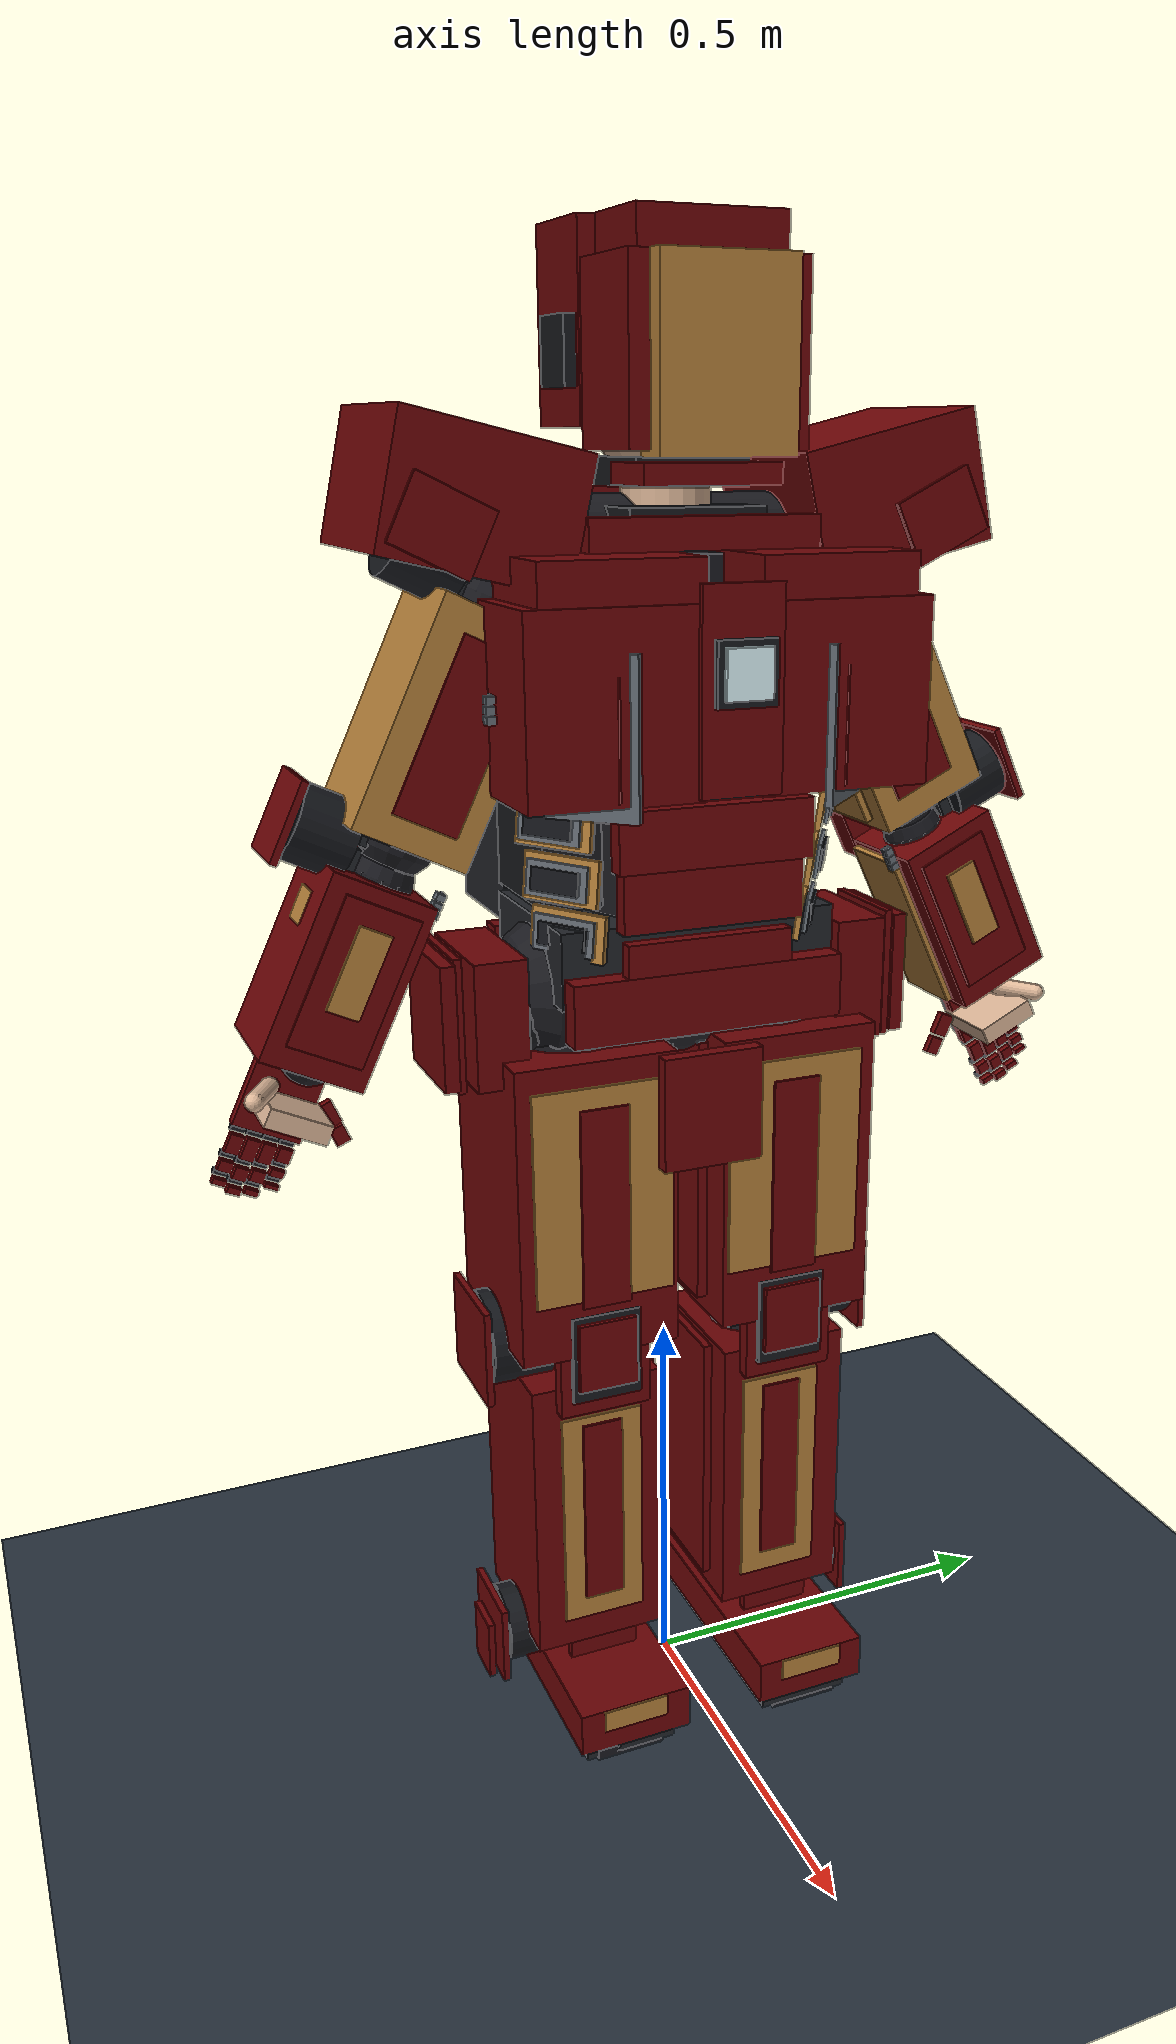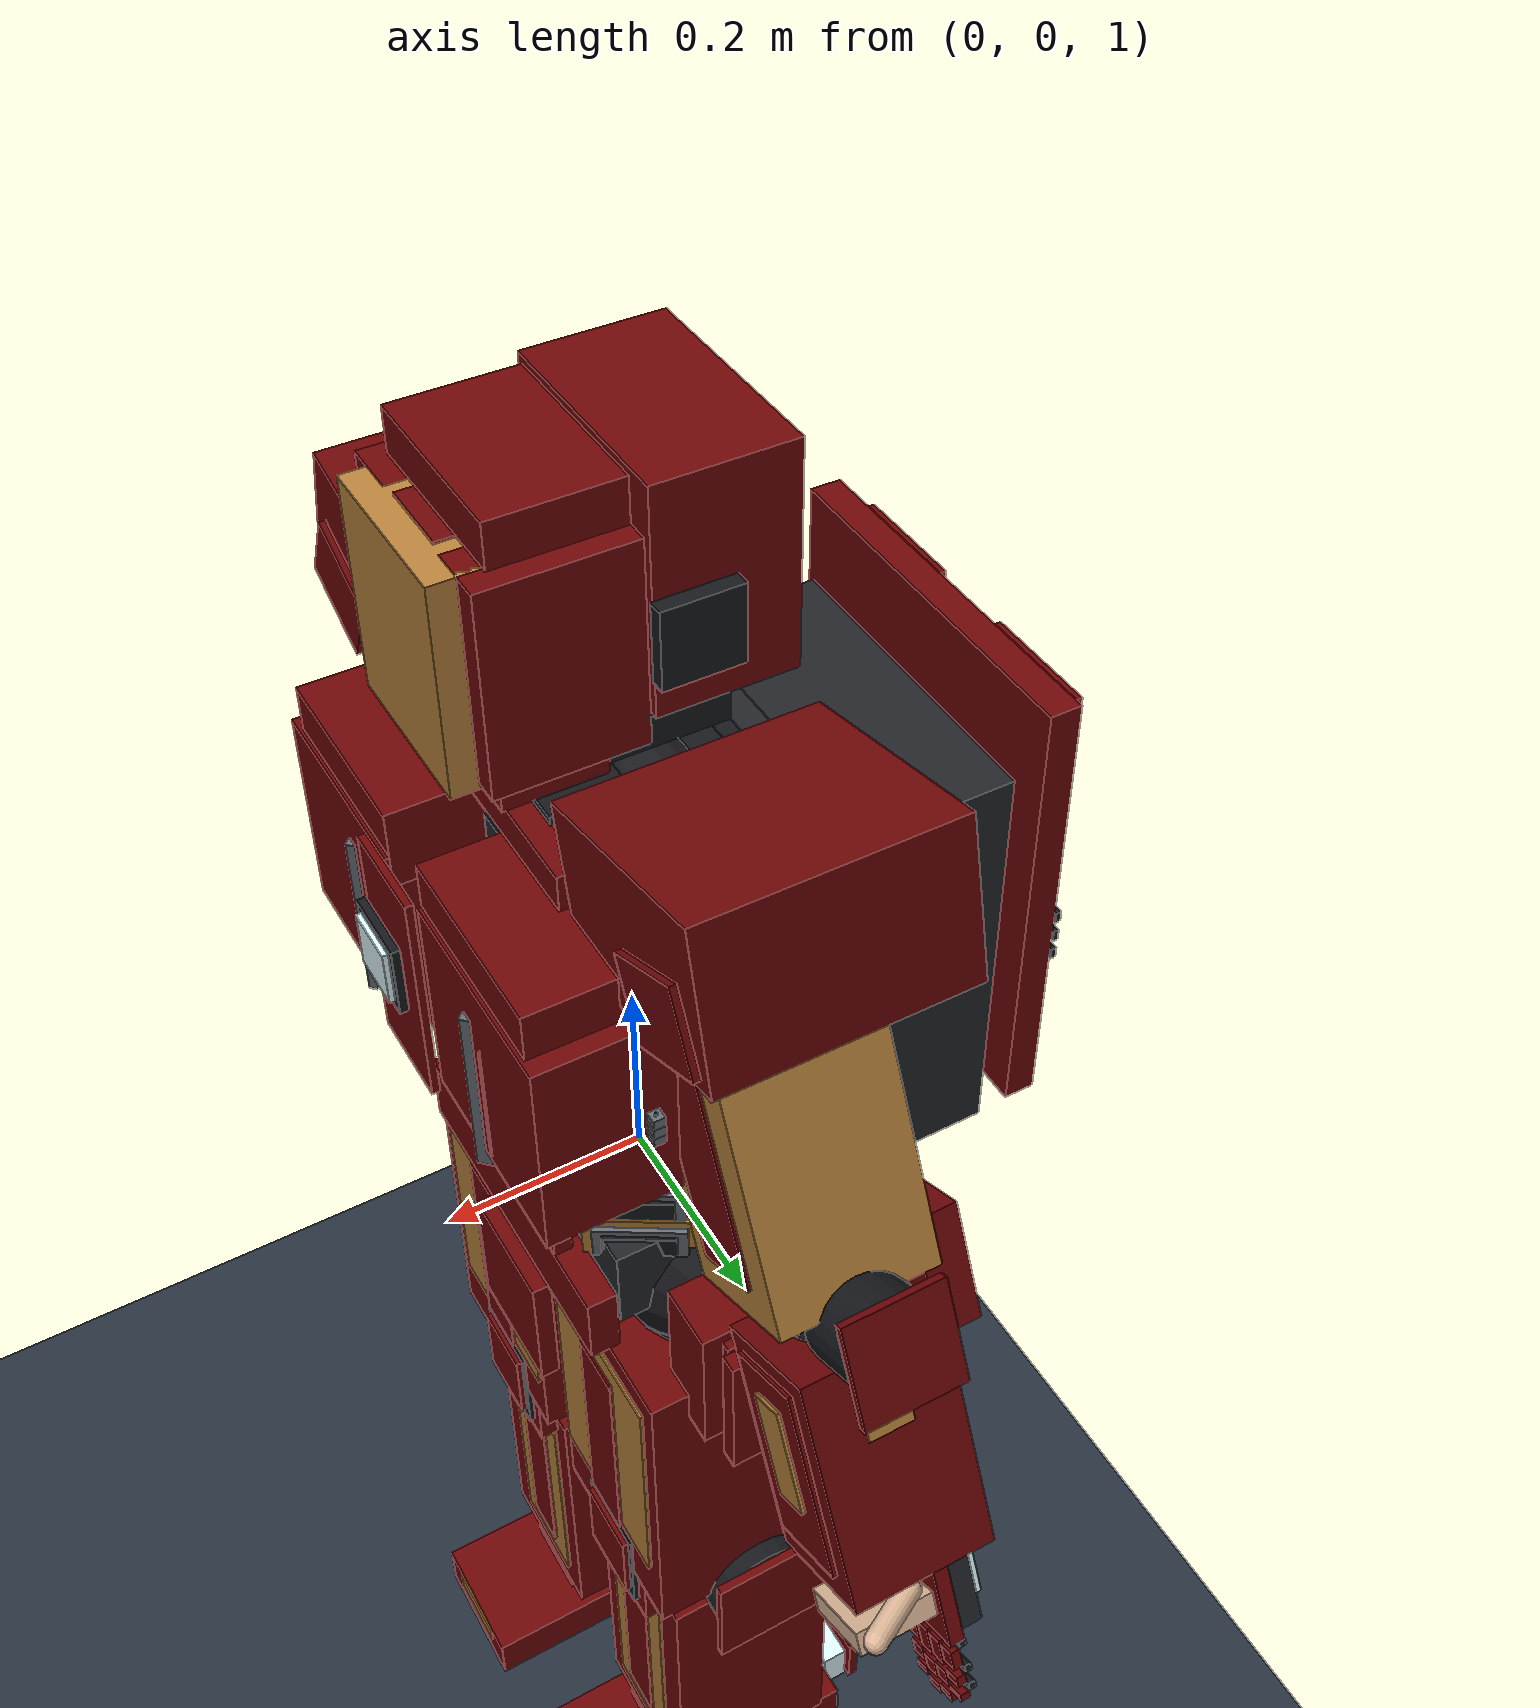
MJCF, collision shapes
<mujoco model="iron_man_mark_43">
  <compiler angle="radian" meshdir="meshes" />

  <asset>
    <mesh name="pelvis_frame" content_type="model/stl" file="pelvis_frame.stl" />
    <mesh name="left_thigh_cuff" content_type="model/stl" file="left_thigh_cuff.stl" />
    <mesh name="left_shank_cuff" content_type="model/stl" file="left_shank_cuff.stl" />
    <mesh name="right_thigh_cuff" content_type="model/stl" file="right_thigh_cuff.stl" />
    <mesh name="right_shank_cuff" content_type="model/stl" file="right_shank_cuff.stl" />
    <mesh name="left_upper_arm_cuff" content_type="model/stl" file="left_upper_arm_cuff.stl" />
    <mesh name="left_forearm_cuff" content_type="model/stl" file="left_forearm_cuff.stl" />
    <mesh name="right_upper_arm_cuff" content_type="model/stl" file="right_upper_arm_cuff.stl" />
    <mesh name="right_forearm_cuff" content_type="model/stl" file="right_forearm_cuff.stl" />
    <mesh name="helmet_cranium" content_type="model/stl" file="helmet_cranium.stl" />
    <mesh name="helmet_neck_collar" content_type="model/stl" file="helmet_neck_collar.stl" />
    <mesh name="helmet_left_ear_pod" content_type="model/stl" file="helmet_left_ear_pod.stl" />
    <mesh name="helmet_right_ear_pod" content_type="model/stl" file="helmet_right_ear_pod.stl" />
    <mesh name="helmet_crown_panel" content_type="model/stl" file="helmet_crown_panel.stl" />
    <mesh name="helmet_faceplate" content_type="model/stl" file="helmet_faceplate.stl" />
    <mesh name="helmet_forehead_plate" content_type="model/stl" file="helmet_forehead_plate.stl" />
    <mesh name="helmet_mouth_line" content_type="model/stl" file="helmet_mouth_line.stl" />
    <mesh name="helmet_left_eye_socket" content_type="model/stl" file="helmet_left_eye_socket.stl" />
    <mesh name="helmet_left_eye_lens" content_type="model/stl" file="helmet_left_eye_lens.stl" />
    <mesh name="helmet_left_cheek_panel" content_type="model/stl" file="helmet_left_cheek_panel.stl" />
    <mesh name="helmet_right_eye_socket" content_type="model/stl" file="helmet_right_eye_socket.stl" />
    <mesh name="helmet_right_eye_lens" content_type="model/stl" file="helmet_right_eye_lens.stl" />
    <mesh name="helmet_right_cheek_panel" content_type="model/stl" file="helmet_right_cheek_panel.stl" />
    <mesh name="helmet_chin_guard" content_type="model/stl" file="helmet_chin_guard.stl" />
    <mesh name="neck_ring" content_type="model/stl" file="neck_ring.stl" />
    <mesh name="collar_plate" content_type="model/stl" file="collar_plate.stl" />
    <mesh name="left_chest_door" content_type="model/stl" file="left_chest_door.stl" />
    <mesh name="left_pectoral_trim" content_type="model/stl" file="left_pectoral_trim.stl" />
    <mesh name="right_chest_door" content_type="model/stl" file="right_chest_door.stl" />
    <mesh name="right_pectoral_trim" content_type="model/stl" file="right_pectoral_trim.stl" />
    <mesh name="chest_centre" content_type="model/stl" file="chest_centre.stl" />
    <mesh name="arc_reactor_housing" content_type="model/stl" file="arc_reactor_housing.stl" />
    <mesh name="arc_reactor" content_type="model/stl" file="arc_reactor.stl" />
    <mesh name="ab_plate_1" content_type="model/stl" file="ab_plate_1.stl" />
    <mesh name="ab_plate_2" content_type="model/stl" file="ab_plate_2.stl" />
    <mesh name="ab_plate_3" content_type="model/stl" file="ab_plate_3.stl" />
    <mesh name="left_lat_plate" content_type="model/stl" file="left_lat_plate.stl" />
    <mesh name="right_lat_plate" content_type="model/stl" file="right_lat_plate.stl" />
    <mesh name="back_shell" content_type="model/stl" file="back_shell.stl" />
    <mesh name="left_flight_flap" content_type="model/stl" file="left_flight_flap.stl" />
    <mesh name="left_back_vent" content_type="model/stl" file="left_back_vent.stl" />
    <mesh name="right_flight_flap" content_type="model/stl" file="right_flight_flap.stl" />
    <mesh name="right_back_vent" content_type="model/stl" file="right_back_vent.stl" />
    <mesh name="belt_plate" content_type="model/stl" file="belt_plate.stl" />
    <mesh name="rear_belt_plate" content_type="model/stl" file="rear_belt_plate.stl" />
    <mesh name="codpiece" content_type="model/stl" file="codpiece.stl" />
    <mesh name="left_rib_0" content_type="model/stl" file="left_rib_0.stl" />
    <mesh name="left_rib_1" content_type="model/stl" file="left_rib_1.stl" />
    <mesh name="left_rib_2" content_type="model/stl" file="left_rib_2.stl" />
    <mesh name="left_chest_inlay" content_type="model/stl" file="left_chest_inlay.stl" />
    <mesh name="left_chest_inlay_centre" content_type="model/stl" file="left_chest_inlay_centre.stl" />
    <mesh name="right_rib_0" content_type="model/stl" file="right_rib_0.stl" />
    <mesh name="right_rib_1" content_type="model/stl" file="right_rib_1.stl" />
    <mesh name="right_rib_2" content_type="model/stl" file="right_rib_2.stl" />
    <mesh name="right_chest_inlay" content_type="model/stl" file="right_chest_inlay.stl" />
    <mesh name="right_chest_inlay_centre" content_type="model/stl" file="right_chest_inlay_centre.stl" />
    <mesh name="left_pauldron" content_type="model/stl" file="left_pauldron.stl" />
    <mesh name="left_pauldron_edge" content_type="model/stl" file="left_pauldron_edge.stl" />
    <mesh name="left_bicep_sleeve" content_type="model/stl" file="left_bicep_sleeve.stl" />
    <mesh name="left_bicep_clamshell" content_type="model/stl" file="left_bicep_clamshell.stl" />
    <mesh name="left_elbow_cap" content_type="model/stl" file="left_elbow_cap.stl" />
    <mesh name="left_gauntlet_sleeve" content_type="model/stl" file="left_gauntlet_sleeve.stl" />
    <mesh name="left_gauntlet_clamshell" content_type="model/stl" file="left_gauntlet_clamshell.stl" />
    <mesh name="left_gauntlet_stripe" content_type="model/stl" file="left_gauntlet_stripe.stl" />
    <mesh name="left_gauntlet_hatch" content_type="model/stl" file="left_gauntlet_hatch.stl" />
    <mesh name="left_hand_plate" content_type="model/stl" file="left_hand_plate.stl" />
    <mesh name="left_palm_repulsor" content_type="model/stl" file="left_palm_repulsor.stl" />
    <mesh name="left_finger_1" content_type="model/stl" file="left_finger_1.stl" />
    <mesh name="left_finger_1_knuckle" content_type="model/stl" file="left_finger_1_knuckle.stl" />
    <mesh name="left_finger_1_middle" content_type="model/stl" file="left_finger_1_middle.stl" />
    <mesh name="left_finger_1_middle_knuckle" content_type="model/stl" file="left_finger_1_middle_knuckle.stl" />
    <mesh name="left_finger_1_distal" content_type="model/stl" file="left_finger_1_distal.stl" />
    <mesh name="left_finger_1_distal_knuckle" content_type="model/stl" file="left_finger_1_distal_knuckle.stl" />
    <mesh name="left_finger_2" content_type="model/stl" file="left_finger_2.stl" />
    <mesh name="left_finger_2_knuckle" content_type="model/stl" file="left_finger_2_knuckle.stl" />
    <mesh name="left_finger_2_middle" content_type="model/stl" file="left_finger_2_middle.stl" />
    <mesh name="left_finger_2_middle_knuckle" content_type="model/stl" file="left_finger_2_middle_knuckle.stl" />
    <mesh name="left_finger_2_distal" content_type="model/stl" file="left_finger_2_distal.stl" />
    <mesh name="left_finger_2_distal_knuckle" content_type="model/stl" file="left_finger_2_distal_knuckle.stl" />
    <mesh name="left_finger_3" content_type="model/stl" file="left_finger_3.stl" />
    <mesh name="left_finger_3_knuckle" content_type="model/stl" file="left_finger_3_knuckle.stl" />
    <mesh name="left_finger_3_middle" content_type="model/stl" file="left_finger_3_middle.stl" />
    <mesh name="left_finger_3_middle_knuckle" content_type="model/stl" file="left_finger_3_middle_knuckle.stl" />
    <mesh name="left_finger_3_distal" content_type="model/stl" file="left_finger_3_distal.stl" />
    <mesh name="left_finger_3_distal_knuckle" content_type="model/stl" file="left_finger_3_distal_knuckle.stl" />
    <mesh name="left_finger_4" content_type="model/stl" file="left_finger_4.stl" />
    <mesh name="left_finger_4_knuckle" content_type="model/stl" file="left_finger_4_knuckle.stl" />
    <mesh name="left_finger_4_middle" content_type="model/stl" file="left_finger_4_middle.stl" />
    <mesh name="left_finger_4_middle_knuckle" content_type="model/stl" file="left_finger_4_middle_knuckle.stl" />
    <mesh name="left_finger_4_distal" content_type="model/stl" file="left_finger_4_distal.stl" />
    <mesh name="left_finger_4_distal_knuckle" content_type="model/stl" file="left_finger_4_distal_knuckle.stl" />
    <mesh name="left_thumb" content_type="model/stl" file="left_thumb.stl" />
    <mesh name="left_thumb_distal" content_type="model/stl" file="left_thumb_distal.stl" />
    <mesh name="right_pauldron" content_type="model/stl" file="right_pauldron.stl" />
    <mesh name="right_pauldron_edge" content_type="model/stl" file="right_pauldron_edge.stl" />
    <mesh name="right_bicep_sleeve" content_type="model/stl" file="right_bicep_sleeve.stl" />
    <mesh name="right_bicep_clamshell" content_type="model/stl" file="right_bicep_clamshell.stl" />
    <mesh name="right_elbow_cap" content_type="model/stl" file="right_elbow_cap.stl" />
    <mesh name="right_gauntlet_sleeve" content_type="model/stl" file="right_gauntlet_sleeve.stl" />
    <mesh name="right_gauntlet_clamshell" content_type="model/stl" file="right_gauntlet_clamshell.stl" />
    <mesh name="right_gauntlet_stripe" content_type="model/stl" file="right_gauntlet_stripe.stl" />
    <mesh name="right_gauntlet_hatch" content_type="model/stl" file="right_gauntlet_hatch.stl" />
    <mesh name="right_hand_plate" content_type="model/stl" file="right_hand_plate.stl" />
    <mesh name="right_palm_repulsor" content_type="model/stl" file="right_palm_repulsor.stl" />
    <mesh name="right_finger_1" content_type="model/stl" file="right_finger_1.stl" />
    <mesh name="right_finger_1_knuckle" content_type="model/stl" file="right_finger_1_knuckle.stl" />
    <mesh name="right_finger_1_middle" content_type="model/stl" file="right_finger_1_middle.stl" />
    <mesh name="right_finger_1_middle_knuckle" content_type="model/stl" file="right_finger_1_middle_knuckle.stl" />
    <mesh name="right_finger_1_distal" content_type="model/stl" file="right_finger_1_distal.stl" />
    <mesh name="right_finger_1_distal_knuckle" content_type="model/stl" file="right_finger_1_distal_knuckle.stl" />
    <mesh name="right_finger_2" content_type="model/stl" file="right_finger_2.stl" />
    <mesh name="right_finger_2_knuckle" content_type="model/stl" file="right_finger_2_knuckle.stl" />
    <mesh name="right_finger_2_middle" content_type="model/stl" file="right_finger_2_middle.stl" />
    <mesh name="right_finger_2_middle_knuckle" content_type="model/stl" file="right_finger_2_middle_knuckle.stl" />
    <mesh name="right_finger_2_distal" content_type="model/stl" file="right_finger_2_distal.stl" />
    <mesh name="right_finger_2_distal_knuckle" content_type="model/stl" file="right_finger_2_distal_knuckle.stl" />
    <mesh name="right_finger_3" content_type="model/stl" file="right_finger_3.stl" />
    <mesh name="right_finger_3_knuckle" content_type="model/stl" file="right_finger_3_knuckle.stl" />
    <mesh name="right_finger_3_middle" content_type="model/stl" file="right_finger_3_middle.stl" />
    <mesh name="right_finger_3_middle_knuckle" content_type="model/stl" file="right_finger_3_middle_knuckle.stl" />
    <mesh name="right_finger_3_distal" content_type="model/stl" file="right_finger_3_distal.stl" />
    <mesh name="right_finger_3_distal_knuckle" content_type="model/stl" file="right_finger_3_distal_knuckle.stl" />
    <mesh name="right_finger_4" content_type="model/stl" file="right_finger_4.stl" />
    <mesh name="right_finger_4_knuckle" content_type="model/stl" file="right_finger_4_knuckle.stl" />
    <mesh name="right_finger_4_middle" content_type="model/stl" file="right_finger_4_middle.stl" />
    <mesh name="right_finger_4_middle_knuckle" content_type="model/stl" file="right_finger_4_middle_knuckle.stl" />
    <mesh name="right_finger_4_distal" content_type="model/stl" file="right_finger_4_distal.stl" />
    <mesh name="right_finger_4_distal_knuckle" content_type="model/stl" file="right_finger_4_distal_knuckle.stl" />
    <mesh name="right_thumb" content_type="model/stl" file="right_thumb.stl" />
    <mesh name="right_thumb_distal" content_type="model/stl" file="right_thumb_distal.stl" />
    <mesh name="left_hip_flap" content_type="model/stl" file="left_hip_flap.stl" />
    <mesh name="left_thigh_shell" content_type="model/stl" file="left_thigh_shell.stl" />
    <mesh name="left_thigh_clamshell" content_type="model/stl" file="left_thigh_clamshell.stl" />
    <mesh name="left_knee_cap" content_type="model/stl" file="left_knee_cap.stl" />
    <mesh name="left_shin_shell" content_type="model/stl" file="left_shin_shell.stl" />
    <mesh name="left_calf_clamshell" content_type="model/stl" file="left_calf_clamshell.stl" />
    <mesh name="left_shin_stripe" content_type="model/stl" file="left_shin_stripe.stl" />
    <mesh name="left_thigh_stripe" content_type="model/stl" file="left_thigh_stripe.stl" />
    <mesh name="left_shin_guard" content_type="model/stl" file="left_shin_guard.stl" />
    <mesh name="left_boot_toe" content_type="model/stl" file="left_boot_toe.stl" />
    <mesh name="left_boot_trim" content_type="model/stl" file="left_boot_trim.stl" />
    <mesh name="left_heel_thruster" content_type="model/stl" file="left_heel_thruster.stl" />
    <mesh name="left_thruster_cover" content_type="model/stl" file="left_thruster_cover.stl" />
    <mesh name="left_ankle_flap" content_type="model/stl" file="left_ankle_flap.stl" />
    <mesh name="right_hip_flap" content_type="model/stl" file="right_hip_flap.stl" />
    <mesh name="right_thigh_shell" content_type="model/stl" file="right_thigh_shell.stl" />
    <mesh name="right_thigh_clamshell" content_type="model/stl" file="right_thigh_clamshell.stl" />
    <mesh name="right_knee_cap" content_type="model/stl" file="right_knee_cap.stl" />
    <mesh name="right_shin_shell" content_type="model/stl" file="right_shin_shell.stl" />
    <mesh name="right_calf_clamshell" content_type="model/stl" file="right_calf_clamshell.stl" />
    <mesh name="right_shin_stripe" content_type="model/stl" file="right_shin_stripe.stl" />
    <mesh name="right_thigh_stripe" content_type="model/stl" file="right_thigh_stripe.stl" />
    <mesh name="right_shin_guard" content_type="model/stl" file="right_shin_guard.stl" />
    <mesh name="right_boot_toe" content_type="model/stl" file="right_boot_toe.stl" />
    <mesh name="right_boot_trim" content_type="model/stl" file="right_boot_trim.stl" />
    <mesh name="right_heel_thruster" content_type="model/stl" file="right_heel_thruster.stl" />
    <mesh name="right_thruster_cover" content_type="model/stl" file="right_thruster_cover.stl" />
    <mesh name="right_ankle_flap" content_type="model/stl" file="right_ankle_flap.stl" />
    <mesh name="left_clavicle_cover" content_type="model/stl" file="left_clavicle_cover.stl" />
    <mesh name="left_back_scapula" content_type="model/stl" file="left_back_scapula.stl" />
    <mesh name="left_back_grille_0" content_type="model/stl" file="left_back_grille_0.stl" />
    <mesh name="left_back_grille_1" content_type="model/stl" file="left_back_grille_1.stl" />
    <mesh name="left_back_grille_2" content_type="model/stl" file="left_back_grille_2.stl" />
    <mesh name="left_hip_cowl" content_type="model/stl" file="left_hip_cowl.stl" />
    <mesh name="left_hip_outer_plate" content_type="model/stl" file="left_hip_outer_plate.stl" />
    <mesh name="left_thigh_ridge" content_type="model/stl" file="left_thigh_ridge.stl" />
    <mesh name="left_thigh_edge" content_type="model/stl" file="left_thigh_edge.stl" />
    <mesh name="left_shin_ridge" content_type="model/stl" file="left_shin_ridge.stl" />
    <mesh name="left_shin_edge" content_type="model/stl" file="left_shin_edge.stl" />
    <mesh name="left_knee_bezel" content_type="model/stl" file="left_knee_bezel.stl" />
    <mesh name="left_knee_face" content_type="model/stl" file="left_knee_face.stl" />
    <mesh name="left_knee_motor_cover" content_type="model/stl" file="left_knee_motor_cover.stl" />
    <mesh name="left_ankle_motor_cover" content_type="model/stl" file="left_ankle_motor_cover.stl" />
    <mesh name="left_elbow_motor_cover" content_type="model/stl" file="left_elbow_motor_cover.stl" />
    <mesh name="left_bicep_front" content_type="model/stl" file="left_bicep_front.stl" />
    <mesh name="left_forearm_crest" content_type="model/stl" file="left_forearm_crest.stl" />
    <mesh name="right_clavicle_cover" content_type="model/stl" file="right_clavicle_cover.stl" />
    <mesh name="right_back_scapula" content_type="model/stl" file="right_back_scapula.stl" />
    <mesh name="right_back_grille_0" content_type="model/stl" file="right_back_grille_0.stl" />
    <mesh name="right_back_grille_1" content_type="model/stl" file="right_back_grille_1.stl" />
    <mesh name="right_back_grille_2" content_type="model/stl" file="right_back_grille_2.stl" />
    <mesh name="right_hip_cowl" content_type="model/stl" file="right_hip_cowl.stl" />
    <mesh name="right_hip_outer_plate" content_type="model/stl" file="right_hip_outer_plate.stl" />
    <mesh name="right_thigh_ridge" content_type="model/stl" file="right_thigh_ridge.stl" />
    <mesh name="right_thigh_edge" content_type="model/stl" file="right_thigh_edge.stl" />
    <mesh name="right_shin_ridge" content_type="model/stl" file="right_shin_ridge.stl" />
    <mesh name="right_shin_edge" content_type="model/stl" file="right_shin_edge.stl" />
    <mesh name="right_knee_bezel" content_type="model/stl" file="right_knee_bezel.stl" />
    <mesh name="right_knee_face" content_type="model/stl" file="right_knee_face.stl" />
    <mesh name="right_knee_motor_cover" content_type="model/stl" file="right_knee_motor_cover.stl" />
    <mesh name="right_ankle_motor_cover" content_type="model/stl" file="right_ankle_motor_cover.stl" />
    <mesh name="right_elbow_motor_cover" content_type="model/stl" file="right_elbow_motor_cover.stl" />
    <mesh name="right_bicep_front" content_type="model/stl" file="right_bicep_front.stl" />
    <mesh name="right_forearm_crest" content_type="model/stl" file="right_forearm_crest.stl" />
    <mesh name="left_rib_edge_0" content_type="model/stl" file="left_rib_edge_0.stl" />
    <mesh name="left_rib_insert_0" content_type="model/stl" file="left_rib_insert_0.stl" />
    <mesh name="left_rib_edge_1" content_type="model/stl" file="left_rib_edge_1.stl" />
    <mesh name="left_rib_insert_1" content_type="model/stl" file="left_rib_insert_1.stl" />
    <mesh name="left_rib_edge_2" content_type="model/stl" file="left_rib_edge_2.stl" />
    <mesh name="left_rib_insert_2" content_type="model/stl" file="left_rib_insert_2.stl" />
    <mesh name="left_collar_inlay" content_type="model/stl" file="left_collar_inlay.stl" />
    <mesh name="right_rib_edge_0" content_type="model/stl" file="right_rib_edge_0.stl" />
    <mesh name="right_rib_insert_0" content_type="model/stl" file="right_rib_insert_0.stl" />
    <mesh name="right_rib_edge_1" content_type="model/stl" file="right_rib_edge_1.stl" />
    <mesh name="right_rib_insert_1" content_type="model/stl" file="right_rib_insert_1.stl" />
    <mesh name="right_rib_edge_2" content_type="model/stl" file="right_rib_edge_2.stl" />
    <mesh name="right_rib_insert_2" content_type="model/stl" file="right_rib_insert_2.stl" />
    <mesh name="right_collar_inlay" content_type="model/stl" file="right_collar_inlay.stl" />
    <mesh name="left_chest_door_hinge_knuckle" content_type="model/stl" file="left_chest_door_hinge_knuckle.stl" />
    <mesh name="right_chest_door_hinge_knuckle" content_type="model/stl" file="right_chest_door_hinge_knuckle.stl" />
    <mesh name="left_lat_plate_hinge_knuckle" content_type="model/stl" file="left_lat_plate_hinge_knuckle.stl" />
    <mesh name="right_lat_plate_hinge_knuckle" content_type="model/stl" file="right_lat_plate_hinge_knuckle.stl" />
    <mesh name="left_gauntlet_clamshell_hinge_knuckle" content_type="model/stl" file="left_gauntlet_clamshell_hinge_knuckle.stl" />
    <mesh name="right_gauntlet_clamshell_hinge_knuckle" content_type="model/stl" file="right_gauntlet_clamshell_hinge_knuckle.stl" />
    <mesh name="left_thigh_clamshell_hinge_knuckle" content_type="model/stl" file="left_thigh_clamshell_hinge_knuckle.stl" />
    <mesh name="right_thigh_clamshell_hinge_knuckle" content_type="model/stl" file="right_thigh_clamshell_hinge_knuckle.stl" />
  </asset>

  <worldbody>
    <light pos="1.5 -2 3" dir="-0.4 0.5 -0.8" diffuse="0.9 0.9 0.9" castshadow="true" /><geom name="floor" type="plane" size="20 20 0.1" material="grid" contype="1" conaffinity="1" /><body name="pelvis_frame" pos="0.0000 0.0000 0.0050">
      <freejoint name="root" /><geom pos="0 0 1.02925" quat="1 0 0 0" type="mesh" contype="0" conaffinity="0" group="1" rgba="0.13 0.14 0.16 1" density="0" mesh="pelvis_frame" />
      <geom size="0.11 0.17 0.045" pos="0 0 1.02925" type="box" rgba="0.13 0.14 0.16 1" contype="1" conaffinity="0" group="3" />
      <body name="spine_frame" pos="0 0 0.96425">
        <joint name="trunk_flex" range="-0.35 0.5" actuatorfrcrange="-120 120" damping="0.1" axis="0 1 0" />
        <geom size="0.025 0.04 0.252" pos="-0.11 0 0.252" type="box" contype="0" conaffinity="0" group="1" rgba="0.13 0.14 0.16 1" density="0" />
        <geom size="0.025 0.04 0.252" pos="-0.11 0 0.252" type="box" rgba="0.13 0.14 0.16 1" contype="1" conaffinity="0" group="3" />
        <body name="backpack">
          <geom size="0.08 0.16 0.21" pos="-0.2 0 0.2772" type="box" contype="0" conaffinity="0" group="1" rgba="0.13 0.14 0.16 1" density="0" />
          <geom size="0.08 0.16 0.21" pos="-0.2 0 0.2772" type="box" rgba="0.13 0.14 0.16 1" contype="1" conaffinity="0" group="3" />
        <inertial pos="-0.2 0 0.2772" mass="9" fullinertia="0.2091 0.1515 0.096 0 0 0" /></body>
        <body name="chest_plate">
          <geom size="0.01 0.08 0.12" pos="0.1 0 0.35772" type="box" contype="0" conaffinity="0" group="1" rgba="0.13 0.14 0.16 1" density="0" />
          <geom size="0.01 0.08 0.12" pos="0.1 0 0.35772" type="box" rgba="0.13 0.14 0.16 1" contype="1" conaffinity="0" group="3" />
        <inertial pos="0.1 0 0.35772" mass="1.6" fullinertia="0.011093 0.007733 0.003467 0 0 0" /></body>
        <body name="shoulder_yoke" pos="0 0 0.504">
          <geom size="0.03 0.265 0.03" pos="-0.06 0 0" type="box" contype="0" conaffinity="0" group="1" rgba="0.085 0.092 0.11 1" density="0" />
          <geom size="0.03 0.265 0.03" pos="-0.06 0 0" type="box" rgba="0.085 0.092 0.11 1" contype="1" conaffinity="0" group="3" />
          <body name="left_shoulder_module" pos="0 0.235 0" quat="0.974794 0.223106 0 0">
            <joint name="left_shoulder_abduction" range="-0.75 2.15" actuatorfrcrange="-60 60" damping="0.1" axis="1 0 0" />
            <geom size="0.055 0.04" pos="0 0.04 0" quat="0.707107 0.707107 0 0" type="cylinder" contype="0" conaffinity="0" group="1" rgba="0.085 0.092 0.11 1" density="0" />
            <geom size="0.055 0.04" pos="0 0.04 0" quat="0.707107 0.707107 0 0" type="cylinder" rgba="0.085 0.092 0.11 1" contype="1" conaffinity="0" group="3" />
            <body name="left_upper_arm_strut">
              <joint name="left_shoulder_flexion" range="-1 3" actuatorfrcrange="-60 60" damping="0.1" axis="0 1 0" />
              <geom size="0.02 0.0175 0.16075" pos="0 0 -0.16275" type="box" contype="0" conaffinity="0" group="1" rgba="0.13 0.14 0.16 1" density="0" />
              <geom size="0.02 0.0175 0.16075" pos="0 0 -0.16275" type="box" rgba="0.13 0.14 0.16 1" contype="1" conaffinity="0" group="3" />
              <body name="left_upper_arm_cuff" pos="0 -0.05 -0.179025">
                <geom type="mesh" contype="0" conaffinity="0" group="1" rgba="0.2 0.2 0.22 1" density="0" mesh="left_upper_arm_cuff" />
                <geom size="0.06 0.06 0.03" type="box" rgba="0.2 0.2 0.22 1" contype="1" conaffinity="0" group="3" />
              <inertial pos="8.67146e-18 7.97987e-18 2.91805e-18" mass="0.3" fullinertia="0.000577306 0.000577306 0.000974613 -1.8337e-20 1.01336e-20 2.62992e-20" /></body>
              <body name="left_elbow_module" pos="0 0 -0.3255">
                <geom size="0.045 0.035" pos="0 0.035 0" quat="0.707107 0.707107 0 0" type="cylinder" contype="0" conaffinity="0" group="1" rgba="0.085 0.092 0.11 1" density="0" />
                <geom size="0.045 0.035" pos="0 0.035 0" quat="0.707107 0.707107 0 0" type="cylinder" rgba="0.085 0.092 0.11 1" contype="1" conaffinity="0" group="3" />
                <body name="left_forearm_strut">
                  <joint name="left_elbow_flexion" range="-2.4 0.05" actuatorfrcrange="-40 40" damping="0.1" axis="0 1 0" />
                  <geom size="0.0175 0.015 0.12575" pos="0 0 -0.12775" type="box" contype="0" conaffinity="0" group="1" rgba="0.13 0.14 0.16 1" density="0" />
                  <geom size="0.0175 0.015 0.12575" pos="0 0 -0.12775" type="box" rgba="0.13 0.14 0.16 1" contype="1" conaffinity="0" group="3" />
                  <body name="left_forearm_cuff" pos="0 -0.045 -0.140525">
                    <geom type="mesh" contype="0" conaffinity="0" group="1" rgba="0.2 0.2 0.22 1" density="0" mesh="left_forearm_cuff" />
                    <geom size="0.05 0.05 0.03" type="box" rgba="0.2 0.2 0.22 1" contype="1" conaffinity="0" group="3" />
                  <inertial pos="-1.50277e-17 -5.33108e-18 -1.89243e-18" mass="0.25" fullinertia="0.000351459 0.000351459 0.000552919 -4.96221e-20 8.53452e-21 1.47068e-20" /></body>
                  <body name="left_hand" pos="0 0 -0.2555" quat="0.707107 0 0.707107 0">
                    <joint name="left_wrist_flexion" range="-0.8 0.8" actuatorfrcrange="-15 15" damping="0.1" axis="1 0 0" />
                    <geom size="0.045 0.035 0.015" pos="0.045 -0.045 -0.04" type="box" contype="0" conaffinity="0" group="1" rgba="0.13 0.14 0.16 1" density="0" />
                    <geom size="0.045 0.035 0.015" pos="0.045 -0.045 -0.04" type="box" rgba="0.13 0.14 0.16 1" contype="1" conaffinity="0" group="3" />
                    <body name="left_hand_plate" pos="0.05 -0.045 -0.017" quat="0.707107 0 -0.707107 0">
                      <geom type="mesh" contype="0" conaffinity="0" group="1" rgba="0.43 0.018 0.026 1" density="0" mesh="left_hand_plate" />
                      <geom size="0.007151 0.0419495 0.044915" pos="-0.007151 0 0" type="box" rgba="0.43 0.018 0.026 1" contype="1" conaffinity="0" group="3" />
                    <inertial pos="-0.005836 -1.88772e-19 4.55935e-19" mass="0.18" fullinertia="0.000209176 0.000111784 0.00010117 -4.79045e-22 1.13056e-22 -6.29665e-08" /></body>
                    <body name="left_palm_repulsor" pos="0.045 -0.045 -0.056" quat="-1.73205e-07 1 0 0">
                      <geom type="mesh" contype="0" conaffinity="0" group="1" rgba="0.88 0.98 1 1" density="0" mesh="left_palm_repulsor" />
                      <geom size="0.026 0.026 0.004" pos="0 0 0.004" type="box" rgba="0.88 0.98 1 1" contype="1" conaffinity="0" group="3" />
                    <inertial pos="-2.38987e-18 -7.78444e-19 0.003936" mass="0.06" fullinertia="1.02147e-05 1.02147e-05 1.98035e-05 -4.88642e-22 9.06033e-25 1.04655e-22" /></body>
                    <body name="left_finger_1" pos="0.1 -0.075 -0.03">
                      <joint name="left_finger_1_hinge" range="0 1.15" actuatorfrcrange="-0.35 0.35" damping="0.1" axis="0 1 0" />
                      <geom pos="0.0165 0 0.004" quat="0.707107 0 0.707107 0" type="mesh" contype="0" conaffinity="0" group="1" rgba="0.43 0.018 0.026 1" density="0" mesh="left_finger_1" />
                      <geom size="0.0045365 0.0084475 0.012" pos="0.0165 0 0.008555" quat="0.707107 0 0.707107 0" type="box" rgba="0.43 0.018 0.026 1" contype="1" conaffinity="0" group="3" />
                      <body name="left_finger_1_knuckle" pos="0 -0.009 0" quat="0.707107 -0.707107 0 0">
                        <geom type="mesh" contype="0" conaffinity="0" group="1" rgba="0.085 0.092 0.11 1" density="0" mesh="left_finger_1_knuckle" />
                        <geom size="0.0035 0.0035 0.009" pos="0 0 0.009" type="box" rgba="0.085 0.092 0.11 1" contype="1" conaffinity="0" group="3" />
                      <inertial pos="-1.60526e-19 -4.31545e-20 0.008936" mass="0.003" fullinertia="1e-07 1e-07 1e-07 -3.3683e-25 -5.62987e-25 -7.95618e-25" /></body>
                      <body name="left_finger_1_middle" pos="0.033 0 0">
                        <joint name="left_finger_1_middle_hinge" range="0 1.55" actuatorfrcrange="-0.35 0.35" damping="0.1" axis="0 1 0" />
                        <geom pos="0.0115 0 0.004" quat="0.707107 0 0.707107 0" type="mesh" contype="0" conaffinity="0" group="1" rgba="0.43 0.018 0.026 1" density="0" mesh="left_finger_1_middle" />
                        <geom size="0.004533 0.0084475 0.007" pos="0.0115 0 0.008554" quat="0.707107 0 0.707107 0" type="box" rgba="0.43 0.018 0.026 1" contype="1" conaffinity="0" group="3" />
                        <body name="left_finger_1_middle_knuckle" pos="0 -0.009 0" quat="0.707107 -0.707107 0 0">
                          <geom type="mesh" contype="0" conaffinity="0" group="1" rgba="0.085 0.092 0.11 1" density="0" mesh="left_finger_1_middle_knuckle" />
                          <geom size="0.0035 0.0035 0.009" pos="0 0 0.009" type="box" rgba="0.085 0.092 0.11 1" contype="1" conaffinity="0" group="3" />
                        <inertial pos="-1.60526e-19 -4.31545e-20 0.008936" mass="0.003" fullinertia="1e-07 1e-07 1e-07 -3.3683e-25 -5.62987e-25 -7.95618e-25" /></body>
                        <body name="left_finger_1_distal" pos="0.023 0 0">
                          <joint name="left_finger_1_distal_hinge" range="0 1.15" actuatorfrcrange="-0.35 0.35" damping="0.1" axis="0 1 0" />
                          <geom pos="0.0085 0 0.004" quat="0.707107 0 0.707107 0" type="mesh" contype="0" conaffinity="0" group="1" rgba="0.43 0.018 0.026 1" density="0" mesh="left_finger_1_distal" />
                          <geom size="0.004527 0.0084475 0.004" pos="0.0085 0 0.008551" quat="0.707107 0 0.707107 0" type="box" rgba="0.43 0.018 0.026 1" contype="1" conaffinity="0" group="3" />
                          <body name="left_finger_1_distal_knuckle" pos="0 -0.009 0" quat="0.707107 -0.707107 0 0">
                            <geom type="mesh" contype="0" conaffinity="0" group="1" rgba="0.085 0.092 0.11 1" density="0" mesh="left_finger_1_distal_knuckle" />
                            <geom size="0.0035 0.0035 0.009" pos="0 0 0.009" type="box" rgba="0.085 0.092 0.11 1" contype="1" conaffinity="0" group="3" />
                          <inertial pos="-1.60526e-19 -4.31545e-20 0.008936" mass="0.003" fullinertia="1e-07 1e-07 1e-07 -3.3683e-25 -5.62987e-25 -7.95618e-25" /></body>
                        <inertial pos="0.00859 0.00000257921 0.008527" mass="0.012" fullinertia="2.45149000006e-07 1.21832e-07 2.26943999994e-07 1.09394000616e-10 -8.66954069891e-12 -1.8839342506e-12" /></body>
                      <inertial pos="0.011669 0.0000026595 0.008527" mass="0.012" fullinertia="2.48241000059e-07 2.36157e-07 3.37911999941e-07 1.88458000555e-10 -8.98592040251e-11 -1.69769841289e-12" /></body>
                    <inertial pos="0.016801 0.00000269533 0.008527" mass="0.012" fullinertia="2.49621000151e-07 5.62734e-07 6.62680999849e-07 3.21950000529e-10 -2.313479859e-10 -1.61987478838e-12" /></body>
                    <body name="left_finger_2" pos="0.1 -0.055 -0.03">
                      <joint name="left_finger_2_hinge" range="0 1.15" actuatorfrcrange="-0.35 0.35" damping="0.1" axis="0 1 0" />
                      <geom pos="0.018 0 0.004" quat="0.707107 0 0.707107 0" type="mesh" contype="0" conaffinity="0" group="1" rgba="0.43 0.018 0.026 1" density="0" mesh="left_finger_2" />
                      <geom size="0.004537 0.0084475 0.0135" pos="0.018 0 0.008555" quat="0.707107 0 0.707107 0" type="box" rgba="0.43 0.018 0.026 1" contype="1" conaffinity="0" group="3" />
                      <body name="left_finger_2_knuckle" pos="0 -0.009 0" quat="0.707107 -0.707107 0 0">
                        <geom type="mesh" contype="0" conaffinity="0" group="1" rgba="0.085 0.092 0.11 1" density="0" mesh="left_finger_2_knuckle" />
                        <geom size="0.0035 0.0035 0.009" pos="0 0 0.009" type="box" rgba="0.085 0.092 0.11 1" contype="1" conaffinity="0" group="3" />
                      <inertial pos="-1.60526e-19 -4.31545e-20 0.008936" mass="0.003" fullinertia="1e-07 1e-07 1e-07 -3.3683e-25 -5.62987e-25 -7.95618e-25" /></body>
                      <body name="left_finger_2_middle" pos="0.036 0 0">
                        <joint name="left_finger_2_middle_hinge" range="0 1.55" actuatorfrcrange="-0.35 0.35" damping="0.1" axis="0 1 0" />
                        <geom pos="0.0125 0 0.004" quat="0.707107 0 0.707107 0" type="mesh" contype="0" conaffinity="0" group="1" rgba="0.43 0.018 0.026 1" density="0" mesh="left_finger_2_middle" />
                        <geom size="0.004534 0.0084475 0.008" pos="0.0125 0 0.008555" quat="0.707107 0 0.707107 0" type="box" rgba="0.43 0.018 0.026 1" contype="1" conaffinity="0" group="3" />
                        <body name="left_finger_2_middle_knuckle" pos="0 -0.009 0" quat="0.707107 -0.707107 0 0">
                          <geom type="mesh" contype="0" conaffinity="0" group="1" rgba="0.085 0.092 0.11 1" density="0" mesh="left_finger_2_middle_knuckle" />
                          <geom size="0.0035 0.0035 0.009" pos="0 0 0.009" type="box" rgba="0.085 0.092 0.11 1" contype="1" conaffinity="0" group="3" />
                        <inertial pos="-1.60526e-19 -4.31545e-20 0.008936" mass="0.003" fullinertia="1e-07 1e-07 1e-07 -3.3683e-25 -5.62987e-25 -7.95618e-25" /></body>
                        <body name="left_finger_2_distal" pos="0.025 0 0">
                          <joint name="left_finger_2_distal_hinge" range="0 1.15" actuatorfrcrange="-0.35 0.35" damping="0.1" axis="0 1 0" />
                          <geom pos="0.009 0 0.004" quat="0.707107 0 0.707107 0" type="mesh" contype="0" conaffinity="0" group="1" rgba="0.43 0.018 0.026 1" density="0" mesh="left_finger_2_distal" />
                          <geom size="0.0045285 0.0084475 0.0045" pos="0.009 0 0.008552" quat="0.707107 0 0.707107 0" type="box" rgba="0.43 0.018 0.026 1" contype="1" conaffinity="0" group="3" />
                          <body name="left_finger_2_distal_knuckle" pos="0 -0.009 0" quat="0.707107 -0.707107 0 0">
                            <geom type="mesh" contype="0" conaffinity="0" group="1" rgba="0.085 0.092 0.11 1" density="0" mesh="left_finger_2_distal_knuckle" />
                            <geom size="0.0035 0.0035 0.009" pos="0 0 0.009" type="box" rgba="0.085 0.092 0.11 1" contype="1" conaffinity="0" group="3" />
                          <inertial pos="-1.60526e-19 -4.31545e-20 0.008936" mass="0.003" fullinertia="1e-07 1e-07 1e-07 -3.3683e-25 -5.62987e-25 -7.95618e-25" /></body>
                        <inertial pos="0.009103 0.000002601 0.008527" mass="0.012" fullinertia="2.45991000014e-07 1.36842e-07 2.41061999986e-07 1.22520000599e-10 -2.1131189228e-11 -1.83223996109e-12" /></body>
                      <inertial pos="0.012696 0.00000267141 0.008527" mass="0.012" fullinertia="2.48694000077e-07 2.87678e-07 3.88889999923e-07 2.15004000546e-10 -1.18267815337e-10 -1.67142973779e-12" /></body>
                    <inertial pos="0.01834 0.00000269948 0.008527" mass="0.012" fullinertia="2.49795000179e-07 6.945e-07 7.94163999821e-07 3.62289000526e-10 -2.73269897011e-10 -1.6109316058e-12" /></body>
                    <body name="left_finger_3" pos="0.1 -0.035 -0.03">
                      <joint name="left_finger_3_hinge" range="0 1.15" actuatorfrcrange="-0.35 0.35" damping="0.1" axis="0 1 0" />
                      <geom pos="0.017 0 0.004" quat="0.707107 0 0.707107 0" type="mesh" contype="0" conaffinity="0" group="1" rgba="0.43 0.018 0.026 1" density="0" mesh="left_finger_3" />
                      <geom size="0.004537 0.0084475 0.0125" pos="0.017 0 0.008555" quat="0.707107 0 0.707107 0" type="box" rgba="0.43 0.018 0.026 1" contype="1" conaffinity="0" group="3" />
                      <body name="left_finger_3_knuckle" pos="0 -0.009 0" quat="0.707107 -0.707107 0 0">
                        <geom type="mesh" contype="0" conaffinity="0" group="1" rgba="0.085 0.092 0.11 1" density="0" mesh="left_finger_3_knuckle" />
                        <geom size="0.0035 0.0035 0.009" pos="0 0 0.009" type="box" rgba="0.085 0.092 0.11 1" contype="1" conaffinity="0" group="3" />
                      <inertial pos="-1.60526e-19 -4.31545e-20 0.008936" mass="0.003" fullinertia="1e-07 1e-07 1e-07 -3.3683e-25 -5.62987e-25 -7.95618e-25" /></body>
                      <body name="left_finger_3_middle" pos="0.034 0 0">
                        <joint name="left_finger_3_middle_hinge" range="0 1.55" actuatorfrcrange="-0.35 0.35" damping="0.1" axis="0 1 0" />
                        <geom pos="0.012 0 0.004" quat="0.707107 0 0.707107 0" type="mesh" contype="0" conaffinity="0" group="1" rgba="0.43 0.018 0.026 1" density="0" mesh="left_finger_3_middle" />
                        <geom size="0.0045335 0.0084475 0.0075" pos="0.012 0 0.008555" quat="0.707107 0 0.707107 0" type="box" rgba="0.43 0.018 0.026 1" contype="1" conaffinity="0" group="3" />
                        <body name="left_finger_3_middle_knuckle" pos="0 -0.009 0" quat="0.707107 -0.707107 0 0">
                          <geom type="mesh" contype="0" conaffinity="0" group="1" rgba="0.085 0.092 0.11 1" density="0" mesh="left_finger_3_middle_knuckle" />
                          <geom size="0.0035 0.0035 0.009" pos="0 0 0.009" type="box" rgba="0.085 0.092 0.11 1" contype="1" conaffinity="0" group="3" />
                        <inertial pos="-1.60526e-19 -4.31545e-20 0.008936" mass="0.003" fullinertia="1e-07 1e-07 1e-07 -3.3683e-25 -5.62987e-25 -7.95618e-25" /></body>
                        <body name="left_finger_3_distal" pos="0.024 0 0">
                          <joint name="left_finger_3_distal_hinge" range="0 1.15" actuatorfrcrange="-0.35 0.35" damping="0.1" axis="0 1 0" />
                          <geom pos="0.0085 0 0.004" quat="0.707107 0 0.707107 0" type="mesh" contype="0" conaffinity="0" group="1" rgba="0.43 0.018 0.026 1" density="0" mesh="left_finger_3_distal" />
                          <geom size="0.004527 0.0084475 0.004" pos="0.0085 0 0.008551" quat="0.707107 0 0.707107 0" type="box" rgba="0.43 0.018 0.026 1" contype="1" conaffinity="0" group="3" />
                          <body name="left_finger_3_distal_knuckle" pos="0 -0.009 0" quat="0.707107 -0.707107 0 0">
                            <geom type="mesh" contype="0" conaffinity="0" group="1" rgba="0.085 0.092 0.11 1" density="0" mesh="left_finger_3_distal_knuckle" />
                            <geom size="0.0035 0.0035 0.009" pos="0 0 0.009" type="box" rgba="0.085 0.092 0.11 1" contype="1" conaffinity="0" group="3" />
                          <inertial pos="-1.60526e-19 -4.31545e-20 0.008936" mass="0.003" fullinertia="1e-07 1e-07 1e-07 -3.3683e-25 -5.62987e-25 -7.95618e-25" /></body>
                        <inertial pos="0.00859 0.00000257921 0.008527" mass="0.012" fullinertia="2.45149000006e-07 1.21832e-07 2.26943999994e-07 1.09394000616e-10 -8.66954069891e-12 -1.8839342506e-12" /></body>
                      <inertial pos="0.012183 0.00000266594 0.008527" mass="0.012" fullinertia="2.48486000068e-07 2.61062e-07 3.62526999932e-07 2.0172000055e-10 -1.04051268017e-10 -1.68344407893e-12" /></body>
                    <inertial pos="0.017314 0.00000269689 0.008527" mass="0.012" fullinertia="2.4968600016e-07 6.04918e-07 7.0476299984e-07 3.35385000528e-10 -2.45349716841e-10 -1.61653039789e-12" /></body>
                    <body name="left_finger_4" pos="0.1 -0.015 -0.03">
                      <joint name="left_finger_4_hinge" range="0 1.15" actuatorfrcrange="-0.35 0.35" damping="0.1" axis="0 1 0" />
                      <geom pos="0.0135 0 0.004" quat="0.707107 0 0.707107 0" type="mesh" contype="0" conaffinity="0" group="1" rgba="0.43 0.018 0.026 1" density="0" mesh="left_finger_4" />
                      <geom size="0.004535 0.0084475 0.009" pos="0.0135 0 0.008555" quat="0.707107 0 0.707107 0" type="box" rgba="0.43 0.018 0.026 1" contype="1" conaffinity="0" group="3" />
                      <body name="left_finger_4_knuckle" pos="0 -0.009 0" quat="0.707107 -0.707107 0 0">
                        <geom type="mesh" contype="0" conaffinity="0" group="1" rgba="0.085 0.092 0.11 1" density="0" mesh="left_finger_4_knuckle" />
                        <geom size="0.0035 0.0035 0.009" pos="0 0 0.009" type="box" rgba="0.085 0.092 0.11 1" contype="1" conaffinity="0" group="3" />
                      <inertial pos="-1.60526e-19 -4.31545e-20 0.008936" mass="0.003" fullinertia="1e-07 1e-07 1e-07 -3.3683e-25 -5.62987e-25 -7.95618e-25" /></body>
                      <body name="left_finger_4_middle" pos="0.027 0 0">
                        <joint name="left_finger_4_middle_hinge" range="0 1.55" actuatorfrcrange="-0.35 0.35" damping="0.1" axis="0 1 0" />
                        <geom pos="0.0095 0 0.004" quat="0.707107 0 0.707107 0" type="mesh" contype="0" conaffinity="0" group="1" rgba="0.43 0.018 0.026 1" density="0" mesh="left_finger_4_middle" />
                        <geom size="0.00453 0.0084475 0.005" pos="0.0095 0 0.008553" quat="0.707107 0 0.707107 0" type="box" rgba="0.43 0.018 0.026 1" contype="1" conaffinity="0" group="3" />
                        <body name="left_finger_4_middle_knuckle" pos="0 -0.009 0" quat="0.707107 -0.707107 0 0">
                          <geom type="mesh" contype="0" conaffinity="0" group="1" rgba="0.085 0.092 0.11 1" density="0" mesh="left_finger_4_middle_knuckle" />
                          <geom size="0.0035 0.0035 0.009" pos="0 0 0.009" type="box" rgba="0.085 0.092 0.11 1" contype="1" conaffinity="0" group="3" />
                        <inertial pos="-1.60526e-19 -4.31545e-20 0.008936" mass="0.003" fullinertia="1e-07 1e-07 1e-07 -3.3683e-25 -5.62987e-25 -7.95618e-25" /></body>
                        <body name="left_finger_4_distal" pos="0.019 0 0">
                          <joint name="left_finger_4_distal_hinge" range="0 1.15" actuatorfrcrange="-0.35 0.35" damping="0.1" axis="0 1 0" />
                          <geom pos="0.0075 0 0.004" quat="0.707107 0 0.707107 0" type="mesh" contype="0" conaffinity="0" group="1" rgba="0.43 0.018 0.026 1" density="0" mesh="left_finger_4_distal" />
                          <geom size="0.0045225 0.0084475 0.003" pos="0.0075 0 0.008547" quat="0.707107 0 0.707107 0" type="box" rgba="0.43 0.018 0.026 1" contype="1" conaffinity="0" group="3" />
                          <body name="left_finger_4_distal_knuckle" pos="0 -0.009 0" quat="0.707107 -0.707107 0 0">
                            <geom type="mesh" contype="0" conaffinity="0" group="1" rgba="0.085 0.092 0.11 1" density="0" mesh="left_finger_4_distal_knuckle" />
                            <geom size="0.0035 0.0035 0.009" pos="0 0 0.009" type="box" rgba="0.085 0.092 0.11 1" contype="1" conaffinity="0" group="3" />
                          <inertial pos="-1.60526e-19 -4.31545e-20 0.008936" mass="0.003" fullinertia="1e-07 1e-07 1e-07 -3.3683e-25 -5.62987e-25 -7.95618e-25" /></body>
                        <inertial pos="0.007565 0.00000251104 0.008527" mass="0.012" fullinertia="2.42564999992e-07 1e-07 2.04012000008e-07 8.30843006691e-11 1.26448989236e-11 -2.04735284847e-12" /></body>
                      <inertial pos="0.009616 0.00000261802 0.008527" mass="0.012" fullinertia="2.46649000022e-07 1.53415e-07 2.56932999978e-07 1.35660000586e-10 -3.42652607587e-11 -1.792305667e-12" /></body>
                    <inertial pos="0.013722 0.00000268011 0.008527" mass="0.012" fullinertia="2.49026000096e-07 3.46067e-07 4.46856999904e-07 2.4163600054e-10 -1.46691650161e-10 -1.65252103459e-12" /></body>
                    <body name="left_thumb" pos="0.04 -0.093 -0.03" quat="0.911039 0 0 -0.412321">
                      <joint name="left_thumb_hinge" range="0 1" actuatorfrcrange="-0.4 0.4" damping="0.1" axis="0 1 0" />
                      <geom pos="0.017 0 0.004" quat="0.707107 0 0.707107 0" type="mesh" contype="0" conaffinity="0" group="1" rgba="0.43 0.018 0.026 1" density="0" mesh="left_thumb" />
                      <geom size="0.0050545 0.0099375 0.015" pos="0.017 0 0.009081" quat="0.707107 0 0.707107 0" type="box" rgba="0.43 0.018 0.026 1" contype="1" conaffinity="0" group="3" />
                      <body name="left_thumb_distal" pos="0.034 0 0">
                        <joint name="left_thumb_distal_hinge" range="0 1.2" actuatorfrcrange="-0.3 0.3" damping="0.1" axis="0 1 0" />
                        <geom pos="0.013 0 0.004" quat="0.707107 0 0.707107 0" type="mesh" contype="0" conaffinity="0" group="1" rgba="0.43 0.018 0.026 1" density="0" mesh="left_thumb_distal" />
                        <geom size="0.0045415 0.008944 0.0115" pos="0.013 0 0.008563" quat="0.707107 0 0.707107 0" type="box" rgba="0.43 0.018 0.026 1" contype="1" conaffinity="0" group="3" />
                      <inertial pos="0.013287 0.00000284566 0.008534" mass="0.012" fullinertia="2.71406000157e-07 5.22466e-07 6.43945999843e-07 3.2673800062e-10 -2.40211744171e-10 -1.89644322369e-12" /></body>
                    <inertial pos="0.017372 0.00000367883 0.009044" mass="0.016" fullinertia="4.50302000362e-07 1.15072e-06 1.35020999964e-06 7.38055001352e-10 -5.54511085342e-10 -4.13562880739e-12" /></body>
                  <inertial pos="0.045 -0.045 -0.04" mass="0.35" fullinertia="0.000169167 0.0002625 0.000379167 0 0 0" /></body>
                  <body name="left_gauntlet_sleeve" pos="0 -0.045 -0.028105">
                    <geom type="mesh" contype="0" conaffinity="0" group="1" rgba="0.43 0.018 0.026 1" density="0" mesh="left_gauntlet_sleeve" />
                    <geom size="0.068172 0.0624125 0.111102" pos="8.38491e-05 0.003848 -0.111153" type="box" rgba="0.43 0.018 0.026 1" contype="1" conaffinity="0" group="3" />
                    <body name="left_gauntlet_stripe">
                      <geom type="mesh" contype="0" conaffinity="0" group="1" rgba="0.72 0.51 0.23 1" density="0" mesh="left_gauntlet_stripe" />
                      <geom size="0.0040375 0.0196165 0.0501235" pos="0.07179 0 -0.094362" type="box" rgba="0.72 0.51 0.23 1" contype="1" conaffinity="0" group="3" />
                    <inertial pos="0.070771 3.10551e-7 -0.093649" mass="0.03" fullinertia="2.64782e-05 2.33112e-05 3.33779e-06 -1.52091e-10 -1.19441e-06 -3.16882e-09" /></body>
                    <body name="left_gauntlet_hatch" pos="0 0.068 -0.035" quat="0.707107 0 0 0.707107">
                      <joint name="left_gauntlet_hatch_hinge" range="-1.2 0" actuatorfrcrange="-1.5 1.5" damping="0.1" axis="0 1 0" />
                      <geom pos="0 0 -0.02" type="mesh" contype="0" conaffinity="0" group="1" rgba="0.72 0.51 0.23 1" density="0" mesh="left_gauntlet_hatch" />
                      <geom size="0.0027125 0.021783 0.02" pos="-0.003362 0 -0.02" type="box" rgba="0.72 0.51 0.23 1" contype="1" conaffinity="0" group="3" />
                    <inertial pos="-0.003158 0.00000798527 -0.01951" mass="0.05" fullinertia="1.07097e-05 5.72547e-06 5.08407e-06 3.30709e-10 3.62309e-08 7.32099e-09" /></body>
                    <body name="left_forearm_crest">
                      <geom type="mesh" contype="0" conaffinity="0" group="1" rgba="0.43 0.018 0.026 1" density="0" mesh="left_forearm_crest" />
                      <geom size="0.0110855 0.0451465 0.088914" pos="0.061223 0 -0.106697" type="box" rgba="0.43 0.018 0.026 1" contype="1" conaffinity="0" group="3" />
                    <inertial pos="0.063803 -0.00000120657 -0.10427" mass="0.06" fullinertia="0.000176043 0.000144615 3.33627e-05 -8.13404e-10 -8.2622e-06 -3.07642e-08" /></body>
                  <inertial pos="0.005525 0.016437 -0.107208" mass="0.4" fullinertia="0.001805 0.002255 0.0013 9.09417e-05 1.22739e-05 -1.47058e-05" /></body>
                  <body name="left_gauntlet_clamshell" pos="0.037318 -0.110057 -0.028105">
                    <joint name="left_gauntlet_clamshell_hinge" range="0 1.4" actuatorfrcrange="-3 3" damping="0.1" />
                    <geom pos="-0.037318 0.065057 0" quat="1 0 0 0" type="mesh" contype="0" conaffinity="0" group="1" rgba="0.72 0.51 0.23 1" density="0" mesh="left_gauntlet_clamshell" />
                    <geom size="0.0492005 0.021712 0.10547" pos="-0.048348 0.020381 -0.11256" type="box" rgba="0.72 0.51 0.23 1" contype="1" conaffinity="0" group="3" />
                    <body name="left_gauntlet_clamshell_moving_knuckle">
                      <geom type="mesh" contype="0" conaffinity="0" group="1" rgba="0.4 0.43 0.46 1" density="0" mesh="left_gauntlet_clamshell_hinge_knuckle" />
                      <geom size="0.0055 0.0055 0.0045" type="box" rgba="0.4 0.43 0.46 1" contype="1" conaffinity="0" group="3" />
                    <inertial pos="-3.71808e-20 -1.41395e-19 1.20409e-19" mass="0.006" fullinertia="1e-07 1e-07 1e-07 -6.41621e-25 -7.27543e-26 -4.58693e-25" /></body>
                    <body name="left_gauntlet_clamshell_hinge_pin">
                      <geom size="0.0015 0.017" type="cylinder" contype="0" conaffinity="0" group="1" rgba="0.085 0.092 0.11 1" density="0" />
                      <geom size="0.0015 0.017" type="cylinder" rgba="0.085 0.092 0.11 1" contype="1" conaffinity="0" group="3" />
                    <inertial pos="0 0 0" mass="0.0019" fullinertia="1.84102e-07 1.84102e-07 1e-07 0 0 0" /></body>
                  <inertial pos="-0.047944 0.013657 -0.110277" mass="0.22" fullinertia="0.00064007 0.000769079 0.00015653 1.99304e-05 2.86306e-05 5.73481e-05" /></body>
                  <body name="left_gauntlet_clamshell_fixed_knuckle_lower" pos="0.037318 -0.110057 -0.038605">
                    <geom type="mesh" contype="0" conaffinity="0" group="1" rgba="0.4 0.43 0.46 1" density="0" mesh="left_gauntlet_clamshell_hinge_knuckle" />
                    <geom size="0.0055 0.0055 0.0045" type="box" rgba="0.4 0.43 0.46 1" contype="1" conaffinity="0" group="3" />
                  <inertial pos="-3.71808e-20 -1.41395e-19 1.20409e-19" mass="0.006" fullinertia="1e-07 1e-07 1e-07 -6.41621e-25 -7.27543e-26 -4.58693e-25" /></body>
                  <body name="left_gauntlet_clamshell_fixed_knuckle_upper" pos="0.037318 -0.110057 -0.017605">
                    <geom type="mesh" contype="0" conaffinity="0" group="1" rgba="0.4 0.43 0.46 1" density="0" mesh="left_gauntlet_clamshell_hinge_knuckle" />
                    <geom size="0.0055 0.0055 0.0045" type="box" rgba="0.4 0.43 0.46 1" contype="1" conaffinity="0" group="3" />
                  <inertial pos="-3.71808e-20 -1.41395e-19 1.20409e-19" mass="0.006" fullinertia="1e-07 1e-07 1e-07 -6.41621e-25 -7.27543e-26 -4.58693e-25" /></body>
                <inertial pos="0 0 -0.12775" mass="0.6" fullinertia="0.003208 0.003224 0.00010625 0 0 0" /></body>
                <body name="left_elbow_cap" pos="-0.068 -0.05 0" quat="0.707107 0 -0.707107 0">
                  <joint name="left_elbow_cap_hinge" range="0 0.5" actuatorfrcrange="-2 2" damping="0.1" axis="0 1 0" />
                  <geom type="mesh" contype="0" conaffinity="0" group="1" rgba="0.43 0.018 0.026 1" density="0" mesh="left_elbow_cap" />
                  <geom size="0.055 0.055 0.020356" pos="0 0 0.019644" type="box" rgba="0.43 0.018 0.026 1" contype="1" conaffinity="0" group="3" />
                <inertial pos="2.28072e-18 8.27674e-18 0.019857" mass="0.18" fullinertia="0.000180733 0.000180733 0.000317023 -7.37561e-22 1.32035e-20 -1.84114e-20" /></body>
                <body name="left_elbow_motor_cover" pos="0 0.074 0" quat="0.707107 -0.707107 0 0">
                  <geom type="mesh" contype="0" conaffinity="0" group="1" rgba="0.43 0.018 0.026 1" density="0" mesh="left_elbow_motor_cover" />
                  <geom size="0.048 0.048 0.0045" pos="0 0 0.0045" type="box" rgba="0.43 0.018 0.026 1" contype="1" conaffinity="0" group="3" />
                <inertial pos="-4.70283e-18 1.52683e-19 0.004285" mass="0.05" fullinertia="2.68535e-05 2.68535e-05 5.30488e-05 -2.59602e-21 -1.02978e-22 2.94993e-23" /></body>
              <inertial pos="0 0.035 0" mass="1.1" fullinertia="0.001006 0.001114 0.001006 0 0 -3.52938488261e-11" /></body>
              <body name="left_bicep_sleeve" pos="0 -0.05 -0.03906">
                <geom type="mesh" contype="0" conaffinity="0" group="1" rgba="0.72 0.51 0.23 1" density="0" mesh="left_bicep_sleeve" />
                <geom size="0.0748335 0.0688955 0.133383" pos="9.20429e-05 0.004248 -0.133434" type="box" rgba="0.72 0.51 0.23 1" contype="1" conaffinity="0" group="3" />
                <body name="left_bicep_front">
                  <geom type="mesh" contype="0" conaffinity="0" group="1" rgba="0.43 0.018 0.026 1" density="0" mesh="left_bicep_front" />
                  <geom size="0.00881 0.0387525 0.101426" pos="0.069028 0 -0.133455" type="box" rgba="0.43 0.018 0.026 1" contype="1" conaffinity="0" group="3" />
                <inertial pos="0.072383 0.00000103726 -0.132333" mass="0.06" fullinertia="0.000211158 0.000185265 2.72773e-05 -3.0116e-10 -8.72598e-06 -1.99954e-08" /></body>
              <inertial pos="0.00462 0.019087 -0.127085" mass="0.45" fullinertia="0.002792 0.00349 0.002058 0.000142872 -8.86861e-06 -4.75402e-05" /></body>
              <body name="left_bicep_clamshell" pos="0.041796 -0.122864 -0.03906">
                <joint name="left_bicep_clamshell_hinge" range="0 1.4" actuatorfrcrange="-3 3" damping="0.1" />
                <geom pos="-0.041796 0.072864 0" quat="1 0 0 0" type="mesh" contype="0" conaffinity="0" group="1" rgba="0.72 0.51 0.23 1" density="0" mesh="left_bicep_clamshell" />
                <geom size="0.0540085 0.0218725 0.123529" pos="-0.053904 0.021453 -0.130619" type="box" rgba="0.72 0.51 0.23 1" contype="1" conaffinity="0" group="3" />
              <inertial pos="-0.056848 0.010732 -0.123772" mass="0.25" fullinertia="0.000902961 0.001113 0.000243548 3.7198e-05 9.91223e-07 3.62286e-05" /></body>
            <inertial pos="0 0 -0.16275" mass="0.8" fullinertia="0.006972 0.006997 0.000188333 0 0 0" /></body>
            <body name="left_pauldron" pos="0 0.025 0.035" quat="0.993956 -0.109778 0 0">
              <joint name="left_pauldron_hinge" range="-0.8 0" actuatorfrcrange="-3 3" damping="0.1" axis="1 0 0" />
              <geom type="mesh" contype="0" conaffinity="0" group="1" rgba="0.43 0.018 0.026 1" density="0" mesh="left_pauldron" />
              <geom size="0.115 0.106 0.0725" pos="0 0 0.0175" type="box" rgba="0.43 0.018 0.026 1" contype="1" conaffinity="0" group="3" />
              <body name="left_pauldron_edge">
                <geom type="mesh" contype="0" conaffinity="0" group="1" rgba="0.4 0.43 0.46 1" density="0" mesh="left_pauldron_edge" />
                <geom size="0.105 0.1055 0.0523185" pos="0 0 -0.002682" type="box" rgba="0.4 0.43 0.46 1" contype="1" conaffinity="0" group="3" />
              <inertial pos="0.0000117806 -0.000400145 -0.00624" mass="0.06" fullinertia="0.000435959 0.000436032 0.000687639 3.05194e-06 8.69347e-05 0.000147051" /></body>
            <inertial pos="0.011043 0.017102 0.034114" mass="0.65" fullinertia="0.00341 0.003875 0.005431 0.00018987 0.000412524 0.000648793" /></body>
            <body name="left_clavicle_cover" pos="0.125 0.065 0.012">
              <geom type="mesh" contype="0" conaffinity="0" group="1" rgba="0.43 0.018 0.026 1" density="0" mesh="left_clavicle_cover" />
              <geom size="0.0032065 0.0469505 0.0375" pos="-0.004955 0 0" type="box" rgba="0.43 0.018 0.026 1" contype="1" conaffinity="0" group="3" />
            <inertial pos="-0.005074 0.00000194221 0.00125" mass="0.05" fullinertia="5.06358e-05 2.1251e-05 2.95438e-05 -9.72606e-11 3.66414e-07 7.06556e-09" /></body>
          <inertial pos="0 0.04 0" mass="1.6" fullinertia="0.002063 0.00242 0.002063 0 0 -1.16665778064e-10" /></body>
          <body name="right_shoulder_module" pos="0 -0.235 0" quat="0.974794 -0.223106 0 0">
            <joint name="right_shoulder_abduction" range="-0.75 2.15" actuatorfrcrange="-60 60" damping="0.1" axis="-1 0 0" />
            <geom size="0.055 0.04" pos="0 -0.04 0" quat="0.707107 0.707107 0 0" type="cylinder" contype="0" conaffinity="0" group="1" rgba="0.085 0.092 0.11 1" density="0" />
            <geom size="0.055 0.04" pos="0 -0.04 0" quat="0.707107 0.707107 0 0" type="cylinder" rgba="0.085 0.092 0.11 1" contype="1" conaffinity="0" group="3" />
            <body name="right_upper_arm_strut">
              <joint name="right_shoulder_flexion" range="-1 3" actuatorfrcrange="-60 60" damping="0.1" axis="0 1 0" />
              <geom size="0.02 0.0175 0.16075" pos="0 0 -0.16275" type="box" contype="0" conaffinity="0" group="1" rgba="0.13 0.14 0.16 1" density="0" />
              <geom size="0.02 0.0175 0.16075" pos="0 0 -0.16275" type="box" rgba="0.13 0.14 0.16 1" contype="1" conaffinity="0" group="3" />
              <body name="right_upper_arm_cuff" pos="0 0.05 -0.179025">
                <geom type="mesh" contype="0" conaffinity="0" group="1" rgba="0.2 0.2 0.22 1" density="0" mesh="right_upper_arm_cuff" />
                <geom size="0.06 0.06 0.03" type="box" rgba="0.2 0.2 0.22 1" contype="1" conaffinity="0" group="3" />
              <inertial pos="8.67146e-18 7.97987e-18 2.91805e-18" mass="0.3" fullinertia="0.000577306 0.000577306 0.000974613 -1.8337e-20 1.01336e-20 2.62992e-20" /></body>
              <body name="right_elbow_module" pos="0 0 -0.3255">
                <geom size="0.045 0.035" pos="0 -0.035 0" quat="0.707107 0.707107 0 0" type="cylinder" contype="0" conaffinity="0" group="1" rgba="0.085 0.092 0.11 1" density="0" />
                <geom size="0.045 0.035" pos="0 -0.035 0" quat="0.707107 0.707107 0 0" type="cylinder" rgba="0.085 0.092 0.11 1" contype="1" conaffinity="0" group="3" />
                <body name="right_forearm_strut">
                  <joint name="right_elbow_flexion" range="-2.4 0.05" actuatorfrcrange="-40 40" damping="0.1" axis="0 1 0" />
                  <geom size="0.0175 0.015 0.12575" pos="0 0 -0.12775" type="box" contype="0" conaffinity="0" group="1" rgba="0.13 0.14 0.16 1" density="0" />
                  <geom size="0.0175 0.015 0.12575" pos="0 0 -0.12775" type="box" rgba="0.13 0.14 0.16 1" contype="1" conaffinity="0" group="3" />
                  <body name="right_forearm_cuff" pos="0 0.045 -0.140525">
                    <geom type="mesh" contype="0" conaffinity="0" group="1" rgba="0.2 0.2 0.22 1" density="0" mesh="right_forearm_cuff" />
                    <geom size="0.05 0.05 0.03" type="box" rgba="0.2 0.2 0.22 1" contype="1" conaffinity="0" group="3" />
                  <inertial pos="-1.50277e-17 -5.33108e-18 -1.89243e-18" mass="0.25" fullinertia="0.000351459 0.000351459 0.000552919 -4.96221e-20 8.53452e-21 1.47068e-20" /></body>
                  <body name="right_hand" pos="0 0 -0.2555" quat="0.707107 0 0.707107 0">
                    <joint name="right_wrist_flexion" range="-0.8 0.8" actuatorfrcrange="-15 15" damping="0.1" axis="1 0 0" />
                    <geom size="0.045 0.035 0.015" pos="0.045 0.045 -0.04" type="box" contype="0" conaffinity="0" group="1" rgba="0.13 0.14 0.16 1" density="0" />
                    <geom size="0.045 0.035 0.015" pos="0.045 0.045 -0.04" type="box" rgba="0.13 0.14 0.16 1" contype="1" conaffinity="0" group="3" />
                    <body name="right_hand_plate" pos="0.05 0.045 -0.017" quat="0.707107 0 -0.707107 0">
                      <geom type="mesh" contype="0" conaffinity="0" group="1" rgba="0.43 0.018 0.026 1" density="0" mesh="right_hand_plate" />
                      <geom size="0.007151 0.0419495 0.044915" pos="-0.007151 0 0" type="box" rgba="0.43 0.018 0.026 1" contype="1" conaffinity="0" group="3" />
                    <inertial pos="-0.005836 -1.88772e-19 4.55935e-19" mass="0.18" fullinertia="0.000209176 0.000111784 0.00010117 -4.79045e-22 1.13056e-22 -6.29665e-08" /></body>
                    <body name="right_palm_repulsor" pos="0.045 0.045 -0.056" quat="-1.73205e-07 1 0 0">
                      <geom type="mesh" contype="0" conaffinity="0" group="1" rgba="0.88 0.98 1 1" density="0" mesh="right_palm_repulsor" />
                      <geom size="0.026 0.026 0.004" pos="0 0 0.004" type="box" rgba="0.88 0.98 1 1" contype="1" conaffinity="0" group="3" />
                    <inertial pos="-2.38987e-18 -7.78444e-19 0.003936" mass="0.06" fullinertia="1.02147e-05 1.02147e-05 1.98035e-05 -4.88642e-22 9.06033e-25 1.04655e-22" /></body>
                    <body name="right_finger_1" pos="0.1 0.015 -0.03">
                      <joint name="right_finger_1_hinge" range="0 1.15" actuatorfrcrange="-0.35 0.35" damping="0.1" axis="0 1 0" />
                      <geom pos="0.0165 0 0.004" quat="0.707107 0 0.707107 0" type="mesh" contype="0" conaffinity="0" group="1" rgba="0.43 0.018 0.026 1" density="0" mesh="right_finger_1" />
                      <geom size="0.0045365 0.0084475 0.012" pos="0.0165 0 0.008555" quat="0.707107 0 0.707107 0" type="box" rgba="0.43 0.018 0.026 1" contype="1" conaffinity="0" group="3" />
                      <body name="right_finger_1_knuckle" pos="0 -0.009 0" quat="0.707107 -0.707107 0 0">
                        <geom type="mesh" contype="0" conaffinity="0" group="1" rgba="0.085 0.092 0.11 1" density="0" mesh="right_finger_1_knuckle" />
                        <geom size="0.0035 0.0035 0.009" pos="0 0 0.009" type="box" rgba="0.085 0.092 0.11 1" contype="1" conaffinity="0" group="3" />
                      <inertial pos="-1.60526e-19 -4.31545e-20 0.008936" mass="0.003" fullinertia="1e-07 1e-07 1e-07 -3.3683e-25 -5.62987e-25 -7.95618e-25" /></body>
                      <body name="right_finger_1_middle" pos="0.033 0 0">
                        <joint name="right_finger_1_middle_hinge" range="0 1.55" actuatorfrcrange="-0.35 0.35" damping="0.1" axis="0 1 0" />
                        <geom pos="0.0115 0 0.004" quat="0.707107 0 0.707107 0" type="mesh" contype="0" conaffinity="0" group="1" rgba="0.43 0.018 0.026 1" density="0" mesh="right_finger_1_middle" />
                        <geom size="0.004533 0.0084475 0.007" pos="0.0115 0 0.008554" quat="0.707107 0 0.707107 0" type="box" rgba="0.43 0.018 0.026 1" contype="1" conaffinity="0" group="3" />
                        <body name="right_finger_1_middle_knuckle" pos="0 -0.009 0" quat="0.707107 -0.707107 0 0">
                          <geom type="mesh" contype="0" conaffinity="0" group="1" rgba="0.085 0.092 0.11 1" density="0" mesh="right_finger_1_middle_knuckle" />
                          <geom size="0.0035 0.0035 0.009" pos="0 0 0.009" type="box" rgba="0.085 0.092 0.11 1" contype="1" conaffinity="0" group="3" />
                        <inertial pos="-1.60526e-19 -4.31545e-20 0.008936" mass="0.003" fullinertia="1e-07 1e-07 1e-07 -3.3683e-25 -5.62987e-25 -7.95618e-25" /></body>
                        <body name="right_finger_1_distal" pos="0.023 0 0">
                          <joint name="right_finger_1_distal_hinge" range="0 1.15" actuatorfrcrange="-0.35 0.35" damping="0.1" axis="0 1 0" />
                          <geom pos="0.0085 0 0.004" quat="0.707107 0 0.707107 0" type="mesh" contype="0" conaffinity="0" group="1" rgba="0.43 0.018 0.026 1" density="0" mesh="right_finger_1_distal" />
                          <geom size="0.004527 0.0084475 0.004" pos="0.0085 0 0.008551" quat="0.707107 0 0.707107 0" type="box" rgba="0.43 0.018 0.026 1" contype="1" conaffinity="0" group="3" />
                          <body name="right_finger_1_distal_knuckle" pos="0 -0.009 0" quat="0.707107 -0.707107 0 0">
                            <geom type="mesh" contype="0" conaffinity="0" group="1" rgba="0.085 0.092 0.11 1" density="0" mesh="right_finger_1_distal_knuckle" />
                            <geom size="0.0035 0.0035 0.009" pos="0 0 0.009" type="box" rgba="0.085 0.092 0.11 1" contype="1" conaffinity="0" group="3" />
                          <inertial pos="-1.60526e-19 -4.31545e-20 0.008936" mass="0.003" fullinertia="1e-07 1e-07 1e-07 -3.3683e-25 -5.62987e-25 -7.95618e-25" /></body>
                        <inertial pos="0.00859 0.00000257921 0.008527" mass="0.012" fullinertia="2.45149000006e-07 1.21832e-07 2.26943999994e-07 1.09394000616e-10 -8.66954069891e-12 -1.8839342506e-12" /></body>
                      <inertial pos="0.011669 0.0000026595 0.008527" mass="0.012" fullinertia="2.48241000059e-07 2.36157e-07 3.37911999941e-07 1.88458000555e-10 -8.98592040251e-11 -1.69769841289e-12" /></body>
                    <inertial pos="0.016801 0.00000269533 0.008527" mass="0.012" fullinertia="2.49621000151e-07 5.62734e-07 6.62680999849e-07 3.21950000529e-10 -2.313479859e-10 -1.61987478838e-12" /></body>
                    <body name="right_finger_2" pos="0.1 0.035 -0.03">
                      <joint name="right_finger_2_hinge" range="0 1.15" actuatorfrcrange="-0.35 0.35" damping="0.1" axis="0 1 0" />
                      <geom pos="0.018 0 0.004" quat="0.707107 0 0.707107 0" type="mesh" contype="0" conaffinity="0" group="1" rgba="0.43 0.018 0.026 1" density="0" mesh="right_finger_2" />
                      <geom size="0.004537 0.0084475 0.0135" pos="0.018 0 0.008555" quat="0.707107 0 0.707107 0" type="box" rgba="0.43 0.018 0.026 1" contype="1" conaffinity="0" group="3" />
                      <body name="right_finger_2_knuckle" pos="0 -0.009 0" quat="0.707107 -0.707107 0 0">
                        <geom type="mesh" contype="0" conaffinity="0" group="1" rgba="0.085 0.092 0.11 1" density="0" mesh="right_finger_2_knuckle" />
                        <geom size="0.0035 0.0035 0.009" pos="0 0 0.009" type="box" rgba="0.085 0.092 0.11 1" contype="1" conaffinity="0" group="3" />
                      <inertial pos="-1.60526e-19 -4.31545e-20 0.008936" mass="0.003" fullinertia="1e-07 1e-07 1e-07 -3.3683e-25 -5.62987e-25 -7.95618e-25" /></body>
                      <body name="right_finger_2_middle" pos="0.036 0 0">
                        <joint name="right_finger_2_middle_hinge" range="0 1.55" actuatorfrcrange="-0.35 0.35" damping="0.1" axis="0 1 0" />
                        <geom pos="0.0125 0 0.004" quat="0.707107 0 0.707107 0" type="mesh" contype="0" conaffinity="0" group="1" rgba="0.43 0.018 0.026 1" density="0" mesh="right_finger_2_middle" />
                        <geom size="0.004534 0.0084475 0.008" pos="0.0125 0 0.008555" quat="0.707107 0 0.707107 0" type="box" rgba="0.43 0.018 0.026 1" contype="1" conaffinity="0" group="3" />
                        <body name="right_finger_2_middle_knuckle" pos="0 -0.009 0" quat="0.707107 -0.707107 0 0">
                          <geom type="mesh" contype="0" conaffinity="0" group="1" rgba="0.085 0.092 0.11 1" density="0" mesh="right_finger_2_middle_knuckle" />
                          <geom size="0.0035 0.0035 0.009" pos="0 0 0.009" type="box" rgba="0.085 0.092 0.11 1" contype="1" conaffinity="0" group="3" />
                        <inertial pos="-1.60526e-19 -4.31545e-20 0.008936" mass="0.003" fullinertia="1e-07 1e-07 1e-07 -3.3683e-25 -5.62987e-25 -7.95618e-25" /></body>
                        <body name="right_finger_2_distal" pos="0.025 0 0">
                          <joint name="right_finger_2_distal_hinge" range="0 1.15" actuatorfrcrange="-0.35 0.35" damping="0.1" axis="0 1 0" />
                          <geom pos="0.009 0 0.004" quat="0.707107 0 0.707107 0" type="mesh" contype="0" conaffinity="0" group="1" rgba="0.43 0.018 0.026 1" density="0" mesh="right_finger_2_distal" />
                          <geom size="0.0045285 0.0084475 0.0045" pos="0.009 0 0.008552" quat="0.707107 0 0.707107 0" type="box" rgba="0.43 0.018 0.026 1" contype="1" conaffinity="0" group="3" />
                          <body name="right_finger_2_distal_knuckle" pos="0 -0.009 0" quat="0.707107 -0.707107 0 0">
                            <geom type="mesh" contype="0" conaffinity="0" group="1" rgba="0.085 0.092 0.11 1" density="0" mesh="right_finger_2_distal_knuckle" />
                            <geom size="0.0035 0.0035 0.009" pos="0 0 0.009" type="box" rgba="0.085 0.092 0.11 1" contype="1" conaffinity="0" group="3" />
                          <inertial pos="-1.60526e-19 -4.31545e-20 0.008936" mass="0.003" fullinertia="1e-07 1e-07 1e-07 -3.3683e-25 -5.62987e-25 -7.95618e-25" /></body>
                        <inertial pos="0.009103 0.000002601 0.008527" mass="0.012" fullinertia="2.45991000014e-07 1.36842e-07 2.41061999986e-07 1.22520000599e-10 -2.1131189228e-11 -1.83223996109e-12" /></body>
                      <inertial pos="0.012696 0.00000267141 0.008527" mass="0.012" fullinertia="2.48694000077e-07 2.87678e-07 3.88889999923e-07 2.15004000546e-10 -1.18267815337e-10 -1.67142973779e-12" /></body>
                    <inertial pos="0.01834 0.00000269948 0.008527" mass="0.012" fullinertia="2.49795000179e-07 6.945e-07 7.94163999821e-07 3.62289000526e-10 -2.73269897011e-10 -1.6109316058e-12" /></body>
                    <body name="right_finger_3" pos="0.1 0.055 -0.03">
                      <joint name="right_finger_3_hinge" range="0 1.15" actuatorfrcrange="-0.35 0.35" damping="0.1" axis="0 1 0" />
                      <geom pos="0.017 0 0.004" quat="0.707107 0 0.707107 0" type="mesh" contype="0" conaffinity="0" group="1" rgba="0.43 0.018 0.026 1" density="0" mesh="right_finger_3" />
                      <geom size="0.004537 0.0084475 0.0125" pos="0.017 0 0.008555" quat="0.707107 0 0.707107 0" type="box" rgba="0.43 0.018 0.026 1" contype="1" conaffinity="0" group="3" />
                      <body name="right_finger_3_knuckle" pos="0 -0.009 0" quat="0.707107 -0.707107 0 0">
                        <geom type="mesh" contype="0" conaffinity="0" group="1" rgba="0.085 0.092 0.11 1" density="0" mesh="right_finger_3_knuckle" />
                        <geom size="0.0035 0.0035 0.009" pos="0 0 0.009" type="box" rgba="0.085 0.092 0.11 1" contype="1" conaffinity="0" group="3" />
                      <inertial pos="-1.60526e-19 -4.31545e-20 0.008936" mass="0.003" fullinertia="1e-07 1e-07 1e-07 -3.3683e-25 -5.62987e-25 -7.95618e-25" /></body>
                      <body name="right_finger_3_middle" pos="0.034 0 0">
                        <joint name="right_finger_3_middle_hinge" range="0 1.55" actuatorfrcrange="-0.35 0.35" damping="0.1" axis="0 1 0" />
                        <geom pos="0.012 0 0.004" quat="0.707107 0 0.707107 0" type="mesh" contype="0" conaffinity="0" group="1" rgba="0.43 0.018 0.026 1" density="0" mesh="right_finger_3_middle" />
                        <geom size="0.0045335 0.0084475 0.0075" pos="0.012 0 0.008555" quat="0.707107 0 0.707107 0" type="box" rgba="0.43 0.018 0.026 1" contype="1" conaffinity="0" group="3" />
                        <body name="right_finger_3_middle_knuckle" pos="0 -0.009 0" quat="0.707107 -0.707107 0 0">
                          <geom type="mesh" contype="0" conaffinity="0" group="1" rgba="0.085 0.092 0.11 1" density="0" mesh="right_finger_3_middle_knuckle" />
                          <geom size="0.0035 0.0035 0.009" pos="0 0 0.009" type="box" rgba="0.085 0.092 0.11 1" contype="1" conaffinity="0" group="3" />
                        <inertial pos="-1.60526e-19 -4.31545e-20 0.008936" mass="0.003" fullinertia="1e-07 1e-07 1e-07 -3.3683e-25 -5.62987e-25 -7.95618e-25" /></body>
                        <body name="right_finger_3_distal" pos="0.024 0 0">
                          <joint name="right_finger_3_distal_hinge" range="0 1.15" actuatorfrcrange="-0.35 0.35" damping="0.1" axis="0 1 0" />
                          <geom pos="0.0085 0 0.004" quat="0.707107 0 0.707107 0" type="mesh" contype="0" conaffinity="0" group="1" rgba="0.43 0.018 0.026 1" density="0" mesh="right_finger_3_distal" />
                          <geom size="0.004527 0.0084475 0.004" pos="0.0085 0 0.008551" quat="0.707107 0 0.707107 0" type="box" rgba="0.43 0.018 0.026 1" contype="1" conaffinity="0" group="3" />
                          <body name="right_finger_3_distal_knuckle" pos="0 -0.009 0" quat="0.707107 -0.707107 0 0">
                            <geom type="mesh" contype="0" conaffinity="0" group="1" rgba="0.085 0.092 0.11 1" density="0" mesh="right_finger_3_distal_knuckle" />
                            <geom size="0.0035 0.0035 0.009" pos="0 0 0.009" type="box" rgba="0.085 0.092 0.11 1" contype="1" conaffinity="0" group="3" />
                          <inertial pos="-1.60526e-19 -4.31545e-20 0.008936" mass="0.003" fullinertia="1e-07 1e-07 1e-07 -3.3683e-25 -5.62987e-25 -7.95618e-25" /></body>
                        <inertial pos="0.00859 0.00000257921 0.008527" mass="0.012" fullinertia="2.45149000006e-07 1.21832e-07 2.26943999994e-07 1.09394000616e-10 -8.66954069891e-12 -1.8839342506e-12" /></body>
                      <inertial pos="0.012183 0.00000266594 0.008527" mass="0.012" fullinertia="2.48486000068e-07 2.61062e-07 3.62526999932e-07 2.0172000055e-10 -1.04051268017e-10 -1.68344407893e-12" /></body>
                    <inertial pos="0.017314 0.00000269689 0.008527" mass="0.012" fullinertia="2.4968600016e-07 6.04918e-07 7.0476299984e-07 3.35385000528e-10 -2.45349716841e-10 -1.61653039789e-12" /></body>
                    <body name="right_finger_4" pos="0.1 0.075 -0.03">
                      <joint name="right_finger_4_hinge" range="0 1.15" actuatorfrcrange="-0.35 0.35" damping="0.1" axis="0 1 0" />
                      <geom pos="0.0135 0 0.004" quat="0.707107 0 0.707107 0" type="mesh" contype="0" conaffinity="0" group="1" rgba="0.43 0.018 0.026 1" density="0" mesh="right_finger_4" />
                      <geom size="0.004535 0.0084475 0.009" pos="0.0135 0 0.008555" quat="0.707107 0 0.707107 0" type="box" rgba="0.43 0.018 0.026 1" contype="1" conaffinity="0" group="3" />
                      <body name="right_finger_4_knuckle" pos="0 -0.009 0" quat="0.707107 -0.707107 0 0">
                        <geom type="mesh" contype="0" conaffinity="0" group="1" rgba="0.085 0.092 0.11 1" density="0" mesh="right_finger_4_knuckle" />
                        <geom size="0.0035 0.0035 0.009" pos="0 0 0.009" type="box" rgba="0.085 0.092 0.11 1" contype="1" conaffinity="0" group="3" />
                      <inertial pos="-1.60526e-19 -4.31545e-20 0.008936" mass="0.003" fullinertia="1e-07 1e-07 1e-07 -3.3683e-25 -5.62987e-25 -7.95618e-25" /></body>
                      <body name="right_finger_4_middle" pos="0.027 0 0">
                        <joint name="right_finger_4_middle_hinge" range="0 1.55" actuatorfrcrange="-0.35 0.35" damping="0.1" axis="0 1 0" />
                        <geom pos="0.0095 0 0.004" quat="0.707107 0 0.707107 0" type="mesh" contype="0" conaffinity="0" group="1" rgba="0.43 0.018 0.026 1" density="0" mesh="right_finger_4_middle" />
                        <geom size="0.00453 0.0084475 0.005" pos="0.0095 0 0.008553" quat="0.707107 0 0.707107 0" type="box" rgba="0.43 0.018 0.026 1" contype="1" conaffinity="0" group="3" />
                        <body name="right_finger_4_middle_knuckle" pos="0 -0.009 0" quat="0.707107 -0.707107 0 0">
                          <geom type="mesh" contype="0" conaffinity="0" group="1" rgba="0.085 0.092 0.11 1" density="0" mesh="right_finger_4_middle_knuckle" />
                          <geom size="0.0035 0.0035 0.009" pos="0 0 0.009" type="box" rgba="0.085 0.092 0.11 1" contype="1" conaffinity="0" group="3" />
                        <inertial pos="-1.60526e-19 -4.31545e-20 0.008936" mass="0.003" fullinertia="1e-07 1e-07 1e-07 -3.3683e-25 -5.62987e-25 -7.95618e-25" /></body>
                        <body name="right_finger_4_distal" pos="0.019 0 0">
                          <joint name="right_finger_4_distal_hinge" range="0 1.15" actuatorfrcrange="-0.35 0.35" damping="0.1" axis="0 1 0" />
                          <geom pos="0.0075 0 0.004" quat="0.707107 0 0.707107 0" type="mesh" contype="0" conaffinity="0" group="1" rgba="0.43 0.018 0.026 1" density="0" mesh="right_finger_4_distal" />
                          <geom size="0.0045225 0.0084475 0.003" pos="0.0075 0 0.008547" quat="0.707107 0 0.707107 0" type="box" rgba="0.43 0.018 0.026 1" contype="1" conaffinity="0" group="3" />
                          <body name="right_finger_4_distal_knuckle" pos="0 -0.009 0" quat="0.707107 -0.707107 0 0">
                            <geom type="mesh" contype="0" conaffinity="0" group="1" rgba="0.085 0.092 0.11 1" density="0" mesh="right_finger_4_distal_knuckle" />
                            <geom size="0.0035 0.0035 0.009" pos="0 0 0.009" type="box" rgba="0.085 0.092 0.11 1" contype="1" conaffinity="0" group="3" />
                          <inertial pos="-1.60526e-19 -4.31545e-20 0.008936" mass="0.003" fullinertia="1e-07 1e-07 1e-07 -3.3683e-25 -5.62987e-25 -7.95618e-25" /></body>
                        <inertial pos="0.007565 0.00000251104 0.008527" mass="0.012" fullinertia="2.42564999992e-07 1e-07 2.04012000008e-07 8.30843006691e-11 1.26448989236e-11 -2.04735284847e-12" /></body>
                      <inertial pos="0.009616 0.00000261802 0.008527" mass="0.012" fullinertia="2.46649000022e-07 1.53415e-07 2.56932999978e-07 1.35660000586e-10 -3.42652607587e-11 -1.792305667e-12" /></body>
                    <inertial pos="0.013722 0.00000268011 0.008527" mass="0.012" fullinertia="2.49026000096e-07 3.46067e-07 4.46856999904e-07 2.4163600054e-10 -1.46691650161e-10 -1.65252103459e-12" /></body>
                    <body name="right_thumb" pos="0.04 0.093 -0.03" quat="0.911039 0 0 0.412321">
                      <joint name="right_thumb_hinge" range="0 1" actuatorfrcrange="-0.4 0.4" damping="0.1" axis="0 1 0" />
                      <geom pos="0.017 0 0.004" quat="0.707107 0 0.707107 0" type="mesh" contype="0" conaffinity="0" group="1" rgba="0.43 0.018 0.026 1" density="0" mesh="right_thumb" />
                      <geom size="0.0050545 0.0099375 0.015" pos="0.017 0 0.009081" quat="0.707107 0 0.707107 0" type="box" rgba="0.43 0.018 0.026 1" contype="1" conaffinity="0" group="3" />
                      <body name="right_thumb_distal" pos="0.034 0 0">
                        <joint name="right_thumb_distal_hinge" range="0 1.2" actuatorfrcrange="-0.3 0.3" damping="0.1" axis="0 1 0" />
                        <geom pos="0.013 0 0.004" quat="0.707107 0 0.707107 0" type="mesh" contype="0" conaffinity="0" group="1" rgba="0.43 0.018 0.026 1" density="0" mesh="right_thumb_distal" />
                        <geom size="0.0045415 0.008944 0.0115" pos="0.013 0 0.008563" quat="0.707107 0 0.707107 0" type="box" rgba="0.43 0.018 0.026 1" contype="1" conaffinity="0" group="3" />
                      <inertial pos="0.013287 0.00000284566 0.008534" mass="0.012" fullinertia="2.71406000157e-07 5.22466e-07 6.43945999843e-07 3.2673800062e-10 -2.40211744171e-10 -1.89644322369e-12" /></body>
                    <inertial pos="0.017372 0.00000367883 0.009044" mass="0.016" fullinertia="4.50302000362e-07 1.15072e-06 1.35020999964e-06 7.38055001352e-10 -5.54511085342e-10 -4.13562880739e-12" /></body>
                  <inertial pos="0.045 0.045 -0.04" mass="0.35" fullinertia="0.000169167 0.0002625 0.000379167 0 0 0" /></body>
                  <body name="right_gauntlet_sleeve" pos="0 0.045 -0.028105">
                    <geom type="mesh" contype="0" conaffinity="0" group="1" rgba="0.43 0.018 0.026 1" density="0" mesh="right_gauntlet_sleeve" />
                    <geom size="0.068172 0.0624125 0.111102" pos="8.38491e-05 -0.003848 -0.111153" type="box" rgba="0.43 0.018 0.026 1" contype="1" conaffinity="0" group="3" />
                    <body name="right_gauntlet_stripe">
                      <geom type="mesh" contype="0" conaffinity="0" group="1" rgba="0.72 0.51 0.23 1" density="0" mesh="right_gauntlet_stripe" />
                      <geom size="0.0040375 0.0196165 0.0501235" pos="0.07179 0 -0.094362" type="box" rgba="0.72 0.51 0.23 1" contype="1" conaffinity="0" group="3" />
                    <inertial pos="0.070771 3.10551e-7 -0.093649" mass="0.03" fullinertia="2.64782e-05 2.33112e-05 3.33779e-06 -1.52091e-10 -1.19441e-06 -3.16882e-09" /></body>
                    <body name="right_gauntlet_hatch" pos="0 -0.068 -0.035" quat="0.707107 0 0 -0.707107">
                      <joint name="right_gauntlet_hatch_hinge" range="-1.2 0" actuatorfrcrange="-1.5 1.5" damping="0.1" axis="0 1 0" />
                      <geom pos="0 0 -0.02" type="mesh" contype="0" conaffinity="0" group="1" rgba="0.72 0.51 0.23 1" density="0" mesh="right_gauntlet_hatch" />
                      <geom size="0.0027125 0.021783 0.02" pos="-0.003362 0 -0.02" type="box" rgba="0.72 0.51 0.23 1" contype="1" conaffinity="0" group="3" />
                    <inertial pos="-0.003158 0.00000798527 -0.01951" mass="0.05" fullinertia="1.07097e-05 5.72547e-06 5.08407e-06 3.30709e-10 3.62309e-08 7.32099e-09" /></body>
                    <body name="right_forearm_crest">
                      <geom type="mesh" contype="0" conaffinity="0" group="1" rgba="0.43 0.018 0.026 1" density="0" mesh="right_forearm_crest" />
                      <geom size="0.0110855 0.0451465 0.088914" pos="0.061223 0 -0.106697" type="box" rgba="0.43 0.018 0.026 1" contype="1" conaffinity="0" group="3" />
                    <inertial pos="0.063803 -0.00000120657 -0.10427" mass="0.06" fullinertia="0.000176043 0.000144615 3.33627e-05 -8.13404e-10 -8.2622e-06 -3.07642e-08" /></body>
                  <inertial pos="0.005542 -0.016438 -0.107196" mass="0.4" fullinertia="0.001805 0.002255 0.0013 -9.08534e-05 1.30884e-05 1.44131e-05" /></body>
                  <body name="right_gauntlet_clamshell" pos="0.037318 0.110057 -0.028105">
                    <joint name="right_gauntlet_clamshell_hinge" range="-1.4 0" actuatorfrcrange="-3 3" damping="0.1" />
                    <geom pos="-0.037318 -0.065057 0" quat="1 0 0 0" type="mesh" contype="0" conaffinity="0" group="1" rgba="0.72 0.51 0.23 1" density="0" mesh="right_gauntlet_clamshell" />
                    <geom size="0.0492005 0.0216325 0.10547" pos="-0.048348 -0.020302 -0.11256" type="box" rgba="0.72 0.51 0.23 1" contype="1" conaffinity="0" group="3" />
                    <body name="right_gauntlet_clamshell_moving_knuckle">
                      <geom type="mesh" contype="0" conaffinity="0" group="1" rgba="0.4 0.43 0.46 1" density="0" mesh="right_gauntlet_clamshell_hinge_knuckle" />
                      <geom size="0.0055 0.0055 0.0045" type="box" rgba="0.4 0.43 0.46 1" contype="1" conaffinity="0" group="3" />
                    <inertial pos="-3.71808e-20 -1.41395e-19 1.20409e-19" mass="0.006" fullinertia="1e-07 1e-07 1e-07 -6.41621e-25 -7.27543e-26 -4.58693e-25" /></body>
                    <body name="right_gauntlet_clamshell_hinge_pin">
                      <geom size="0.0015 0.017" type="cylinder" contype="0" conaffinity="0" group="1" rgba="0.085 0.092 0.11 1" density="0" />
                      <geom size="0.0015 0.017" type="cylinder" rgba="0.085 0.092 0.11 1" contype="1" conaffinity="0" group="3" />
                    <inertial pos="0 0 0" mass="0.0019" fullinertia="1.84102e-07 1.84102e-07 1e-07 0 0 0" /></body>
                  <inertial pos="-0.047924 -0.013649 -0.110256" mass="0.22" fullinertia="0.00064002 0.00076917 0.000156558 -1.98424e-05 2.91781e-05 -5.71078e-05" /></body>
                  <body name="right_gauntlet_clamshell_fixed_knuckle_lower" pos="0.037318 0.110057 -0.038605">
                    <geom type="mesh" contype="0" conaffinity="0" group="1" rgba="0.4 0.43 0.46 1" density="0" mesh="right_gauntlet_clamshell_hinge_knuckle" />
                    <geom size="0.0055 0.0055 0.0045" type="box" rgba="0.4 0.43 0.46 1" contype="1" conaffinity="0" group="3" />
                  <inertial pos="-3.71808e-20 -1.41395e-19 1.20409e-19" mass="0.006" fullinertia="1e-07 1e-07 1e-07 -6.41621e-25 -7.27543e-26 -4.58693e-25" /></body>
                  <body name="right_gauntlet_clamshell_fixed_knuckle_upper" pos="0.037318 0.110057 -0.017605">
                    <geom type="mesh" contype="0" conaffinity="0" group="1" rgba="0.4 0.43 0.46 1" density="0" mesh="right_gauntlet_clamshell_hinge_knuckle" />
                    <geom size="0.0055 0.0055 0.0045" type="box" rgba="0.4 0.43 0.46 1" contype="1" conaffinity="0" group="3" />
                  <inertial pos="-3.71808e-20 -1.41395e-19 1.20409e-19" mass="0.006" fullinertia="1e-07 1e-07 1e-07 -6.41621e-25 -7.27543e-26 -4.58693e-25" /></body>
                <inertial pos="0 0 -0.12775" mass="0.6" fullinertia="0.003208 0.003224 0.00010625 0 0 0" /></body>
                <body name="right_elbow_cap" pos="-0.068 0.05 0" quat="0.707107 0 -0.707107 0">
                  <joint name="right_elbow_cap_hinge" range="0 0.5" actuatorfrcrange="-2 2" damping="0.1" axis="0 1 0" />
                  <geom type="mesh" contype="0" conaffinity="0" group="1" rgba="0.43 0.018 0.026 1" density="0" mesh="right_elbow_cap" />
                  <geom size="0.055 0.055 0.020356" pos="0 0 0.019644" type="box" rgba="0.43 0.018 0.026 1" contype="1" conaffinity="0" group="3" />
                <inertial pos="2.28072e-18 8.27674e-18 0.019857" mass="0.18" fullinertia="0.000180733 0.000180733 0.000317023 -7.37561e-22 1.32035e-20 -1.84114e-20" /></body>
                <body name="right_elbow_motor_cover" pos="0 -0.074 0" quat="0.707107 0.707107 0 0">
                  <geom type="mesh" contype="0" conaffinity="0" group="1" rgba="0.43 0.018 0.026 1" density="0" mesh="right_elbow_motor_cover" />
                  <geom size="0.048 0.048 0.0045" pos="0 0 0.0045" type="box" rgba="0.43 0.018 0.026 1" contype="1" conaffinity="0" group="3" />
                <inertial pos="-4.70283e-18 1.52683e-19 0.004285" mass="0.05" fullinertia="2.68535e-05 2.68535e-05 5.30488e-05 -2.59602e-21 -1.02978e-22 2.94993e-23" /></body>
              <inertial pos="0 -0.035 0" mass="1.1" fullinertia="0.001006 0.001114 0.001006 0 0 -3.52938488261e-11" /></body>
              <body name="right_bicep_sleeve" pos="0 0.05 -0.03906">
                <geom type="mesh" contype="0" conaffinity="0" group="1" rgba="0.72 0.51 0.23 1" density="0" mesh="right_bicep_sleeve" />
                <geom size="0.0748335 0.0688955 0.133383" pos="9.20429e-05 -0.004248 -0.133434" type="box" rgba="0.72 0.51 0.23 1" contype="1" conaffinity="0" group="3" />
                <body name="right_bicep_front">
                  <geom type="mesh" contype="0" conaffinity="0" group="1" rgba="0.43 0.018 0.026 1" density="0" mesh="right_bicep_front" />
                  <geom size="0.00881 0.0387525 0.101426" pos="0.069028 0 -0.133455" type="box" rgba="0.43 0.018 0.026 1" contype="1" conaffinity="0" group="3" />
                <inertial pos="0.072383 0.00000103726 -0.132333" mass="0.06" fullinertia="0.000211158 0.000185265 2.72773e-05 -3.0116e-10 -8.72598e-06 -1.99954e-08" /></body>
              <inertial pos="0.004666 -0.019093 -0.127055" mass="0.45" fullinertia="0.002791 0.003489 0.002058 -0.000142356 -6.25336e-06 4.67302e-05" /></body>
              <body name="right_bicep_clamshell" pos="0.041796 0.122864 -0.03906">
                <joint name="right_bicep_clamshell_hinge" range="-1.4 0" actuatorfrcrange="-3 3" damping="0.1" />
                <geom pos="-0.041796 -0.072864 0" quat="1 0 0 0" type="mesh" contype="0" conaffinity="0" group="1" rgba="0.72 0.51 0.23 1" density="0" mesh="right_bicep_clamshell" />
                <geom size="0.0540085 0.021655 0.123529" pos="-0.053904 -0.021235 -0.130619" type="box" rgba="0.72 0.51 0.23 1" contype="1" conaffinity="0" group="3" />
              <inertial pos="-0.056786 -0.010712 -0.123751" mass="0.25" fullinertia="0.00090229 0.001112 0.000243539 -3.68898e-05 2.66313e-06 -3.55239e-05" /></body>
            <inertial pos="0 0 -0.16275" mass="0.8" fullinertia="0.006972 0.006997 0.000188333 0 0 0" /></body>
            <body name="right_pauldron" pos="0 -0.025 0.035" quat="0.993956 0.109778 0 0">
              <joint name="right_pauldron_hinge" range="0 0.8" actuatorfrcrange="-3 3" damping="0.1" axis="1 0 0" />
              <geom type="mesh" contype="0" conaffinity="0" group="1" rgba="0.43 0.018 0.026 1" density="0" mesh="right_pauldron" />
              <geom size="0.115 0.106 0.0725" pos="0 0 0.0175" type="box" rgba="0.43 0.018 0.026 1" contype="1" conaffinity="0" group="3" />
              <body name="right_pauldron_edge">
                <geom type="mesh" contype="0" conaffinity="0" group="1" rgba="0.4 0.43 0.46 1" density="0" mesh="right_pauldron_edge" />
                <geom size="0.105 0.1055 0.0523185" pos="0 0 -0.002682" type="box" rgba="0.4 0.43 0.46 1" contype="1" conaffinity="0" group="3" />
              <inertial pos="0.0000117806 0.000400145 -0.00624" mass="0.06" fullinertia="0.000435959 0.000436032 0.000687639 -3.05194e-06 8.69347e-05 -0.000147051" /></body>
            <inertial pos="0.011043 -0.017102 0.034114" mass="0.65" fullinertia="0.00341 0.003875 0.005431 -0.00018987 0.000412524 -0.000648793" /></body>
            <body name="right_clavicle_cover" pos="0.125 -0.065 0.012">
              <geom type="mesh" contype="0" conaffinity="0" group="1" rgba="0.43 0.018 0.026 1" density="0" mesh="right_clavicle_cover" />
              <geom size="0.0032065 0.0469505 0.0375" pos="-0.004955 0 0" type="box" rgba="0.43 0.018 0.026 1" contype="1" conaffinity="0" group="3" />
            <inertial pos="-0.005074 0.00000194221 0.00125" mass="0.05" fullinertia="5.06358e-05 2.1251e-05 2.95438e-05 -9.72606e-11 3.66414e-07 7.06556e-09" /></body>
          <inertial pos="0 -0.04 0" mass="1.6" fullinertia="0.002063 0.00242 0.002063 0 0 -1.16665778064e-10" /></body>
        <inertial pos="-0.06 0 0" mass="1.4" fullinertia="0.033192 0.00084 0.033192 0 0 0" /></body>
        <body name="neck_yaw_carrier" pos="0.02 0 0.60575">
          <joint name="neck_yaw" range="-0.65 0.65" actuatorfrcrange="-4 4" damping="0.1" />
          <geom size="0.035 0.006" type="cylinder" contype="0" conaffinity="0" group="1" rgba="0.085 0.092 0.11 1" density="0" />
          <geom size="0.035 0.006" type="cylinder" rgba="0.085 0.092 0.11 1" contype="1" conaffinity="0" group="3" />
          <body name="helmet_neck_collar" pos="0 0 0.105">
            <geom type="mesh" contype="0" conaffinity="0" group="1" rgba="0.085 0.092 0.11 1" density="0" mesh="helmet_neck_collar" />
            <geom size="0.075682 0.06672 0.0153285" pos="-0.01 0 -0.119672" type="box" rgba="0.085 0.092 0.11 1" contype="1" conaffinity="0" group="3" />
          <inertial pos="-0.01 6.38209e-17 -0.119767" mass="0.35" fullinertia="0.00080332 0.000935747 0.001687 -1.83138e-07 9.44757e-22 9.11886e-20" /></body>
          <body name="neck_pitch_carrier">
            <joint name="neck_pitch" range="-0.25 0.3" actuatorfrcrange="-4 4" damping="0.1" axis="0 1 0" />
            <geom size="0.028 0.005" type="cylinder" contype="0" conaffinity="0" group="1" rgba="0.085 0.092 0.11 1" density="0" />
            <geom size="0.028 0.005" type="cylinder" rgba="0.085 0.092 0.11 1" contype="1" conaffinity="0" group="3" />
            <body name="helmet" pos="0 0 0.105">
              <geom type="mesh" contype="0" conaffinity="0" group="1" rgba="0.43 0.018 0.026 1" density="0" mesh="helmet_cranium" />
              <geom size="0.062234 0.101938 0.1025" pos="-0.064766 0 0.0275" type="box" rgba="0.43 0.018 0.026 1" contype="1" conaffinity="0" group="3" />
            <inertial pos="-0.073352 0.0000051916 0.031126" mass="0.95" fullinertia="0.007346 0.004462 0.00517 4.30779e-07 -0.000455381 8.47174e-07" /></body>
            <body name="helmet_left_ear_pod" pos="0 0 0.105">
              <geom type="mesh" contype="0" conaffinity="0" group="1" rgba="0.085 0.092 0.11 1" density="0" mesh="helmet_left_ear_pod" />
              <geom size="0.036 0.007 0.036" pos="-0.035 0.113 0" type="box" rgba="0.085 0.092 0.11 1" contype="1" conaffinity="0" group="3" />
            <inertial pos="-0.035 0.112822 1.62497e-18" mass="0.12" fullinertia="3.95293e-05 7.52713e-05 3.95293e-05 -2.68574e-22 1.76315e-23 1.80298e-22" /></body>
            <body name="helmet_right_ear_pod" pos="0 0 0.105">
              <geom type="mesh" contype="0" conaffinity="0" group="1" rgba="0.085 0.092 0.11 1" density="0" mesh="helmet_right_ear_pod" />
              <geom size="0.036 0.007 0.036" pos="-0.035 -0.113 0" type="box" rgba="0.085 0.092 0.11 1" contype="1" conaffinity="0" group="3" />
            <inertial pos="-0.035 -0.112822 -1.12221e-18" mass="0.12" fullinertia="3.95293e-05 7.52713e-05 3.95293e-05 1.02812e-22 -7.0526e-24 1.75628e-22" /></body>
            <body name="helmet_crown_panel" pos="-0.03 0 0.223">
              <joint name="helmet_crown_panel_hinge" range="-0.9 0" actuatorfrcrange="-1.5 1.5" damping="0.1" axis="0 1 0" />
              <geom pos="0.03 0 -0.118" quat="1 0 0 0" type="mesh" contype="0" conaffinity="0" group="1" rgba="0.43 0.018 0.026 1" density="0" mesh="helmet_crown_panel" />
              <geom size="0.055734 0.083942 0.0201155" pos="0.088266 0 -0.008115" type="box" rgba="0.43 0.018 0.026 1" contype="1" conaffinity="0" group="3" />
              <body name="forehead_plate">
                <geom pos="0.03 0 -0.118" quat="1 0 0 0" type="mesh" contype="0" conaffinity="0" group="1" rgba="0.43 0.018 0.026 1" density="0" mesh="helmet_forehead_plate" />
                <geom size="0.0084435 0.03485 0.0079385" pos="0.152011 0 -0.035938" type="box" rgba="0.43 0.018 0.026 1" contype="1" conaffinity="0" group="3" />
              <inertial pos="0.151136 0.0000037644 -0.035788" mass="0.1" fullinertia="3.54165e-05 2.97734e-06 3.4589e-05 -1.49613e-09 1.15315e-06 -3.10237e-09" /></body>
            <inertial pos="0.083244 -0.0000444695 -0.009285" mass="0.25" fullinertia="0.000491698 0.000233218 0.00067441 7.96761e-08 4.69242e-05 -2.33269e-07" /></body>
            <body name="faceplate" pos="-0.02 0 0.245">
              <joint name="faceplate_hinge" range="-1.45 0" actuatorfrcrange="-2.5 2.5" damping="0.1" axis="0 1 0" />
              <geom pos="0.02 0 -0.14" type="mesh" contype="0" conaffinity="0" group="1" rgba="0.72 0.51 0.23 1" density="0" mesh="helmet_faceplate" />
              <geom size="0.025377 0.077541 0.096" pos="0.150623 0 -0.148" type="box" rgba="0.72 0.51 0.23 1" contype="1" conaffinity="0" group="3" />
              <body name="mouth_line">
                <geom pos="0.02 0 -0.14" quat="1 0 0 0" type="mesh" contype="0" conaffinity="0" group="1" rgba="0.06 0.06 0.07 1" density="0" mesh="helmet_mouth_line" />
                <geom size="0.005007 0.04 0.0018325" pos="0.151771 0 -0.222167" type="box" rgba="0.06 0.06 0.07 1" contype="1" conaffinity="0" group="3" />
              <inertial pos="0.150279 -0.0000224326 -0.222198" mass="0.03" fullinertia="1.58104e-05 1.87107e-07 1.59506e-05 1.5396e-09 -2.43874e-09 1.89455e-10" /></body>
              <body name="left_eye_socket">
                <geom pos="0.02 0 -0.14" quat="1 0 0 0" type="mesh" contype="0" conaffinity="0" group="1" rgba="0.06 0.06 0.07 1" density="0" mesh="helmet_left_eye_socket" />
                <geom size="0.0108 0.0295 0.0145" pos="0.155978 0.0445 -0.0965" type="box" rgba="0.06 0.06 0.07 1" contype="1" conaffinity="0" group="3" />
              <inertial pos="0.15518 0.046163 -0.09661" mass="0.02" fullinertia="7.47685e-06 1.66197e-06 6.48254e-06 1.1998e-06 -6.81275e-08 -7.47494e-07" /></body>
              <body name="left_eye_lens">
                <geom pos="0.02 0 -0.14" quat="1 0 0 0" type="mesh" contype="0" conaffinity="0" group="1" rgba="0.88 0.98 1 1" density="0" mesh="helmet_left_eye_lens" />
                <geom size="0.005138 0.02303 0.00546" pos="0.157017 0.04353 -0.096" type="box" rgba="0.88 0.98 1 1" contype="1" conaffinity="0" group="3" />
              <inertial pos="0.157189 0.04352 -0.095705" mass="0.02" fullinertia="3.42741e-06 2.08747e-07 3.41952e-06 5.55433e-07 3.41412e-08 -3.07191e-07" /></body>
              <body name="right_eye_socket">
                <geom pos="0.02 0 -0.14" quat="1 0 0 0" type="mesh" contype="0" conaffinity="0" group="1" rgba="0.06 0.06 0.07 1" density="0" mesh="helmet_right_eye_socket" />
                <geom size="0.0108 0.0295 0.0145" pos="0.155978 -0.0445 -0.0965" type="box" rgba="0.06 0.06 0.07 1" contype="1" conaffinity="0" group="3" />
              <inertial pos="0.155402 -0.04592 -0.095658" mass="0.02" fullinertia="7.28164e-06 1.68956e-06 6.26328e-06 -1.16622e-06 -8.25846e-08 7.00572e-07" /></body>
              <body name="right_eye_lens">
                <geom pos="0.02 0 -0.14" quat="1 0 0 0" type="mesh" contype="0" conaffinity="0" group="1" rgba="0.88 0.98 1 1" density="0" mesh="helmet_right_eye_lens" />
                <geom size="0.005138 0.02303 0.00546" pos="0.157017 -0.04353 -0.096" type="box" rgba="0.88 0.98 1 1" contype="1" conaffinity="0" group="3" />
              <inertial pos="0.157189 -0.04352 -0.095705" mass="0.02" fullinertia="3.42741e-06 2.08747e-07 3.41952e-06 -5.55433e-07 3.41412e-08 3.07191e-07" /></body>
            <inertial pos="0.151575 -0.0000299932 -0.150591" mass="0.6" fullinertia="0.002607 0.001629 0.001035 -1.53605e-07 -1.10003e-05 -8.10546e-07" /></body>
            <body name="left_cheek_panel" pos="0 0.1 0.105">
              <joint name="left_cheek_panel_hinge" range="0 1" actuatorfrcrange="-1.5 1.5" damping="0.1" />
              <geom pos="0 -0.1 0" quat="1 0 0 0" type="mesh" contype="0" conaffinity="0" group="1" rgba="0.43 0.018 0.026 1" density="0" mesh="helmet_left_cheek_panel" />
              <geom size="0.065724 0.026502 0.093" pos="0.066913 -0.025631 -0.005" type="box" rgba="0.43 0.018 0.026 1" contype="1" conaffinity="0" group="3" />
            <inertial pos="0.062934 -0.014837 -0.006699" mass="0.16" fullinertia="0.00047474 0.000660468 0.00021521 2.45243e-05 -2.62117e-06 -3.77499e-05" /></body>
            <body name="right_cheek_panel" pos="0 -0.1 0.105">
              <joint name="right_cheek_panel_hinge" range="-1 0" actuatorfrcrange="-1.5 1.5" damping="0.1" />
              <geom pos="0 0.1 0" quat="1 0 0 0" type="mesh" contype="0" conaffinity="0" group="1" rgba="0.43 0.018 0.026 1" density="0" mesh="helmet_right_cheek_panel" />
              <geom size="0.065724 0.026502 0.093" pos="0.066913 0.025631 -0.005" type="box" rgba="0.43 0.018 0.026 1" contype="1" conaffinity="0" group="3" />
            <inertial pos="0.062934 0.014837 -0.006699" mass="0.16" fullinertia="0.00047474 0.000660468 0.00021521 -2.45243e-05 -2.62117e-06 3.77499e-05" /></body>
            <body name="chin_guard" pos="0.02 0 0.005">
              <joint name="chin_guard_hinge" range="0 0.6" actuatorfrcrange="-1.5 1.5" damping="0.1" axis="0 1 0" />
              <geom pos="-0.02 0 0.1" quat="1 0 0 0" type="mesh" contype="0" conaffinity="0" group="1" rgba="0.43 0.018 0.026 1" density="0" mesh="helmet_chin_guard" />
              <geom size="0.0453965 0.0794655 0.0113205" pos="0.052389 0 -0.020679" type="box" rgba="0.43 0.018 0.026 1" contype="1" conaffinity="0" group="3" />
            <inertial pos="0.060884 0.000029568 -0.020599" mass="0.14" fullinertia="0.000362439 8.63442e-05 0.000439542 1.39808e-07 -3.62516e-06 5.24426e-09" /></body>
          <inertial pos="0 0 0" mass="0.1" fullinertia="2.04333e-05 2.04333e-05 3.92e-05 0 0 0" /></body>
        <inertial pos="0 0 0" mass="0.12" fullinertia="3.819e-05 3.819e-05 7.35e-05 0 0 0" /></body>
        <body name="neck_ring" pos="0.02 0 0.55">
          <geom type="mesh" contype="0" conaffinity="0" group="1" rgba="0.085 0.092 0.11 1" density="0" mesh="neck_ring" />
          <geom size="0.08 0.08 0.0065" type="box" rgba="0.085 0.092 0.11 1" contype="1" conaffinity="0" group="3" />
        <inertial pos="-1.59632e-17 2.33558e-17 -1.85116e-19" mass="0.156" fullinertia="0.00044164 0.00044164 0.000878887 -3.31387e-20 7.26146e-22 1.23775e-21" /></body>
        <body name="collar_plate" pos="0.135 0 0.531">
          <geom type="mesh" contype="0" conaffinity="0" group="1" rgba="0.43 0.018 0.026 1" density="0" mesh="collar_plate" />
          <geom size="0.0115415 0.134298 0.0175" pos="-0.024763 0 0" type="box" rgba="0.43 0.018 0.026 1" contype="1" conaffinity="0" group="3" />
        <inertial pos="-0.025579 0.0000161928 0.000465749" mass="0.4" fullinertia="0.002006 4.46836e-05 0.001977 -2.18493e-08 1.11248e-05 1.32678e-07" /></body>
        <body name="left_chest_door" pos="0.1 0.24 0.35772">
          <joint name="left_chest_door_hinge" range="0 1.2" actuatorfrcrange="-6 6" damping="0.1" />
          <geom pos="-0.07 -0.24 0" quat="1 0 0 0" type="mesh" contype="0" conaffinity="0" group="1" rgba="0.43 0.018 0.026 1" density="0" mesh="left_chest_door" />
          <geom size="0.0717025 0.101177 0.102042" pos="0.026638 -0.106677 0.007043" type="box" rgba="0.43 0.018 0.026 1" contype="1" conaffinity="0" group="3" />
          <body name="left_pectoral_trim" pos="-0.07 -0.24 0">
            <geom type="mesh" contype="0" conaffinity="0" group="1" rgba="0.43 0.018 0.026 1" density="0" mesh="left_pectoral_trim" />
            <geom size="0.069981 0.092859 0.03895" pos="0.094482 0.124605 0.115917" type="box" rgba="0.43 0.018 0.026 1" contype="1" conaffinity="0" group="3" />
            <body name="left_collar_inlay" pos="0.155 0.102 0.13228">
              <geom type="mesh" contype="0" conaffinity="0" group="1" rgba="0.4 0.43 0.46 1" density="0" mesh="left_collar_inlay" />
              <geom size="0.0022695 0.047264 0.0205" pos="-0.003392 0 0" type="box" rgba="0.4 0.43 0.46 1" contype="1" conaffinity="0" group="3" />
            <inertial pos="-0.003464 0.00000106595 0.000694985" mass="0.03" fullinertia="2.17783e-05 3.78463e-06 1.80449e-05 -1.75536e-11 7.75442e-08 1.1295e-09" /></body>
          <inertial pos="0.11054 0.12089 0.123042" mass="0.25" fullinertia="0.000676722 0.000395537 0.000924446 0.000411933 5.62423e-05 -2.88181e-05" /></body>
          <body name="left_chest_inlay" pos="0.068 -0.086 -0.025" quat="0.924909 0 0 0.380188">
            <geom type="mesh" contype="0" conaffinity="0" group="1" rgba="0.4 0.43 0.46 1" density="0" mesh="left_chest_inlay" />
            <geom size="0.004312 0.0540825 0.0875" pos="-0.006054 0 0" type="box" rgba="0.4 0.43 0.46 1" contype="1" conaffinity="0" group="3" />
          <inertial pos="-0.005526 -0.000563576 -0.000344257" mass="0.09" fullinertia="0.00021571 0.000158438 5.76928e-05 -8.39622e-08 -1.74475e-07 -1.29756e-05" /></body>
          <body name="left_chest_inlay_centre" pos="0.074 -0.08 -0.025" quat="0.924909 0 0 0.380188">
            <geom type="mesh" contype="0" conaffinity="0" group="1" rgba="0.43 0.018 0.026 1" density="0" mesh="left_chest_inlay_centre" />
            <geom size="0.002581 0.0371405 0.065" pos="-0.003385 0 0" type="box" rgba="0.43 0.018 0.026 1" contype="1" conaffinity="0" group="3" />
          <inertial pos="-0.003137 -0.000386429 -0.000257135" mass="0.06" fullinertia="7.60861e-05 5.81309e-05 1.80702e-05 -1.77164e-08 -4.03284e-08 -4.39928e-06" /></body>
          <body name="left_chest_door_moving_knuckle">
            <geom type="mesh" contype="0" conaffinity="0" group="1" rgba="0.4 0.43 0.46 1" density="0" mesh="left_chest_door_hinge_knuckle" />
            <geom size="0.0055 0.0055 0.0045" type="box" rgba="0.4 0.43 0.46 1" contype="1" conaffinity="0" group="3" />
          <inertial pos="-3.71808e-20 -1.41395e-19 1.20409e-19" mass="0.006" fullinertia="1e-07 1e-07 1e-07 -6.41621e-25 -7.27543e-26 -4.58693e-25" /></body>
          <body name="left_chest_door_hinge_pin">
            <geom size="0.0015 0.017" type="cylinder" contype="0" conaffinity="0" group="1" rgba="0.085 0.092 0.11 1" density="0" />
            <geom size="0.0015 0.017" type="cylinder" rgba="0.085 0.092 0.11 1" contype="1" conaffinity="0" group="3" />
          <inertial pos="0 0 0" mass="0.0019" fullinertia="1.84102e-07 1.84102e-07 1e-07 0 0 0" /></body>
        <inertial pos="0.039201 -0.102893 0.002524" mass="1.2" fullinertia="0.006432 0.004976 0.004542 0.001767 -0.000287157 -0.001115" /></body>
        <body name="right_chest_door" pos="0.1 -0.24 0.35772">
          <joint name="right_chest_door_hinge" range="-1.2 0" actuatorfrcrange="-6 6" damping="0.1" />
          <geom pos="-0.07 0.24 0" quat="1 0 0 0" type="mesh" contype="0" conaffinity="0" group="1" rgba="0.43 0.018 0.026 1" density="0" mesh="right_chest_door" />
          <geom size="0.0717025 0.101177 0.102042" pos="0.026638 0.106677 0.007043" type="box" rgba="0.43 0.018 0.026 1" contype="1" conaffinity="0" group="3" />
          <body name="right_pectoral_trim" pos="-0.07 0.24 0">
            <geom type="mesh" contype="0" conaffinity="0" group="1" rgba="0.43 0.018 0.026 1" density="0" mesh="right_pectoral_trim" />
            <geom size="0.069981 0.092859 0.03895" pos="0.094482 -0.124605 0.115917" type="box" rgba="0.43 0.018 0.026 1" contype="1" conaffinity="0" group="3" />
            <body name="right_collar_inlay" pos="0.155 -0.102 0.13228">
              <geom type="mesh" contype="0" conaffinity="0" group="1" rgba="0.4 0.43 0.46 1" density="0" mesh="right_collar_inlay" />
              <geom size="0.0022695 0.047264 0.0205" pos="-0.003392 0 0" type="box" rgba="0.4 0.43 0.46 1" contype="1" conaffinity="0" group="3" />
            <inertial pos="-0.003464 0.00000106595 0.000694985" mass="0.03" fullinertia="2.17783e-05 3.78463e-06 1.80449e-05 -1.75536e-11 7.75442e-08 1.1295e-09" /></body>
          <inertial pos="0.11054 -0.12089 0.123042" mass="0.25" fullinertia="0.000676722 0.000395537 0.000924446 -0.000411933 5.62423e-05 2.88181e-05" /></body>
          <body name="right_chest_inlay" pos="0.068 0.086 -0.025" quat="0.924909 0 0 -0.380188">
            <geom type="mesh" contype="0" conaffinity="0" group="1" rgba="0.4 0.43 0.46 1" density="0" mesh="right_chest_inlay" />
            <geom size="0.004312 0.0540825 0.0875" pos="-0.006054 0 0" type="box" rgba="0.4 0.43 0.46 1" contype="1" conaffinity="0" group="3" />
          <inertial pos="-0.005526 -0.000563576 -0.000344257" mass="0.09" fullinertia="0.00021571 0.000158438 5.76928e-05 -8.39622e-08 -1.74475e-07 -1.29756e-05" /></body>
          <body name="right_chest_inlay_centre" pos="0.074 0.08 -0.025" quat="0.924909 0 0 -0.380188">
            <geom type="mesh" contype="0" conaffinity="0" group="1" rgba="0.43 0.018 0.026 1" density="0" mesh="right_chest_inlay_centre" />
            <geom size="0.002581 0.0371405 0.065" pos="-0.003385 0 0" type="box" rgba="0.43 0.018 0.026 1" contype="1" conaffinity="0" group="3" />
          <inertial pos="-0.003137 -0.000386429 -0.000257135" mass="0.06" fullinertia="7.60861e-05 5.81309e-05 1.80702e-05 -1.77164e-08 -4.03284e-08 -4.39928e-06" /></body>
          <body name="right_chest_door_moving_knuckle">
            <geom type="mesh" contype="0" conaffinity="0" group="1" rgba="0.4 0.43 0.46 1" density="0" mesh="right_chest_door_hinge_knuckle" />
            <geom size="0.0055 0.0055 0.0045" type="box" rgba="0.4 0.43 0.46 1" contype="1" conaffinity="0" group="3" />
          <inertial pos="-3.71808e-20 -1.41395e-19 1.20409e-19" mass="0.006" fullinertia="1e-07 1e-07 1e-07 -6.41621e-25 -7.27543e-26 -4.58693e-25" /></body>
          <body name="right_chest_door_hinge_pin">
            <geom size="0.0015 0.017" type="cylinder" contype="0" conaffinity="0" group="1" rgba="0.085 0.092 0.11 1" density="0" />
            <geom size="0.0015 0.017" type="cylinder" rgba="0.085 0.092 0.11 1" contype="1" conaffinity="0" group="3" />
          <inertial pos="0 0 0" mass="0.0019" fullinertia="1.84102e-07 1.84102e-07 1e-07 0 0 0" /></body>
        <inertial pos="0.039201 0.102893 0.002524" mass="1.2" fullinertia="0.006432 0.004976 0.004542 -0.001767 -0.000287157 0.001115" /></body>
        <body name="chest_centre" pos="0.214 0 0.37772">
          <geom type="mesh" contype="0" conaffinity="0" group="1" rgba="0.43 0.018 0.026 1" density="0" mesh="chest_centre" />
          <geom size="0.0036705 0.0472865 0.11" pos="-0.004417 0 0" type="box" rgba="0.43 0.018 0.026 1" contype="1" conaffinity="0" group="3" />
          <body name="arc_reactor_housing" pos="0.004 0 0.02" quat="0.707107 0 0.707107 0">
            <geom type="mesh" contype="0" conaffinity="0" group="1" rgba="0.085 0.092 0.11 1" density="0" mesh="arc_reactor_housing" />
            <geom size="0.035 0.035 0.004" pos="0 0 0.004" type="box" rgba="0.085 0.092 0.11 1" contype="1" conaffinity="0" group="3" />
            <body name="arc_reactor" pos="0 0 0.008">
              <geom type="mesh" contype="0" conaffinity="0" group="1" rgba="0.88 0.98 1 1" density="0" mesh="arc_reactor" />
              <geom size="0.027 0.027 0.0025" pos="0 0 0.0025" type="box" rgba="0.88 0.98 1 1" contype="1" conaffinity="0" group="3" />
            <inertial pos="-1.83519e-18 1.33342e-18 0.002446" mass="0.05" fullinertia="8.9123e-06 8.9123e-06 1.7621e-05 -3.7378e-22 -7.70418e-24 2.48295e-23" /></body>
          <inertial pos="-6.29224e-19 -1.85387e-18 0.003785" mass="0.2" fullinertia="5.72463e-05 5.72463e-05 0.00011243 -1.69704e-21 7.32266e-23 3.09424e-23" /></body>
        <inertial pos="-0.004192 0.00000259013 0.002251" mass="0.35" fullinertia="0.00142 0.001246 0.00017657 3.47377e-10 9.47224e-07 1.51222e-07" /></body>
        <body name="ab_plate_1" pos="0.175 0 0.215">
          <joint name="ab_plate_1_hinge" range="0 0.35" actuatorfrcrange="-2 2" damping="0.1" axis="0 1 0" />
          <geom type="mesh" contype="0" conaffinity="0" group="1" rgba="0.43 0.018 0.026 1" density="0" mesh="ab_plate_1" />
          <geom size="0.011981 0.118145 0.0345" pos="-0.030206 0 0" type="box" rgba="0.43 0.018 0.026 1" contype="1" conaffinity="0" group="3" />
        <inertial pos="-0.029668 0.0000237617 0.001126" mass="0.22" fullinertia="0.000894843 8.60428e-05 0.000818538 -1.87245e-09 1.43507e-05 1.26103e-07" /></body>
        <body name="ab_plate_2" pos="0.164 0 0.145">
          <joint name="ab_plate_2_hinge" range="0 0.35" actuatorfrcrange="-2 2" damping="0.1" axis="0 1 0" />
          <geom type="mesh" contype="0" conaffinity="0" group="1" rgba="0.43 0.018 0.026 1" density="0" mesh="ab_plate_2" />
          <geom size="0.010605 0.110025 0.0345" pos="-0.026085 0 0" type="box" rgba="0.43 0.018 0.026 1" contype="1" conaffinity="0" group="3" />
        <inertial pos="-0.025637 0.0000210777 0.001195" mass="0.22" fullinertia="0.000783081 8.46476e-05 0.000705739 -1.36296e-09 1.21966e-05 1.12476e-07" /></body>
        <body name="ab_plate_3" pos="0.153 0 0.075">
          <joint name="ab_plate_3_hinge" range="0 0.35" actuatorfrcrange="-2 2" damping="0.1" axis="0 1 0" />
          <geom type="mesh" contype="0" conaffinity="0" group="1" rgba="0.43 0.018 0.026 1" density="0" mesh="ab_plate_3" />
          <geom size="0.009186 0.10163 0.0215" pos="-0.022209 0 0" type="box" rgba="0.43 0.018 0.026 1" contype="1" conaffinity="0" group="3" />
        <inertial pos="-0.021852 0.000021245 0.00077309" mass="0.22" fullinertia="0.000627264 3.36123e-05 0.000599008 -7.06086e-10 6.417e-06 6.7987e-08" /></body>
        <body name="left_lat_plate" pos="-0.1 0.1 0.46772">
          <joint name="left_lat_plate_hinge" range="0 1.2" actuatorfrcrange="-4 4" damping="0.1" />
          <geom pos="0.1 -0.1 0" quat="1 0 0 0" type="mesh" contype="0" conaffinity="0" group="1" rgba="0.085 0.092 0.11 1" density="0" mesh="left_lat_plate" />
          <geom size="0.0807425 0.0506885 0.175" pos="0.062147 0.015293 -0.175" type="box" rgba="0.085 0.092 0.11 1" contype="1" conaffinity="0" group="3" />
          <body name="left_lat_plate_moving_knuckle">
            <geom type="mesh" contype="0" conaffinity="0" group="1" rgba="0.4 0.43 0.46 1" density="0" mesh="left_lat_plate_hinge_knuckle" />
            <geom size="0.0055 0.0055 0.0045" type="box" rgba="0.4 0.43 0.46 1" contype="1" conaffinity="0" group="3" />
          <inertial pos="-3.71808e-20 -1.41395e-19 1.20409e-19" mass="0.006" fullinertia="1e-07 1e-07 1e-07 -6.41621e-25 -7.27543e-26 -4.58693e-25" /></body>
          <body name="left_lat_plate_hinge_pin">
            <geom size="0.0015 0.017" type="cylinder" contype="0" conaffinity="0" group="1" rgba="0.085 0.092 0.11 1" density="0" />
            <geom size="0.0015 0.017" type="cylinder" rgba="0.085 0.092 0.11 1" contype="1" conaffinity="0" group="3" />
          <inertial pos="0 0 0" mass="0.0019" fullinertia="1.84102e-07 1.84102e-07 1e-07 0 0 0" /></body>
        <inertial pos="0.058808 0.031521 -0.172634" mass="0.6" fullinertia="0.006095 0.007011 0.001438 -0.000368985 1.14132e-05 0.000221771" /></body>
        <body name="right_lat_plate" pos="-0.1 -0.1 0.46772">
          <joint name="right_lat_plate_hinge" range="-1.2 0" actuatorfrcrange="-4 4" damping="0.1" />
          <geom pos="0.1 0.1 0" quat="1 0 0 0" type="mesh" contype="0" conaffinity="0" group="1" rgba="0.085 0.092 0.11 1" density="0" mesh="right_lat_plate" />
          <geom size="0.0807425 0.0506885 0.175" pos="0.062147 -0.015293 -0.175" type="box" rgba="0.085 0.092 0.11 1" contype="1" conaffinity="0" group="3" />
          <body name="right_lat_plate_moving_knuckle">
            <geom type="mesh" contype="0" conaffinity="0" group="1" rgba="0.4 0.43 0.46 1" density="0" mesh="right_lat_plate_hinge_knuckle" />
            <geom size="0.0055 0.0055 0.0045" type="box" rgba="0.4 0.43 0.46 1" contype="1" conaffinity="0" group="3" />
          <inertial pos="-3.71808e-20 -1.41395e-19 1.20409e-19" mass="0.006" fullinertia="1e-07 1e-07 1e-07 -6.41621e-25 -7.27543e-26 -4.58693e-25" /></body>
          <body name="right_lat_plate_hinge_pin">
            <geom size="0.0015 0.017" type="cylinder" contype="0" conaffinity="0" group="1" rgba="0.085 0.092 0.11 1" density="0" />
            <geom size="0.0015 0.017" type="cylinder" rgba="0.085 0.092 0.11 1" contype="1" conaffinity="0" group="3" />
          <inertial pos="0 0 0" mass="0.0019" fullinertia="1.84102e-07 1.84102e-07 1e-07 0 0 0" /></body>
        <inertial pos="0.058808 -0.031521 -0.172634" mass="0.6" fullinertia="0.006095 0.007011 0.001438 0.000368985 1.14132e-05 -0.000221771" /></body>
        <body name="back_shell" pos="-0.335 0 0.33772" quat="-1.73205e-07 0 0 1">
          <geom type="mesh" contype="0" conaffinity="0" group="1" rgba="0.43 0.018 0.026 1" density="0" mesh="back_shell" />
          <geom size="0.0151145 0.18379 0.23" pos="-0.02924 0 0" type="box" rgba="0.43 0.018 0.026 1" contype="1" conaffinity="0" group="3" />
          <body name="left_flight_flap" pos="0.008 -0.1 0.21">
            <joint name="left_flight_flap_hinge" range="-1 0" actuatorfrcrange="-2 2" damping="0.1" axis="0 1 0" />
            <geom pos="0 0 -0.09" type="mesh" contype="0" conaffinity="0" group="1" rgba="0.43 0.018 0.026 1" density="0" mesh="left_flight_flap" />
            <geom size="0.00368 0.0585 0.0882" pos="-0.003715 0.001188 -0.0882" type="box" rgba="0.43 0.018 0.026 1" contype="1" conaffinity="0" group="3" />
            <body name="left_back_scapula" pos="0.009 0 -0.09">
              <geom type="mesh" contype="0" conaffinity="0" group="1" rgba="0.43 0.018 0.026 1" density="0" mesh="left_back_scapula" />
              <geom size="0.004145 0.0487745 0.0686" pos="-0.004169 0.000992216 0.0014" type="box" rgba="0.43 0.018 0.026 1" contype="1" conaffinity="0" group="3" />
            <inertial pos="-0.004233 -0.002308 0.003751" mass="0.1" fullinertia="0.000167662 0.000111536 5.6758e-05 -1.5862e-07 1.17573e-07 -8.40228e-06" /></body>
          <inertial pos="-0.003809 -0.002772 -0.085175" mass="0.18" fullinertia="0.000477364 0.000331224 0.000146777 -4.99805e-07 3.95069e-07 -2.3384e-05" /></body>
          <body name="left_back_vent" pos="0.01 -0.09 -0.14" quat="0.707107 0 0.707107 0">
            <geom type="mesh" contype="0" conaffinity="0" group="1" rgba="0.085 0.092 0.11 1" density="0" mesh="left_back_vent" />
            <geom size="0.03 0.03 0.006" pos="0 0 0.006" type="box" rgba="0.085 0.092 0.11 1" contype="1" conaffinity="0" group="3" />
          <inertial pos="1.51356e-18 -1.60433e-18 0.005876" mass="0.05" fullinertia="1.15191e-05 1.15191e-05 2.1873e-05 -3.05714e-22 1.45959e-22 -1.46828e-23" /></body>
          <body name="right_flight_flap" pos="0.008 0.1 0.21">
            <joint name="right_flight_flap_hinge" range="-1 0" actuatorfrcrange="-2 2" damping="0.1" axis="0 1 0" />
            <geom pos="0 0 -0.09" type="mesh" contype="0" conaffinity="0" group="1" rgba="0.43 0.018 0.026 1" density="0" mesh="right_flight_flap" />
            <geom size="0.00368 0.0585 0.0882" pos="-0.003715 0.001188 -0.0882" type="box" rgba="0.43 0.018 0.026 1" contype="1" conaffinity="0" group="3" />
            <body name="right_back_scapula" pos="0.009 0 -0.09">
              <geom type="mesh" contype="0" conaffinity="0" group="1" rgba="0.43 0.018 0.026 1" density="0" mesh="right_back_scapula" />
              <geom size="0.004145 0.0487745 0.0686" pos="-0.004169 0.000992216 0.0014" type="box" rgba="0.43 0.018 0.026 1" contype="1" conaffinity="0" group="3" />
            <inertial pos="-0.004233 -0.002308 0.003751" mass="0.1" fullinertia="0.000167662 0.000111536 5.6758e-05 -1.5862e-07 1.17573e-07 -8.40228e-06" /></body>
          <inertial pos="-0.003809 -0.002772 -0.085175" mass="0.18" fullinertia="0.000477364 0.000331224 0.000146777 -4.99805e-07 3.95069e-07 -2.3384e-05" /></body>
          <body name="right_back_vent" pos="0.01 0.09 -0.14" quat="0.707107 0 0.707107 0">
            <geom type="mesh" contype="0" conaffinity="0" group="1" rgba="0.085 0.092 0.11 1" density="0" mesh="right_back_vent" />
            <geom size="0.03 0.03 0.006" pos="0 0 0.006" type="box" rgba="0.085 0.092 0.11 1" contype="1" conaffinity="0" group="3" />
          <inertial pos="1.51356e-18 -1.60433e-18 0.005876" mass="0.05" fullinertia="1.15191e-05 1.15191e-05 2.1873e-05 -3.05714e-22 1.45959e-22 -1.46828e-23" /></body>
          <body name="left_back_grille_0" pos="0.024 0.1 -0.055">
            <geom type="mesh" contype="0" conaffinity="0" group="1" rgba="0.085 0.092 0.11 1" density="0" mesh="left_back_grille_0" />
            <geom size="0.0027635 0.0496955 0.006" pos="-0.004028 0 0" type="box" rgba="0.085 0.092 0.11 1" contype="1" conaffinity="0" group="3" />
          <inertial pos="-0.004103 0.00000477962 0.000200455" mass="0.01" fullinertia="6.66697e-06 1.0984e-07 6.5846e-06 -7.73452e-12 9.7217e-09 2.45001e-10" /></body>
          <body name="left_back_grille_1" pos="0.024 0.1 -0.078">
            <geom type="mesh" contype="0" conaffinity="0" group="1" rgba="0.085 0.092 0.11 1" density="0" mesh="left_back_grille_1" />
            <geom size="0.0027635 0.0496955 0.006" pos="-0.004028 0 0" type="box" rgba="0.085 0.092 0.11 1" contype="1" conaffinity="0" group="3" />
          <inertial pos="-0.004103 0.00000477962 0.000200455" mass="0.01" fullinertia="6.66697e-06 1.0984e-07 6.5846e-06 -7.73452e-12 9.7217e-09 2.45001e-10" /></body>
          <body name="left_back_grille_2" pos="0.024 0.1 -0.101">
            <geom type="mesh" contype="0" conaffinity="0" group="1" rgba="0.085 0.092 0.11 1" density="0" mesh="left_back_grille_2" />
            <geom size="0.0027635 0.0496955 0.006" pos="-0.004028 0 0" type="box" rgba="0.085 0.092 0.11 1" contype="1" conaffinity="0" group="3" />
          <inertial pos="-0.004103 0.00000477962 0.000200455" mass="0.01" fullinertia="6.66697e-06 1.0984e-07 6.5846e-06 -7.73452e-12 9.7217e-09 2.45001e-10" /></body>
          <body name="right_back_grille_0" pos="0.024 -0.1 -0.055">
            <geom type="mesh" contype="0" conaffinity="0" group="1" rgba="0.085 0.092 0.11 1" density="0" mesh="right_back_grille_0" />
            <geom size="0.0027635 0.0496955 0.006" pos="-0.004028 0 0" type="box" rgba="0.085 0.092 0.11 1" contype="1" conaffinity="0" group="3" />
          <inertial pos="-0.004103 0.00000477962 0.000200455" mass="0.01" fullinertia="6.66697e-06 1.0984e-07 6.5846e-06 -7.73452e-12 9.7217e-09 2.45001e-10" /></body>
          <body name="right_back_grille_1" pos="0.024 -0.1 -0.078">
            <geom type="mesh" contype="0" conaffinity="0" group="1" rgba="0.085 0.092 0.11 1" density="0" mesh="right_back_grille_1" />
            <geom size="0.0027635 0.0496955 0.006" pos="-0.004028 0 0" type="box" rgba="0.085 0.092 0.11 1" contype="1" conaffinity="0" group="3" />
          <inertial pos="-0.004103 0.00000477962 0.000200455" mass="0.01" fullinertia="6.66697e-06 1.0984e-07 6.5846e-06 -7.73452e-12 9.7217e-09 2.45001e-10" /></body>
          <body name="right_back_grille_2" pos="0.024 -0.1 -0.101">
            <geom type="mesh" contype="0" conaffinity="0" group="1" rgba="0.085 0.092 0.11 1" density="0" mesh="right_back_grille_2" />
            <geom size="0.0027635 0.0496955 0.006" pos="-0.004028 0 0" type="box" rgba="0.085 0.092 0.11 1" contype="1" conaffinity="0" group="3" />
          <inertial pos="-0.004103 0.00000477962 0.000200455" mass="0.01" fullinertia="6.66697e-06 1.0984e-07 6.5846e-06 -7.73452e-12 9.7217e-09 2.45001e-10" /></body>
        <inertial pos="-0.025139 0.0000117815 0.004608" mass="1.3" fullinertia="0.03058 0.020535 0.010136 9.24619e-08 0.000124641 5.41666e-06" /></body>
        <body name="left_rib_0" pos="0.09 0.17 0.23" quat="0.870901 -0.0317092 0.0566885 0.487146">
          <geom type="mesh" contype="0" conaffinity="0" group="1" rgba="0.72 0.51 0.23 1" density="0" mesh="left_rib_0" />
          <geom size="0.003506 0.0519885 0.027" pos="-0.004701 0 0" type="box" rgba="0.72 0.51 0.23 1" contype="1" conaffinity="0" group="3" />
        <inertial pos="-0.004347 -0.000547167 -0.000104126" mass="0.08" fullinertia="6.00889e-05 1.31824e-05 4.71833e-05 -5.28932e-08 -3.09287e-08 -3.41514e-06" /></body>
        <body name="left_rib_1" pos="0.084 0.161 0.165" quat="0.870901 -0.0317092 0.0566885 0.487146">
          <geom type="mesh" contype="0" conaffinity="0" group="1" rgba="0.72 0.51 0.23 1" density="0" mesh="left_rib_1" />
          <geom size="0.003506 0.0519885 0.027" pos="-0.004701 0 0" type="box" rgba="0.72 0.51 0.23 1" contype="1" conaffinity="0" group="3" />
        <inertial pos="-0.004347 -0.000547167 -0.000104126" mass="0.08" fullinertia="6.00889e-05 1.31824e-05 4.71833e-05 -5.28932e-08 -3.09287e-08 -3.41514e-06" /></body>
        <body name="left_rib_2" pos="0.078 0.152 0.1" quat="0.870901 -0.0317092 0.0566885 0.487146">
          <geom type="mesh" contype="0" conaffinity="0" group="1" rgba="0.72 0.51 0.23 1" density="0" mesh="left_rib_2" />
          <geom size="0.003506 0.0519885 0.027" pos="-0.004701 0 0" type="box" rgba="0.72 0.51 0.23 1" contype="1" conaffinity="0" group="3" />
        <inertial pos="-0.004347 -0.000547167 -0.000104126" mass="0.08" fullinertia="6.00889e-05 1.31824e-05 4.71833e-05 -5.28932e-08 -3.09287e-08 -3.41514e-06" /></body>
        <body name="right_rib_0" pos="0.09 -0.17 0.23" quat="0.870901 -0.0317092 -0.0566885 -0.487146">
          <geom type="mesh" contype="0" conaffinity="0" group="1" rgba="0.72 0.51 0.23 1" density="0" mesh="right_rib_0" />
          <geom size="0.003506 0.0519885 0.027" pos="-0.004701 0 0" type="box" rgba="0.72 0.51 0.23 1" contype="1" conaffinity="0" group="3" />
        <inertial pos="-0.004347 -0.000547167 -0.000104126" mass="0.08" fullinertia="6.00889e-05 1.31824e-05 4.71833e-05 -5.28932e-08 -3.09287e-08 -3.41514e-06" /></body>
        <body name="right_rib_1" pos="0.084 -0.161 0.165" quat="0.870901 -0.0317092 -0.0566885 -0.487146">
          <geom type="mesh" contype="0" conaffinity="0" group="1" rgba="0.72 0.51 0.23 1" density="0" mesh="right_rib_1" />
          <geom size="0.003506 0.0519885 0.027" pos="-0.004701 0 0" type="box" rgba="0.72 0.51 0.23 1" contype="1" conaffinity="0" group="3" />
        <inertial pos="-0.004347 -0.000547167 -0.000104126" mass="0.08" fullinertia="6.00889e-05 1.31824e-05 4.71833e-05 -5.28932e-08 -3.09287e-08 -3.41514e-06" /></body>
        <body name="right_rib_2" pos="0.078 -0.152 0.1" quat="0.870901 -0.0317092 -0.0566885 -0.487146">
          <geom type="mesh" contype="0" conaffinity="0" group="1" rgba="0.72 0.51 0.23 1" density="0" mesh="right_rib_2" />
          <geom size="0.003506 0.0519885 0.027" pos="-0.004701 0 0" type="box" rgba="0.72 0.51 0.23 1" contype="1" conaffinity="0" group="3" />
        <inertial pos="-0.004347 -0.000547167 -0.000104126" mass="0.08" fullinertia="6.00889e-05 1.31824e-05 4.71833e-05 -5.28932e-08 -3.09287e-08 -3.41514e-06" /></body>
        <body name="left_rib_edge_0" pos="0.093 0.176 0.23" quat="0.870901 -0.0317092 0.0566885 0.487146">
          <geom type="mesh" contype="0" conaffinity="0" group="1" rgba="0.4 0.43 0.46 1" density="0" mesh="left_rib_edge_0" />
          <geom size="0.002286 0.042728 0.0205" pos="-0.003097 0 0" type="box" rgba="0.4 0.43 0.46 1" contype="1" conaffinity="0" group="3" />
        <inertial pos="-0.002853 -0.000449414 -0.0000791265" mass="0.025" fullinertia="1.23454e-05 2.38194e-06 9.99918e-06 -9.08902e-09 -4.96728e-09 -6.68708e-07" /></body>
        <body name="left_rib_insert_0" pos="0.095 0.179 0.23" quat="0.870901 -0.0317092 0.0566885 0.487146">
          <geom type="mesh" contype="0" conaffinity="0" group="1" rgba="0.085 0.092 0.11 1" density="0" mesh="left_rib_insert_0" />
          <geom size="0.001624 0.0333525 0.0135" pos="-0.002118 0 0" type="box" rgba="0.085 0.092 0.11 1" contype="1" conaffinity="0" group="3" />
        <inertial pos="-0.00197 -0.000352292 -0.0000517679" mass="0.012" fullinertia="3.40302e-06 4.93547e-07 2.91906e-06 -2.12521e-09 -9.3949e-10 -1.64755e-07" /></body>
        <body name="left_rib_edge_1" pos="0.087 0.167 0.165" quat="0.870901 -0.0317092 0.0566885 0.487146">
          <geom type="mesh" contype="0" conaffinity="0" group="1" rgba="0.4 0.43 0.46 1" density="0" mesh="left_rib_edge_1" />
          <geom size="0.002286 0.042728 0.0205" pos="-0.003097 0 0" type="box" rgba="0.4 0.43 0.46 1" contype="1" conaffinity="0" group="3" />
        <inertial pos="-0.002853 -0.000449414 -0.0000791265" mass="0.025" fullinertia="1.23454e-05 2.38194e-06 9.99918e-06 -9.08902e-09 -4.96728e-09 -6.68708e-07" /></body>
        <body name="left_rib_insert_1" pos="0.089 0.17 0.165" quat="0.870901 -0.0317092 0.0566885 0.487146">
          <geom type="mesh" contype="0" conaffinity="0" group="1" rgba="0.085 0.092 0.11 1" density="0" mesh="left_rib_insert_1" />
          <geom size="0.001624 0.0333525 0.0135" pos="-0.002118 0 0" type="box" rgba="0.085 0.092 0.11 1" contype="1" conaffinity="0" group="3" />
        <inertial pos="-0.00197 -0.000352292 -0.0000517679" mass="0.012" fullinertia="3.40302e-06 4.93547e-07 2.91906e-06 -2.12521e-09 -9.3949e-10 -1.64755e-07" /></body>
        <body name="left_rib_edge_2" pos="0.081 0.158 0.1" quat="0.870901 -0.0317092 0.0566885 0.487146">
          <geom type="mesh" contype="0" conaffinity="0" group="1" rgba="0.4 0.43 0.46 1" density="0" mesh="left_rib_edge_2" />
          <geom size="0.002286 0.042728 0.0205" pos="-0.003097 0 0" type="box" rgba="0.4 0.43 0.46 1" contype="1" conaffinity="0" group="3" />
        <inertial pos="-0.002853 -0.000449414 -0.0000791265" mass="0.025" fullinertia="1.23454e-05 2.38194e-06 9.99918e-06 -9.08902e-09 -4.96728e-09 -6.68708e-07" /></body>
        <body name="left_rib_insert_2" pos="0.083 0.161 0.1" quat="0.870901 -0.0317092 0.0566885 0.487146">
          <geom type="mesh" contype="0" conaffinity="0" group="1" rgba="0.085 0.092 0.11 1" density="0" mesh="left_rib_insert_2" />
          <geom size="0.001624 0.0333525 0.0135" pos="-0.002118 0 0" type="box" rgba="0.085 0.092 0.11 1" contype="1" conaffinity="0" group="3" />
        <inertial pos="-0.00197 -0.000352292 -0.0000517679" mass="0.012" fullinertia="3.40302e-06 4.93547e-07 2.91906e-06 -2.12521e-09 -9.3949e-10 -1.64755e-07" /></body>
        <body name="right_rib_edge_0" pos="0.093 -0.176 0.23" quat="0.870901 -0.0317092 -0.0566885 -0.487146">
          <geom type="mesh" contype="0" conaffinity="0" group="1" rgba="0.4 0.43 0.46 1" density="0" mesh="right_rib_edge_0" />
          <geom size="0.002286 0.042728 0.0205" pos="-0.003097 0 0" type="box" rgba="0.4 0.43 0.46 1" contype="1" conaffinity="0" group="3" />
        <inertial pos="-0.002853 -0.000449414 -0.0000791265" mass="0.025" fullinertia="1.23454e-05 2.38194e-06 9.99918e-06 -9.08902e-09 -4.96728e-09 -6.68708e-07" /></body>
        <body name="right_rib_insert_0" pos="0.095 -0.179 0.23" quat="0.870901 -0.0317092 -0.0566885 -0.487146">
          <geom type="mesh" contype="0" conaffinity="0" group="1" rgba="0.085 0.092 0.11 1" density="0" mesh="right_rib_insert_0" />
          <geom size="0.001624 0.0333525 0.0135" pos="-0.002118 0 0" type="box" rgba="0.085 0.092 0.11 1" contype="1" conaffinity="0" group="3" />
        <inertial pos="-0.00197 -0.000352292 -0.0000517679" mass="0.012" fullinertia="3.40302e-06 4.93547e-07 2.91906e-06 -2.12521e-09 -9.3949e-10 -1.64755e-07" /></body>
        <body name="right_rib_edge_1" pos="0.087 -0.167 0.165" quat="0.870901 -0.0317092 -0.0566885 -0.487146">
          <geom type="mesh" contype="0" conaffinity="0" group="1" rgba="0.4 0.43 0.46 1" density="0" mesh="right_rib_edge_1" />
          <geom size="0.002286 0.042728 0.0205" pos="-0.003097 0 0" type="box" rgba="0.4 0.43 0.46 1" contype="1" conaffinity="0" group="3" />
        <inertial pos="-0.002853 -0.000449414 -0.0000791265" mass="0.025" fullinertia="1.23454e-05 2.38194e-06 9.99918e-06 -9.08902e-09 -4.96728e-09 -6.68708e-07" /></body>
        <body name="right_rib_insert_1" pos="0.089 -0.17 0.165" quat="0.870901 -0.0317092 -0.0566885 -0.487146">
          <geom type="mesh" contype="0" conaffinity="0" group="1" rgba="0.085 0.092 0.11 1" density="0" mesh="right_rib_insert_1" />
          <geom size="0.001624 0.0333525 0.0135" pos="-0.002118 0 0" type="box" rgba="0.085 0.092 0.11 1" contype="1" conaffinity="0" group="3" />
        <inertial pos="-0.00197 -0.000352292 -0.0000517679" mass="0.012" fullinertia="3.40302e-06 4.93547e-07 2.91906e-06 -2.12521e-09 -9.3949e-10 -1.64755e-07" /></body>
        <body name="right_rib_edge_2" pos="0.081 -0.158 0.1" quat="0.870901 -0.0317092 -0.0566885 -0.487146">
          <geom type="mesh" contype="0" conaffinity="0" group="1" rgba="0.4 0.43 0.46 1" density="0" mesh="right_rib_edge_2" />
          <geom size="0.002286 0.042728 0.0205" pos="-0.003097 0 0" type="box" rgba="0.4 0.43 0.46 1" contype="1" conaffinity="0" group="3" />
        <inertial pos="-0.002853 -0.000449414 -0.0000791265" mass="0.025" fullinertia="1.23454e-05 2.38194e-06 9.99918e-06 -9.08902e-09 -4.96728e-09 -6.68708e-07" /></body>
        <body name="right_rib_insert_2" pos="0.083 -0.161 0.1" quat="0.870901 -0.0317092 -0.0566885 -0.487146">
          <geom type="mesh" contype="0" conaffinity="0" group="1" rgba="0.085 0.092 0.11 1" density="0" mesh="right_rib_insert_2" />
          <geom size="0.001624 0.0333525 0.0135" pos="-0.002118 0 0" type="box" rgba="0.085 0.092 0.11 1" contype="1" conaffinity="0" group="3" />
        <inertial pos="-0.00197 -0.000352292 -0.0000517679" mass="0.012" fullinertia="3.40302e-06 4.93547e-07 2.91906e-06 -2.12521e-09 -9.3949e-10 -1.64755e-07" /></body>
        <body name="left_chest_door_fixed_knuckle_lower" pos="0.1 0.24 0.34722">
          <geom type="mesh" contype="0" conaffinity="0" group="1" rgba="0.4 0.43 0.46 1" density="0" mesh="left_chest_door_hinge_knuckle" />
          <geom size="0.0055 0.0055 0.0045" type="box" rgba="0.4 0.43 0.46 1" contype="1" conaffinity="0" group="3" />
        <inertial pos="-3.71808e-20 -1.41395e-19 1.20409e-19" mass="0.006" fullinertia="1e-07 1e-07 1e-07 -6.41621e-25 -7.27543e-26 -4.58693e-25" /></body>
        <body name="left_chest_door_fixed_knuckle_upper" pos="0.1 0.24 0.36822">
          <geom type="mesh" contype="0" conaffinity="0" group="1" rgba="0.4 0.43 0.46 1" density="0" mesh="left_chest_door_hinge_knuckle" />
          <geom size="0.0055 0.0055 0.0045" type="box" rgba="0.4 0.43 0.46 1" contype="1" conaffinity="0" group="3" />
        <inertial pos="-3.71808e-20 -1.41395e-19 1.20409e-19" mass="0.006" fullinertia="1e-07 1e-07 1e-07 -6.41621e-25 -7.27543e-26 -4.58693e-25" /></body>
        <body name="right_chest_door_fixed_knuckle_lower" pos="0.1 -0.24 0.34722">
          <geom type="mesh" contype="0" conaffinity="0" group="1" rgba="0.4 0.43 0.46 1" density="0" mesh="right_chest_door_hinge_knuckle" />
          <geom size="0.0055 0.0055 0.0045" type="box" rgba="0.4 0.43 0.46 1" contype="1" conaffinity="0" group="3" />
        <inertial pos="-3.71808e-20 -1.41395e-19 1.20409e-19" mass="0.006" fullinertia="1e-07 1e-07 1e-07 -6.41621e-25 -7.27543e-26 -4.58693e-25" /></body>
        <body name="right_chest_door_fixed_knuckle_upper" pos="0.1 -0.24 0.36822">
          <geom type="mesh" contype="0" conaffinity="0" group="1" rgba="0.4 0.43 0.46 1" density="0" mesh="right_chest_door_hinge_knuckle" />
          <geom size="0.0055 0.0055 0.0045" type="box" rgba="0.4 0.43 0.46 1" contype="1" conaffinity="0" group="3" />
        <inertial pos="-3.71808e-20 -1.41395e-19 1.20409e-19" mass="0.006" fullinertia="1e-07 1e-07 1e-07 -6.41621e-25 -7.27543e-26 -4.58693e-25" /></body>
        <body name="left_lat_plate_fixed_knuckle_lower" pos="-0.1 0.1 0.45722">
          <geom type="mesh" contype="0" conaffinity="0" group="1" rgba="0.4 0.43 0.46 1" density="0" mesh="left_lat_plate_hinge_knuckle" />
          <geom size="0.0055 0.0055 0.0045" type="box" rgba="0.4 0.43 0.46 1" contype="1" conaffinity="0" group="3" />
        <inertial pos="-3.71808e-20 -1.41395e-19 1.20409e-19" mass="0.006" fullinertia="1e-07 1e-07 1e-07 -6.41621e-25 -7.27543e-26 -4.58693e-25" /></body>
        <body name="left_lat_plate_fixed_knuckle_upper" pos="-0.1 0.1 0.47822">
          <geom type="mesh" contype="0" conaffinity="0" group="1" rgba="0.4 0.43 0.46 1" density="0" mesh="left_lat_plate_hinge_knuckle" />
          <geom size="0.0055 0.0055 0.0045" type="box" rgba="0.4 0.43 0.46 1" contype="1" conaffinity="0" group="3" />
        <inertial pos="-3.71808e-20 -1.41395e-19 1.20409e-19" mass="0.006" fullinertia="1e-07 1e-07 1e-07 -6.41621e-25 -7.27543e-26 -4.58693e-25" /></body>
        <body name="right_lat_plate_fixed_knuckle_lower" pos="-0.1 -0.1 0.45722">
          <geom type="mesh" contype="0" conaffinity="0" group="1" rgba="0.4 0.43 0.46 1" density="0" mesh="right_lat_plate_hinge_knuckle" />
          <geom size="0.0055 0.0055 0.0045" type="box" rgba="0.4 0.43 0.46 1" contype="1" conaffinity="0" group="3" />
        <inertial pos="-3.71808e-20 -1.41395e-19 1.20409e-19" mass="0.006" fullinertia="1e-07 1e-07 1e-07 -6.41621e-25 -7.27543e-26 -4.58693e-25" /></body>
        <body name="right_lat_plate_fixed_knuckle_upper" pos="-0.1 -0.1 0.47822">
          <geom type="mesh" contype="0" conaffinity="0" group="1" rgba="0.4 0.43 0.46 1" density="0" mesh="right_lat_plate_hinge_knuckle" />
          <geom size="0.0055 0.0055 0.0045" type="box" rgba="0.4 0.43 0.46 1" contype="1" conaffinity="0" group="3" />
        <inertial pos="-3.71808e-20 -1.41395e-19 1.20409e-19" mass="0.006" fullinertia="1e-07 1e-07 1e-07 -6.41621e-25 -7.27543e-26 -4.58693e-25" /></body>
      <inertial pos="-0.11 0 0.252" mass="2.2" fullinertia="0.047743 0.047028 0.001632 0 0 0" /></body>
      <body name="left_hip_module" pos="0 0.17 0.96425">
        <joint name="left_hip_abduction" range="-0.3 0.5" actuatorfrcrange="-120 120" damping="0.1" axis="1 0 0" />
        <geom size="0.065 0.045" pos="0 0.045 0" quat="0.707107 0.707107 0 0" type="cylinder" contype="0" conaffinity="0" group="1" rgba="0.085 0.092 0.11 1" density="0" />
        <geom size="0.065 0.045" pos="0 0.045 0" quat="0.707107 0.707107 0 0" type="cylinder" rgba="0.085 0.092 0.11 1" contype="1" conaffinity="0" group="3" />
        <body name="left_thigh_strut">
          <joint name="left_hip_flexion" range="-0.5 2" actuatorfrcrange="-150 150" damping="0.1" axis="0 1 0" />
          <geom size="0.0275 0.02 0.212375" pos="0 0 -0.214375" type="box" contype="0" conaffinity="0" group="1" rgba="0.13 0.14 0.16 1" density="0" />
          <geom size="0.0275 0.02 0.212375" pos="0 0 -0.214375" type="box" rgba="0.13 0.14 0.16 1" contype="1" conaffinity="0" group="3" />
          <body name="left_thigh_cuff" pos="0 -0.045 -0.235813">
            <geom type="mesh" contype="0" conaffinity="0" group="1" rgba="0.2 0.2 0.22 1" density="0" mesh="left_thigh_cuff" />
            <geom size="0.09 0.09 0.035" type="box" rgba="0.2 0.2 0.22 1" contype="1" conaffinity="0" group="3" />
          <inertial pos="-9.42420e-18 5.71338e-17 -7.97809e-18" mass="0.45" fullinertia="0.001884 0.001884 0.0034 -1.10564e-19 4.87783e-21 -4.9388e-20" /></body>
          <body name="left_knee_module" pos="0 0 -0.42875">
            <geom size="0.06 0.04" pos="0 0.04 0" quat="0.707107 0.707107 0 0" type="cylinder" contype="0" conaffinity="0" group="1" rgba="0.085 0.092 0.11 1" density="0" />
            <geom size="0.06 0.04" pos="0 0.04 0" quat="0.707107 0.707107 0 0" type="cylinder" rgba="0.085 0.092 0.11 1" contype="1" conaffinity="0" group="3" />
            <body name="left_shank_strut">
              <joint name="left_knee_flexion" range="-2.2 0.05" actuatorfrcrange="-150 150" damping="0.1" axis="0 1 0" />
              <geom size="0.025 0.0175 0.21325" pos="0 0 -0.21525" type="box" contype="0" conaffinity="0" group="1" rgba="0.13 0.14 0.16 1" density="0" />
              <geom size="0.025 0.0175 0.21325" pos="0 0 -0.21525" type="box" rgba="0.13 0.14 0.16 1" contype="1" conaffinity="0" group="3" />
              <body name="left_shank_cuff" pos="0 -0.045 -0.21525">
                <geom type="mesh" contype="0" conaffinity="0" group="1" rgba="0.2 0.2 0.22 1" density="0" mesh="left_shank_cuff" />
                <geom size="0.073 0.073 0.035" type="box" rgba="0.2 0.2 0.22 1" contype="1" conaffinity="0" group="3" />
              <inertial pos="-2.61066e-18 2.63433e-17 -3.30859e-18" mass="0.4" fullinertia="0.001142 0.001142 0.001958 -3.14349e-20 2.15554e-20 2.14992e-20" /></body>
              <body name="left_ankle_module" pos="0 0 -0.4305">
                <geom size="0.05 0.035" pos="0 0.035 0" quat="0.707107 0.707107 0 0" type="cylinder" contype="0" conaffinity="0" group="1" rgba="0.085 0.092 0.11 1" density="0" />
                <geom size="0.05 0.035" pos="0 0.035 0" quat="0.707107 0.707107 0 0" type="cylinder" rgba="0.085 0.092 0.11 1" contype="1" conaffinity="0" group="3" />
                <body name="left_boot">
                  <joint name="left_ankle_flexion" range="-0.6 0.6" actuatorfrcrange="-100 100" damping="0.1" axis="0 1 0" />
                  <geom size="0.16 0.06 0.0175" pos="0.02 -0.045 -0.0875" type="box" contype="0" conaffinity="0" group="1" rgba="0.13 0.14 0.16 1" density="0" />
                  <geom size="0.16 0.06 0.0175" pos="0.02 -0.045 -0.0875" type="box" rgba="0.13 0.14 0.16 1" contype="1" conaffinity="0" group="3" />
                  <body name="left_shin_guard" pos="0.09 -0.045 0.084">
                    <joint name="left_shin_guard_hinge" range="-0.7 0" actuatorfrcrange="-2 2" damping="0.1" axis="0 1 0" />
                    <geom pos="0 0 -0.05" type="mesh" contype="0" conaffinity="0" group="1" rgba="0.43 0.018 0.026 1" density="0" mesh="left_shin_guard" />
                    <geom size="0.006613 0.045485 0.05" pos="-0.008412 0 -0.05" type="box" rgba="0.43 0.018 0.026 1" contype="1" conaffinity="0" group="3" />
                  <inertial pos="-0.007952 0.0000263683 -0.045792" mass="0.26" fullinertia="0.000296451 0.000186336 0.000112837 4.06383e-09 6.74553e-06 2.63963e-07" /></body>
                  <body name="left_boot_toe" pos="0 -0.045 0">
                    <geom type="mesh" contype="0" conaffinity="0" group="1" rgba="0.43 0.018 0.026 1" density="0" mesh="left_boot_toe" />
                    <geom size="0.164 0.074 0.029246" pos="0.035 0 -0.049135" type="box" rgba="0.43 0.018 0.026 1" contype="1" conaffinity="0" group="3" />
                  <inertial pos="0.053659 0.000200416 -0.049905" mass="0.3" fullinertia="0.00077743 0.003392 0.004012 6.34664e-06 -5.09989e-05 4.89714e-07" /></body>
                  <body name="left_boot_trim" pos="0 -0.045 0">
                    <geom type="mesh" contype="0" conaffinity="0" group="1" rgba="0.72 0.51 0.23 1" density="0" mesh="left_boot_trim" />
                    <geom size="0.048592 0.0424915 0.014625" pos="0.151408 0 -0.036625" type="box" rgba="0.72 0.51 0.23 1" contype="1" conaffinity="0" group="3" />
                  <inertial pos="0.152888 2.85762e-7 -0.035108" mass="0.12" fullinertia="7.75783e-05 9.08812e-05 0.00015478 -4.86527e-09 2.36565e-05 -3.21915e-09" /></body>
                  <body name="left_heel_thruster" pos="-0.14 -0.045 -0.068" quat="0.707107 0 -0.707107 0">
                    <geom type="mesh" contype="0" conaffinity="0" group="1" rgba="0.88 0.98 1 1" density="0" mesh="left_heel_thruster" />
                    <geom size="0.028 0.028 0.015" pos="0 0 0.015" type="box" rgba="0.88 0.98 1 1" contype="1" conaffinity="0" group="3" />
                  <inertial pos="-2.25013e-18 -1.23733e-19 0.014748" mass="0.12" fullinertia="3.17585e-05 3.17585e-05 4.60299e-05 -1.37971e-21 -1.33208e-22 -7.01268e-23" /></body>
                  <body name="left_thruster_cover" pos="-0.18 -0.045 -0.02" quat="-1.73205e-07 0 0 1">
                    <joint name="left_thruster_cover_hinge" range="-1.3 0" actuatorfrcrange="-1.5 1.5" damping="0.1" axis="0 1 0" />
                    <geom pos="0 0 -0.03" quat="1 0 0 0" type="mesh" contype="0" conaffinity="0" group="1" rgba="0.43 0.018 0.026 1" density="0" mesh="left_thruster_cover" />
                    <geom size="0.005424 0.038163 0.034934" pos="-0.005424 0 -0.03" type="box" rgba="0.43 0.018 0.026 1" contype="1" conaffinity="0" group="3" />
                  <inertial pos="-0.004455 -4.63377e-19 -0.03" mass="0.07" fullinertia="5.83517e-05 2.66007e-05 3.25705e-05 -6.16161e-23 1.60736e-22 -8.81853e-09" /></body>
                  <body name="left_ankle_flap" pos="0 0.095 0.02" quat="0.707107 0 0 0.707107">
                    <joint name="left_ankle_flap_hinge" range="-0.8 0" actuatorfrcrange="-1.5 1.5" damping="0.1" axis="0 1 0" />
                    <geom pos="0 0 -0.04" type="mesh" contype="0" conaffinity="0" group="1" rgba="0.43 0.018 0.026 1" density="0" mesh="left_ankle_flap" />
                    <geom size="0.004304 0.0285695 0.039924" pos="-0.004304 0 -0.04" type="box" rgba="0.43 0.018 0.026 1" contype="1" conaffinity="0" group="3" />
                  <inertial pos="-0.003676 -5.68011e-18 -0.04" mass="0.09" fullinertia="6.66673e-05 4.43207e-05 2.29646e-05 -1.60388e-21 -1.17474e-21 -1.26603e-08" /></body>
                <inertial pos="0.02 -0.045 -0.0875" mass="1.3" fullinertia="0.001693 0.011226 0.012653 0 0 0" /></body>
                <body name="left_ankle_motor_cover" pos="0 0.074 0" quat="0.707107 -0.707107 0 0">
                  <geom type="mesh" contype="0" conaffinity="0" group="1" rgba="0.43 0.018 0.026 1" density="0" mesh="left_ankle_motor_cover" />
                  <geom size="0.053 0.053 0.0045" pos="0 0 0.0045" type="box" rgba="0.43 0.018 0.026 1" contype="1" conaffinity="0" group="3" />
                <inertial pos="-4.61679e-18 -4.51291e-18 0.004306" mass="0.05" fullinertia="3.28786e-05 3.28786e-05 6.5097e-05 -1.26717e-21 -8.77257e-23 -2.38876e-22" /></body>
              <inertial pos="0 0.035 0" mass="1.5" fullinertia="0.00155 0.001875 0.00155 0 0 -1.06208341375e-10" /></body>
              <body name="left_shin_shell" pos="0 -0.045 -0.04305">
                <geom type="mesh" contype="0" conaffinity="0" group="1" rgba="0.43 0.018 0.026 1" density="0" mesh="left_shin_shell" />
                <geom size="0.092514 0.0846035 0.189302" pos="-0.002236 0.005216 -0.189363" type="box" rgba="0.43 0.018 0.026 1" contype="1" conaffinity="0" group="3" />
                <body name="left_shin_stripe">
                  <geom type="mesh" contype="0" conaffinity="0" group="1" rgba="0.72 0.51 0.23 1" density="0" mesh="left_shin_stripe" />
                  <geom size="0.0150955 0.0530055 0.147748" pos="0.07813 0 -0.193208" type="box" rgba="0.72 0.51 0.23 1" contype="1" conaffinity="0" group="3" />
                <inertial pos="0.083348 0.00000132375 -0.186481" mass="0.05" fullinertia="0.000357128 0.000321735 4.09747e-05 -1.03909e-09 -2.6965e-05 -3.91719e-08" /></body>
                <body name="left_shin_ridge">
                  <geom type="mesh" contype="0" conaffinity="0" group="1" rgba="0.43 0.018 0.026 1" density="0" mesh="left_shin_ridge" />
                  <geom size="0.0115785 0.0259785 0.126912" pos="0.084719 0 -0.183737" type="box" rgba="0.43 0.018 0.026 1" contype="1" conaffinity="0" group="3" />
                <inertial pos="0.08924 3.88030e-7 -0.180366" mass="0.07" fullinertia="0.00035277 0.000342126 1.55377e-05 -7.58022e-10 -2.69918e-05 -1.19332e-08" /></body>
                <body name="left_shin_edge">
                  <geom type="mesh" contype="0" conaffinity="0" group="1" rgba="0.4 0.43 0.46 1" density="0" mesh="left_shin_edge" />
                  <geom size="0.00907 0.010228 0.119806" pos="0.06475 0.066922 -0.175349" type="box" rgba="0.4 0.43 0.46 1" contype="1" conaffinity="0" group="3" />
                <inertial pos="0.067937 0.070375 -0.172794" mass="0.025" fullinertia="0.000107637 0.000107578 7.88314e-07 -3.38406e-07 -5.46478e-06 -6.17223e-06" /></body>
              <inertial pos="0.005582 0.022557 -0.169462" mass="0.65" fullinertia="0.007295 0.008751 0.004222 0.0002959 5.2089e-05 -0.000220931" /></body>
              <body name="left_calf_clamshell" pos="0.05125 -0.134345 -0.04305">
                <joint name="left_calf_clamshell_hinge" range="0 1.4" actuatorfrcrange="-3 3" damping="0.1" />
                <geom pos="-0.05125 0.089345 0" quat="1 0 0 0" type="mesh" contype="0" conaffinity="0" group="1" rgba="0.43 0.018 0.026 1" density="0" mesh="left_calf_clamshell" />
                <geom size="0.0667685 0.0304645 0.173114" pos="-0.068569 0.029817 -0.181621" type="box" rgba="0.43 0.018 0.026 1" contype="1" conaffinity="0" group="3" />
              <inertial pos="-0.069291 0.015532 -0.160948" mass="0.42" fullinertia="0.002824 0.003322 0.000603705 8.30343e-05 8.01332e-05 0.000210376" /></body>
            <inertial pos="0 0 -0.21525" mass="1.1" fullinertia="0.016787 0.016904 0.000341458 0 0 0" /></body>
            <body name="left_knee_cap" pos="0.11 -0.045 0">
              <joint name="left_knee_cap_hinge" range="-0.6 0" actuatorfrcrange="-2 2" damping="0.1" axis="0 1 0" />
              <geom type="mesh" contype="0" conaffinity="0" group="1" rgba="0.43 0.018 0.026 1" density="0" mesh="left_knee_cap" />
              <geom size="0.009983 0.058661 0.0725" pos="-0.009983 0 0" type="box" rgba="0.43 0.018 0.026 1" contype="1" conaffinity="0" group="3" />
              <body name="left_knee_bezel" pos="0.006 0 0.005">
                <geom type="mesh" contype="0" conaffinity="0" group="1" rgba="0.085 0.092 0.11 1" density="0" mesh="left_knee_bezel" />
                <geom size="0.003864 0.044387 0.0575" pos="-0.003864 0 0" type="box" rgba="0.085 0.092 0.11 1" contype="1" conaffinity="0" group="3" />
              <inertial pos="-0.004208 0.00000408048 0.008079" mass="0.04" fullinertia="4.85507e-05 2.98745e-05 1.88137e-05 -9.03386e-12 2.34413e-07 1.33132e-08" /></body>
              <body name="left_knee_face" pos="0.012 0 0.009">
                <geom type="mesh" contype="0" conaffinity="0" group="1" rgba="0.43 0.018 0.026 1" density="0" mesh="left_knee_face" />
                <geom size="0.003675 0.037995 0.045" pos="-0.003675 0 0" type="box" rgba="0.43 0.018 0.026 1" contype="1" conaffinity="0" group="3" />
              <inertial pos="-0.003923 0.00000464642 0.006329" mass="0.04" fullinertia="3.16467e-05 1.81297e-05 1.36605e-05 -6.20037e-12 1.31233e-07 1.18227e-08" /></body>
            <inertial pos="-0.010621 0.0000282529 0.010161" mass="0.3" fullinertia="0.000598481 0.00036399 0.000243093 -3.49619e-10 3.8632e-06 8.12062e-07" /></body>
            <body name="left_knee_motor_cover" pos="0 0.084 0" quat="0.707107 -0.707107 0 0">
              <geom type="mesh" contype="0" conaffinity="0" group="1" rgba="0.43 0.018 0.026 1" density="0" mesh="left_knee_motor_cover" />
              <geom size="0.063 0.063 0.0045" pos="0 0 0.0045" type="box" rgba="0.43 0.018 0.026 1" contype="1" conaffinity="0" group="3" />
            <inertial pos="-4.60356e-19 -1.30969e-18 0.004337" mass="0.05" fullinertia="4.67911e-05 4.67911e-05 9.29191e-05 -2.25403e-21 2.06691e-22 1.60219e-23" /></body>
          <inertial pos="0 0.04 0" mass="2.2" fullinertia="0.003153 0.00396 0.003153 0 0 -2.63723481506e-10" /></body>
          <body name="left_thigh_shell" pos="0 -0.045 -0.042875">
            <geom type="mesh" contype="0" conaffinity="0" group="1" rgba="0.43 0.018 0.026 1" density="0" mesh="left_thigh_shell" />
            <geom size="0.111265 0.100772 0.188516" pos="0.002887 0.006213 -0.188619" type="box" rgba="0.43 0.018 0.026 1" contype="1" conaffinity="0" group="3" />
            <body name="left_thigh_stripe">
              <geom type="mesh" contype="0" conaffinity="0" group="1" rgba="0.72 0.51 0.23 1" density="0" mesh="left_thigh_stripe" />
              <geom size="0.020149 0.088234 0.135828" pos="0.097089 0 -0.166012" type="box" rgba="0.72 0.51 0.23 1" contype="1" conaffinity="0" group="3" />
            <inertial pos="0.103252 -0.00000127088 -0.165394" mass="0.05" fullinertia="0.000394095 0.000276092 0.000125933 3.94382e-09 -1.50135e-05 -1.41948e-08" /></body>
            <body name="left_thigh_ridge">
              <geom type="mesh" contype="0" conaffinity="0" group="1" rgba="0.43 0.018 0.026 1" density="0" mesh="left_thigh_ridge" />
              <geom size="0.012351 0.0305075 0.126428" pos="0.107762 0 -0.182957" type="box" rgba="0.43 0.018 0.026 1" contype="1" conaffinity="0" group="3" />
            <inertial pos="0.112412 6.04975e-7 -0.181833" mass="0.07" fullinertia="0.000360613 0.000343464 2.08401e-05 -8.3919e-10 -2.36555e-05 -1.36351e-08" /></body>
            <body name="left_thigh_edge">
              <geom type="mesh" contype="0" conaffinity="0" group="1" rgba="0.4 0.43 0.46 1" density="0" mesh="left_thigh_edge" />
              <geom size="0.010256 0.0092545 0.117633" pos="0.082598 0.081199 -0.177171" type="box" rgba="0.4 0.43 0.46 1" contype="1" conaffinity="0" group="3" />
            <inertial pos="0.086135 0.084683 -0.176564" mass="0.025" fullinertia="0.000106456 0.000106586 5.49443e-07 -1.87159e-07 -5.26134e-06 -3.8765e-06" /></body>
          <inertial pos="0.010081 0.026704 -0.176868" mass="0.85" fullinertia="0.010294 0.013304 0.008337 0.000569261 -2.8293e-05 -0.000174667" /></body>
          <body name="left_thigh_clamshell" pos="0.059211 -0.148223 -0.042875">
            <joint name="left_thigh_clamshell_hinge" range="0 1.4" actuatorfrcrange="-3 3" damping="0.1" />
            <geom pos="-0.059211 0.103223 0" quat="1 0 0 0" type="mesh" contype="0" conaffinity="0" group="1" rgba="0.43 0.018 0.026 1" density="0" mesh="left_thigh_clamshell" />
            <geom size="0.080301 0.0341725 0.170216" pos="-0.074464 0.030206 -0.184396" type="box" rgba="0.43 0.018 0.026 1" contype="1" conaffinity="0" group="3" />
            <body name="left_thigh_clamshell_moving_knuckle">
              <geom type="mesh" contype="0" conaffinity="0" group="1" rgba="0.4 0.43 0.46 1" density="0" mesh="left_thigh_clamshell_hinge_knuckle" />
              <geom size="0.0055 0.0055 0.0045" type="box" rgba="0.4 0.43 0.46 1" contype="1" conaffinity="0" group="3" />
            <inertial pos="-3.71808e-20 -1.41395e-19 1.20409e-19" mass="0.006" fullinertia="1e-07 1e-07 1e-07 -6.41621e-25 -7.27543e-26 -4.58693e-25" /></body>
            <body name="left_thigh_clamshell_hinge_pin">
              <geom size="0.0015 0.017" type="cylinder" contype="0" conaffinity="0" group="1" rgba="0.085 0.092 0.11 1" density="0" />
              <geom size="0.0015 0.017" type="cylinder" rgba="0.085 0.092 0.11 1" contype="1" conaffinity="0" group="3" />
            <inertial pos="0 0 0" mass="0.0019" fullinertia="1.84102e-07 1.84102e-07 1e-07 0 0 0" /></body>
          <inertial pos="-0.078637 0.013462 -0.173926" mass="0.48" fullinertia="0.00303 0.003902 0.001027 0.000155125 5.68982e-05 0.00020035" /></body>
          <body name="left_thigh_clamshell_fixed_knuckle_lower" pos="0.059211 -0.148223 -0.053375">
            <geom type="mesh" contype="0" conaffinity="0" group="1" rgba="0.4 0.43 0.46 1" density="0" mesh="left_thigh_clamshell_hinge_knuckle" />
            <geom size="0.0055 0.0055 0.0045" type="box" rgba="0.4 0.43 0.46 1" contype="1" conaffinity="0" group="3" />
          <inertial pos="-3.71808e-20 -1.41395e-19 1.20409e-19" mass="0.006" fullinertia="1e-07 1e-07 1e-07 -6.41621e-25 -7.27543e-26 -4.58693e-25" /></body>
          <body name="left_thigh_clamshell_fixed_knuckle_upper" pos="0.059211 -0.148223 -0.032375">
            <geom type="mesh" contype="0" conaffinity="0" group="1" rgba="0.4 0.43 0.46 1" density="0" mesh="left_thigh_clamshell_hinge_knuckle" />
            <geom size="0.0055 0.0055 0.0045" type="box" rgba="0.4 0.43 0.46 1" contype="1" conaffinity="0" group="3" />
          <inertial pos="-3.71808e-20 -1.41395e-19 1.20409e-19" mass="0.006" fullinertia="1e-07 1e-07 1e-07 -6.41621e-25 -7.27543e-26 -4.58693e-25" /></body>
        <inertial pos="0 0 -0.214375" mass="1.4" fullinertia="0.021235 0.021401 0.000539583 0 0 0" /></body>
        <body name="left_hip_cowl" pos="0 0.06 0" quat="0.707107 0.707107 0 0">
          <geom type="mesh" contype="0" conaffinity="0" group="1" rgba="0.43 0.018 0.026 1" density="0" mesh="left_hip_cowl" />
          <geom size="0.076 0.076 0.032" type="box" rgba="0.43 0.018 0.026 1" contype="1" conaffinity="0" group="3" />
        <inertial pos="-3.47374e-18 1.25976e-17 2.41388e-18" mass="0.12" fullinertia="0.000364545 0.000364545 0.000647169 -6.83709e-20 -2.69442e-21 3.32593e-21" /></body>
        <body name="left_hip_outer_plate" pos="0 0.112 0" quat="0.707107 0 0 0.707107">
          <geom type="mesh" contype="0" conaffinity="0" group="1" rgba="0.43 0.018 0.026 1" density="0" mesh="left_hip_outer_plate" />
          <geom size="0.004814 0.0605205 0.08" pos="-0.006248 -0.001218 0" type="box" rgba="0.43 0.018 0.026 1" contype="1" conaffinity="0" group="3" />
        <inertial pos="-0.005998 -0.001289 -0.002312" mass="0.1" fullinertia="0.000235262 0.000148833 8.70132e-05 -5.97472e-07 2.21671e-07 -1.78107e-05" /></body>
      <inertial pos="0 0.045 0" mass="2.4" fullinertia="0.004155 0.00507 0.004155 0 0 -2.99017330332e-10" /></body>
      <body name="right_hip_module" pos="0 -0.17 0.96425">
        <joint name="right_hip_abduction" range="-0.3 0.5" actuatorfrcrange="-120 120" damping="0.1" axis="-1 0 0" />
        <geom size="0.065 0.045" pos="0 -0.045 0" quat="0.707107 0.707107 0 0" type="cylinder" contype="0" conaffinity="0" group="1" rgba="0.085 0.092 0.11 1" density="0" />
        <geom size="0.065 0.045" pos="0 -0.045 0" quat="0.707107 0.707107 0 0" type="cylinder" rgba="0.085 0.092 0.11 1" contype="1" conaffinity="0" group="3" />
        <body name="right_thigh_strut">
          <joint name="right_hip_flexion" range="-0.5 2" actuatorfrcrange="-150 150" damping="0.1" axis="0 1 0" />
          <geom size="0.0275 0.02 0.212375" pos="0 0 -0.214375" type="box" contype="0" conaffinity="0" group="1" rgba="0.13 0.14 0.16 1" density="0" />
          <geom size="0.0275 0.02 0.212375" pos="0 0 -0.214375" type="box" rgba="0.13 0.14 0.16 1" contype="1" conaffinity="0" group="3" />
          <body name="right_thigh_cuff" pos="0 0.045 -0.235813">
            <geom type="mesh" contype="0" conaffinity="0" group="1" rgba="0.2 0.2 0.22 1" density="0" mesh="right_thigh_cuff" />
            <geom size="0.09 0.09 0.035" type="box" rgba="0.2 0.2 0.22 1" contype="1" conaffinity="0" group="3" />
          <inertial pos="-9.42420e-18 5.71338e-17 -7.97809e-18" mass="0.45" fullinertia="0.001884 0.001884 0.0034 -1.10564e-19 4.87783e-21 -4.9388e-20" /></body>
          <body name="right_knee_module" pos="0 0 -0.42875">
            <geom size="0.06 0.04" pos="0 -0.04 0" quat="0.707107 0.707107 0 0" type="cylinder" contype="0" conaffinity="0" group="1" rgba="0.085 0.092 0.11 1" density="0" />
            <geom size="0.06 0.04" pos="0 -0.04 0" quat="0.707107 0.707107 0 0" type="cylinder" rgba="0.085 0.092 0.11 1" contype="1" conaffinity="0" group="3" />
            <body name="right_shank_strut">
              <joint name="right_knee_flexion" range="-2.2 0.05" actuatorfrcrange="-150 150" damping="0.1" axis="0 1 0" />
              <geom size="0.025 0.0175 0.21325" pos="0 0 -0.21525" type="box" contype="0" conaffinity="0" group="1" rgba="0.13 0.14 0.16 1" density="0" />
              <geom size="0.025 0.0175 0.21325" pos="0 0 -0.21525" type="box" rgba="0.13 0.14 0.16 1" contype="1" conaffinity="0" group="3" />
              <body name="right_shank_cuff" pos="0 0.045 -0.21525">
                <geom type="mesh" contype="0" conaffinity="0" group="1" rgba="0.2 0.2 0.22 1" density="0" mesh="right_shank_cuff" />
                <geom size="0.073 0.073 0.035" type="box" rgba="0.2 0.2 0.22 1" contype="1" conaffinity="0" group="3" />
              <inertial pos="-2.61066e-18 2.63433e-17 -3.30859e-18" mass="0.4" fullinertia="0.001142 0.001142 0.001958 -3.14349e-20 2.15554e-20 2.14992e-20" /></body>
              <body name="right_ankle_module" pos="0 0 -0.4305">
                <geom size="0.05 0.035" pos="0 -0.035 0" quat="0.707107 0.707107 0 0" type="cylinder" contype="0" conaffinity="0" group="1" rgba="0.085 0.092 0.11 1" density="0" />
                <geom size="0.05 0.035" pos="0 -0.035 0" quat="0.707107 0.707107 0 0" type="cylinder" rgba="0.085 0.092 0.11 1" contype="1" conaffinity="0" group="3" />
                <body name="right_boot">
                  <joint name="right_ankle_flexion" range="-0.6 0.6" actuatorfrcrange="-100 100" damping="0.1" axis="0 1 0" />
                  <geom size="0.16 0.06 0.0175" pos="0.02 0.045 -0.0875" type="box" contype="0" conaffinity="0" group="1" rgba="0.13 0.14 0.16 1" density="0" />
                  <geom size="0.16 0.06 0.0175" pos="0.02 0.045 -0.0875" type="box" rgba="0.13 0.14 0.16 1" contype="1" conaffinity="0" group="3" />
                  <body name="right_shin_guard" pos="0.09 0.045 0.084">
                    <joint name="right_shin_guard_hinge" range="-0.7 0" actuatorfrcrange="-2 2" damping="0.1" axis="0 1 0" />
                    <geom pos="0 0 -0.05" type="mesh" contype="0" conaffinity="0" group="1" rgba="0.43 0.018 0.026 1" density="0" mesh="right_shin_guard" />
                    <geom size="0.006613 0.045485 0.05" pos="-0.008412 0 -0.05" type="box" rgba="0.43 0.018 0.026 1" contype="1" conaffinity="0" group="3" />
                  <inertial pos="-0.007952 0.0000263683 -0.045792" mass="0.26" fullinertia="0.000296451 0.000186336 0.000112837 4.06383e-09 6.74553e-06 2.63963e-07" /></body>
                  <body name="right_boot_toe" pos="0 0.045 0">
                    <geom type="mesh" contype="0" conaffinity="0" group="1" rgba="0.43 0.018 0.026 1" density="0" mesh="right_boot_toe" />
                    <geom size="0.164 0.074 0.029246" pos="0.035 0 -0.049135" type="box" rgba="0.43 0.018 0.026 1" contype="1" conaffinity="0" group="3" />
                  <inertial pos="0.053659 0.000200416 -0.049905" mass="0.3" fullinertia="0.00077743 0.003392 0.004012 6.34664e-06 -5.09989e-05 4.89714e-07" /></body>
                  <body name="right_boot_trim" pos="0 0.045 0">
                    <geom type="mesh" contype="0" conaffinity="0" group="1" rgba="0.72 0.51 0.23 1" density="0" mesh="right_boot_trim" />
                    <geom size="0.048592 0.0424915 0.014625" pos="0.151408 0 -0.036625" type="box" rgba="0.72 0.51 0.23 1" contype="1" conaffinity="0" group="3" />
                  <inertial pos="0.152888 2.85762e-7 -0.035108" mass="0.12" fullinertia="7.75783e-05 9.08812e-05 0.00015478 -4.86527e-09 2.36565e-05 -3.21915e-09" /></body>
                  <body name="right_heel_thruster" pos="-0.14 0.045 -0.068" quat="0.707107 0 -0.707107 0">
                    <geom type="mesh" contype="0" conaffinity="0" group="1" rgba="0.88 0.98 1 1" density="0" mesh="right_heel_thruster" />
                    <geom size="0.028 0.028 0.015" pos="0 0 0.015" type="box" rgba="0.88 0.98 1 1" contype="1" conaffinity="0" group="3" />
                  <inertial pos="-2.25013e-18 -1.23733e-19 0.014748" mass="0.12" fullinertia="3.17585e-05 3.17585e-05 4.60299e-05 -1.37971e-21 -1.33208e-22 -7.01268e-23" /></body>
                  <body name="right_thruster_cover" pos="-0.18 0.045 -0.02" quat="-1.73205e-07 0 0 1">
                    <joint name="right_thruster_cover_hinge" range="-1.3 0" actuatorfrcrange="-1.5 1.5" damping="0.1" axis="0 1 0" />
                    <geom pos="0 0 -0.03" quat="1 0 0 0" type="mesh" contype="0" conaffinity="0" group="1" rgba="0.43 0.018 0.026 1" density="0" mesh="right_thruster_cover" />
                    <geom size="0.005424 0.038163 0.034934" pos="-0.005424 0 -0.03" type="box" rgba="0.43 0.018 0.026 1" contype="1" conaffinity="0" group="3" />
                  <inertial pos="-0.004455 -4.63377e-19 -0.03" mass="0.07" fullinertia="5.83517e-05 2.66007e-05 3.25705e-05 -6.16161e-23 1.60736e-22 -8.81853e-09" /></body>
                  <body name="right_ankle_flap" pos="0 -0.095 0.02" quat="0.707107 0 0 -0.707107">
                    <joint name="right_ankle_flap_hinge" range="-0.8 0" actuatorfrcrange="-1.5 1.5" damping="0.1" axis="0 1 0" />
                    <geom pos="0 0 -0.04" type="mesh" contype="0" conaffinity="0" group="1" rgba="0.43 0.018 0.026 1" density="0" mesh="right_ankle_flap" />
                    <geom size="0.004304 0.0285695 0.039924" pos="-0.004304 0 -0.04" type="box" rgba="0.43 0.018 0.026 1" contype="1" conaffinity="0" group="3" />
                  <inertial pos="-0.003676 -5.68011e-18 -0.04" mass="0.09" fullinertia="6.66673e-05 4.43207e-05 2.29646e-05 -1.60388e-21 -1.17474e-21 -1.26603e-08" /></body>
                <inertial pos="0.02 0.045 -0.0875" mass="1.3" fullinertia="0.001693 0.011226 0.012653 0 0 0" /></body>
                <body name="right_ankle_motor_cover" pos="0 -0.074 0" quat="0.707107 0.707107 0 0">
                  <geom type="mesh" contype="0" conaffinity="0" group="1" rgba="0.43 0.018 0.026 1" density="0" mesh="right_ankle_motor_cover" />
                  <geom size="0.053 0.053 0.0045" pos="0 0 0.0045" type="box" rgba="0.43 0.018 0.026 1" contype="1" conaffinity="0" group="3" />
                <inertial pos="-4.61679e-18 -4.51291e-18 0.004306" mass="0.05" fullinertia="3.28786e-05 3.28786e-05 6.5097e-05 -1.26717e-21 -8.77257e-23 -2.38876e-22" /></body>
              <inertial pos="0 -0.035 0" mass="1.5" fullinertia="0.00155 0.001875 0.00155 0 0 -1.06208341375e-10" /></body>
              <body name="right_shin_shell" pos="0 0.045 -0.04305">
                <geom type="mesh" contype="0" conaffinity="0" group="1" rgba="0.43 0.018 0.026 1" density="0" mesh="right_shin_shell" />
                <geom size="0.092514 0.0846035 0.189302" pos="-0.002236 -0.005216 -0.189363" type="box" rgba="0.43 0.018 0.026 1" contype="1" conaffinity="0" group="3" />
                <body name="right_shin_stripe">
                  <geom type="mesh" contype="0" conaffinity="0" group="1" rgba="0.72 0.51 0.23 1" density="0" mesh="right_shin_stripe" />
                  <geom size="0.0150955 0.0530055 0.147748" pos="0.07813 0 -0.193208" type="box" rgba="0.72 0.51 0.23 1" contype="1" conaffinity="0" group="3" />
                <inertial pos="0.083348 0.00000132375 -0.186481" mass="0.05" fullinertia="0.000357128 0.000321735 4.09747e-05 -1.03909e-09 -2.6965e-05 -3.91719e-08" /></body>
                <body name="right_shin_ridge">
                  <geom type="mesh" contype="0" conaffinity="0" group="1" rgba="0.43 0.018 0.026 1" density="0" mesh="right_shin_ridge" />
                  <geom size="0.0115785 0.0259785 0.126912" pos="0.084719 0 -0.183737" type="box" rgba="0.43 0.018 0.026 1" contype="1" conaffinity="0" group="3" />
                <inertial pos="0.08924 3.88030e-7 -0.180366" mass="0.07" fullinertia="0.00035277 0.000342126 1.55377e-05 -7.58022e-10 -2.69918e-05 -1.19332e-08" /></body>
                <body name="right_shin_edge">
                  <geom type="mesh" contype="0" conaffinity="0" group="1" rgba="0.4 0.43 0.46 1" density="0" mesh="right_shin_edge" />
                  <geom size="0.0090445 0.0102075 0.119806" pos="0.064776 -0.066942 -0.175349" type="box" rgba="0.4 0.43 0.46 1" contype="1" conaffinity="0" group="3" />
                <inertial pos="0.067952 -0.07039 -0.17261" mass="0.025" fullinertia="0.000107276 0.000107218 7.81938e-07 3.35234e-07 -5.43171e-06 6.13476e-06" /></body>
              <inertial pos="0.005673 -0.022567 -0.169384" mass="0.65" fullinertia="0.007289 0.008745 0.004222 -0.000294551 6.08984e-05 0.000219316" /></body>
              <body name="right_calf_clamshell" pos="0.05125 0.134345 -0.04305">
                <joint name="right_calf_clamshell_hinge" range="-1.4 0" actuatorfrcrange="-3 3" damping="0.1" />
                <geom pos="-0.05125 -0.089345 0" quat="1 0 0 0" type="mesh" contype="0" conaffinity="0" group="1" rgba="0.43 0.018 0.026 1" density="0" mesh="right_calf_clamshell" />
                <geom size="0.0667685 0.030028 0.173114" pos="-0.068569 -0.029381 -0.181621" type="box" rgba="0.43 0.018 0.026 1" contype="1" conaffinity="0" group="3" />
              <inertial pos="-0.069161 -0.015485 -0.160892" mass="0.42" fullinertia="0.002819 0.003318 0.000604034 -8.16426e-05 8.73896e-05 -0.00020699" /></body>
            <inertial pos="0 0 -0.21525" mass="1.1" fullinertia="0.016787 0.016904 0.000341458 0 0 0" /></body>
            <body name="right_knee_cap" pos="0.11 0.045 0">
              <joint name="right_knee_cap_hinge" range="-0.6 0" actuatorfrcrange="-2 2" damping="0.1" axis="0 1 0" />
              <geom type="mesh" contype="0" conaffinity="0" group="1" rgba="0.43 0.018 0.026 1" density="0" mesh="right_knee_cap" />
              <geom size="0.009983 0.058661 0.0725" pos="-0.009983 0 0" type="box" rgba="0.43 0.018 0.026 1" contype="1" conaffinity="0" group="3" />
              <body name="right_knee_bezel" pos="0.006 0 0.005">
                <geom type="mesh" contype="0" conaffinity="0" group="1" rgba="0.085 0.092 0.11 1" density="0" mesh="right_knee_bezel" />
                <geom size="0.003864 0.044387 0.0575" pos="-0.003864 0 0" type="box" rgba="0.085 0.092 0.11 1" contype="1" conaffinity="0" group="3" />
              <inertial pos="-0.004208 0.00000408048 0.008079" mass="0.04" fullinertia="4.85507e-05 2.98745e-05 1.88137e-05 -9.03386e-12 2.34413e-07 1.33132e-08" /></body>
              <body name="right_knee_face" pos="0.012 0 0.009">
                <geom type="mesh" contype="0" conaffinity="0" group="1" rgba="0.43 0.018 0.026 1" density="0" mesh="right_knee_face" />
                <geom size="0.003675 0.037995 0.045" pos="-0.003675 0 0" type="box" rgba="0.43 0.018 0.026 1" contype="1" conaffinity="0" group="3" />
              <inertial pos="-0.003923 0.00000464642 0.006329" mass="0.04" fullinertia="3.16467e-05 1.81297e-05 1.36605e-05 -6.20037e-12 1.31233e-07 1.18227e-08" /></body>
            <inertial pos="-0.010621 0.0000282529 0.010161" mass="0.3" fullinertia="0.000598481 0.00036399 0.000243093 -3.49619e-10 3.8632e-06 8.12062e-07" /></body>
            <body name="right_knee_motor_cover" pos="0 -0.084 0" quat="0.707107 0.707107 0 0">
              <geom type="mesh" contype="0" conaffinity="0" group="1" rgba="0.43 0.018 0.026 1" density="0" mesh="right_knee_motor_cover" />
              <geom size="0.063 0.063 0.0045" pos="0 0 0.0045" type="box" rgba="0.43 0.018 0.026 1" contype="1" conaffinity="0" group="3" />
            <inertial pos="-4.60356e-19 -1.30969e-18 0.004337" mass="0.05" fullinertia="4.67911e-05 4.67911e-05 9.29191e-05 -2.25403e-21 2.06691e-22 1.60219e-23" /></body>
          <inertial pos="0 -0.04 0" mass="2.2" fullinertia="0.003153 0.00396 0.003153 0 0 -2.63723481506e-10" /></body>
          <body name="right_thigh_shell" pos="0 0.045 -0.042875">
            <geom type="mesh" contype="0" conaffinity="0" group="1" rgba="0.43 0.018 0.026 1" density="0" mesh="right_thigh_shell" />
            <geom size="0.111265 0.100772 0.188516" pos="0.002887 -0.006213 -0.188619" type="box" rgba="0.43 0.018 0.026 1" contype="1" conaffinity="0" group="3" />
            <body name="right_thigh_stripe">
              <geom type="mesh" contype="0" conaffinity="0" group="1" rgba="0.72 0.51 0.23 1" density="0" mesh="right_thigh_stripe" />
              <geom size="0.020149 0.088234 0.135828" pos="0.097089 0 -0.166012" type="box" rgba="0.72 0.51 0.23 1" contype="1" conaffinity="0" group="3" />
            <inertial pos="0.103252 -0.00000127088 -0.165394" mass="0.05" fullinertia="0.000394095 0.000276092 0.000125933 3.94382e-09 -1.50135e-05 -1.41948e-08" /></body>
            <body name="right_thigh_ridge">
              <geom type="mesh" contype="0" conaffinity="0" group="1" rgba="0.43 0.018 0.026 1" density="0" mesh="right_thigh_ridge" />
              <geom size="0.012351 0.0305075 0.126428" pos="0.107762 0 -0.182957" type="box" rgba="0.43 0.018 0.026 1" contype="1" conaffinity="0" group="3" />
            <inertial pos="0.112412 6.04975e-7 -0.181833" mass="0.07" fullinertia="0.000360613 0.000343464 2.08401e-05 -8.3919e-10 -2.36555e-05 -1.36351e-08" /></body>
            <body name="right_thigh_edge">
              <geom type="mesh" contype="0" conaffinity="0" group="1" rgba="0.4 0.43 0.46 1" density="0" mesh="right_thigh_edge" />
              <geom size="0.010233 0.009235 0.117633" pos="0.082621 -0.081218 -0.177171" type="box" rgba="0.4 0.43 0.46 1" contype="1" conaffinity="0" group="3" />
            <inertial pos="0.086148 -0.084694 -0.1764" mass="0.025" fullinertia="0.000106185 0.000106315 5.44943e-07 1.84966e-07 -5.23519e-06 3.8516e-06" /></body>
          <inertial pos="0.010218 -0.026732 -0.176777" mass="0.85" fullinertia="0.010285 0.013293 0.008333 -0.00056239 -1.26535e-05 0.000167601" /></body>
          <body name="right_thigh_clamshell" pos="0.059211 0.148223 -0.042875">
            <joint name="right_thigh_clamshell_hinge" range="-1.4 0" actuatorfrcrange="-3 3" damping="0.1" />
            <geom pos="-0.059211 -0.103223 0" quat="1 0 0 0" type="mesh" contype="0" conaffinity="0" group="1" rgba="0.43 0.018 0.026 1" density="0" mesh="right_thigh_clamshell" />
            <geom size="0.080301 0.0336875 0.170216" pos="-0.074464 -0.029721 -0.184396" type="box" rgba="0.43 0.018 0.026 1" contype="1" conaffinity="0" group="3" />
            <body name="right_thigh_clamshell_moving_knuckle">
              <geom type="mesh" contype="0" conaffinity="0" group="1" rgba="0.4 0.43 0.46 1" density="0" mesh="right_thigh_clamshell_hinge_knuckle" />
              <geom size="0.0055 0.0055 0.0045" type="box" rgba="0.4 0.43 0.46 1" contype="1" conaffinity="0" group="3" />
            <inertial pos="-3.71808e-20 -1.41395e-19 1.20409e-19" mass="0.006" fullinertia="1e-07 1e-07 1e-07 -6.41621e-25 -7.27543e-26 -4.58693e-25" /></body>
            <body name="right_thigh_clamshell_hinge_pin">
              <geom size="0.0015 0.017" type="cylinder" contype="0" conaffinity="0" group="1" rgba="0.085 0.092 0.11 1" density="0" />
              <geom size="0.0015 0.017" type="cylinder" rgba="0.085 0.092 0.11 1" contype="1" conaffinity="0" group="3" />
            <inertial pos="0 0 0" mass="0.0019" fullinertia="1.84102e-07 1.84102e-07 1e-07 0 0 0" /></body>
          <inertial pos="-0.078498 -0.013405 -0.173898" mass="0.48" fullinertia="0.003026 0.003901 0.001027 -0.000152781 6.50582e-05 -0.000196326" /></body>
          <body name="right_thigh_clamshell_fixed_knuckle_lower" pos="0.059211 0.148223 -0.053375">
            <geom type="mesh" contype="0" conaffinity="0" group="1" rgba="0.4 0.43 0.46 1" density="0" mesh="right_thigh_clamshell_hinge_knuckle" />
            <geom size="0.0055 0.0055 0.0045" type="box" rgba="0.4 0.43 0.46 1" contype="1" conaffinity="0" group="3" />
          <inertial pos="-3.71808e-20 -1.41395e-19 1.20409e-19" mass="0.006" fullinertia="1e-07 1e-07 1e-07 -6.41621e-25 -7.27543e-26 -4.58693e-25" /></body>
          <body name="right_thigh_clamshell_fixed_knuckle_upper" pos="0.059211 0.148223 -0.032375">
            <geom type="mesh" contype="0" conaffinity="0" group="1" rgba="0.4 0.43 0.46 1" density="0" mesh="right_thigh_clamshell_hinge_knuckle" />
            <geom size="0.0055 0.0055 0.0045" type="box" rgba="0.4 0.43 0.46 1" contype="1" conaffinity="0" group="3" />
          <inertial pos="-3.71808e-20 -1.41395e-19 1.20409e-19" mass="0.006" fullinertia="1e-07 1e-07 1e-07 -6.41621e-25 -7.27543e-26 -4.58693e-25" /></body>
        <inertial pos="0 0 -0.214375" mass="1.4" fullinertia="0.021235 0.021401 0.000539583 0 0 0" /></body>
        <body name="right_hip_cowl" pos="0 -0.06 0" quat="0.707107 -0.707107 0 0">
          <geom type="mesh" contype="0" conaffinity="0" group="1" rgba="0.43 0.018 0.026 1" density="0" mesh="right_hip_cowl" />
          <geom size="0.076 0.076 0.032" type="box" rgba="0.43 0.018 0.026 1" contype="1" conaffinity="0" group="3" />
        <inertial pos="-3.47374e-18 1.25976e-17 2.41388e-18" mass="0.12" fullinertia="0.000364545 0.000364545 0.000647169 -6.83709e-20 -2.69442e-21 3.32593e-21" /></body>
        <body name="right_hip_outer_plate" pos="0 -0.112 0" quat="0.707107 0 0 -0.707107">
          <geom type="mesh" contype="0" conaffinity="0" group="1" rgba="0.43 0.018 0.026 1" density="0" mesh="right_hip_outer_plate" />
          <geom size="0.004814 0.0605205 0.08" pos="-0.006248 -0.001218 0" type="box" rgba="0.43 0.018 0.026 1" contype="1" conaffinity="0" group="3" />
        <inertial pos="-0.005998 -0.001289 -0.002312" mass="0.1" fullinertia="0.000235262 0.000148833 8.70132e-05 -5.97472e-07 2.21671e-07 -1.78107e-05" /></body>
      <inertial pos="0 -0.045 0" mass="2.4" fullinertia="0.004155 0.00507 0.004155 0 0 -2.99017330332e-10" /></body>
      <body name="belt_plate" pos="0.14 0 0.98425">
        <geom type="mesh" contype="0" conaffinity="0" group="1" rgba="0.43 0.018 0.026 1" density="0" mesh="belt_plate" />
        <geom size="0.0145235 0.167315 0.0375" pos="-0.014524 0 0" type="box" rgba="0.43 0.018 0.026 1" contype="1" conaffinity="0" group="3" />
      <inertial pos="-0.016487 0.00000631305 0.002456" mass="0.7" fullinertia="0.005312 0.000278144 0.005069 6.2423e-09 1.02896e-05 4.08959e-07" /></body>
      <body name="rear_belt_plate" pos="-0.17 0 0.98425" quat="-1.73205e-07 0 0 1">
        <geom type="mesh" contype="0" conaffinity="0" group="1" rgba="0.43 0.018 0.026 1" density="0" mesh="rear_belt_plate" />
        <geom size="0.0145235 0.167315 0.0375" pos="-0.014524 0 0" type="box" rgba="0.43 0.018 0.026 1" contype="1" conaffinity="0" group="3" />
      <inertial pos="-0.016487 0.00000631305 0.002456" mass="0.7" fullinertia="0.005312 0.000278144 0.005069 6.2423e-09 1.02896e-05 4.08959e-07" /></body>
      <body name="codpiece" pos="0.15 0 0.92425">
        <joint name="codpiece_hinge" range="0 0.6" actuatorfrcrange="-2 2" damping="0.1" axis="0 1 0" />
        <geom pos="0 0 -0.07" quat="1 0 0 0" type="mesh" contype="0" conaffinity="0" group="1" rgba="0.43 0.018 0.026 1" density="0" mesh="codpiece" />
        <geom size="0.00934 0.062355 0.07" pos="-0.00934 0 -0.07" type="box" rgba="0.43 0.018 0.026 1" contype="1" conaffinity="0" group="3" />
      <inertial pos="-0.010544 0.0000120371 -0.065448" mass="0.35" fullinertia="0.000808443 0.000465919 0.000349164 8.96745e-09 5.70746e-06 3.46532e-07" /></body>
      <body name="left_hip_flap" pos="0 0.298 1.03925" quat="0.707107 0 0 0.707107">
        <joint name="left_hip_flap_hinge" range="-0.7 0" actuatorfrcrange="-2 2" damping="0.1" axis="0 1 0" />
        <geom pos="0 0 -0.075" type="mesh" contype="0" conaffinity="0" group="1" rgba="0.43 0.018 0.026 1" density="0" mesh="left_hip_flap" />
        <geom size="0.008876 0.0667275 0.074856" pos="-0.008876 0 -0.075" type="box" rgba="0.43 0.018 0.026 1" contype="1" conaffinity="0" group="3" />
      <inertial pos="-0.006352 0.00000754706 -0.078784" mass="0.38" fullinertia="0.001062 0.000634807 0.000436655 -5.47845e-08 -7.8901e-06 -2.6448e-07" /></body>
      <body name="right_hip_flap" pos="0 -0.298 1.03925" quat="0.707107 0 0 -0.707107">
        <joint name="right_hip_flap_hinge" range="-0.7 0" actuatorfrcrange="-2 2" damping="0.1" axis="0 1 0" />
        <geom pos="0 0 -0.075" type="mesh" contype="0" conaffinity="0" group="1" rgba="0.43 0.018 0.026 1" density="0" mesh="right_hip_flap" />
        <geom size="0.008876 0.0667275 0.074856" pos="-0.008876 0 -0.075" type="box" rgba="0.43 0.018 0.026 1" contype="1" conaffinity="0" group="3" />
      <inertial pos="-0.006352 0.00000754706 -0.078784" mass="0.38" fullinertia="0.001062 0.000634807 0.000436655 -5.47845e-08 -7.8901e-06 -2.6448e-07" /></body>
    <inertial pos="4.04783e-17 -4.82377e-17 1.02925" mass="3" fullinertia="0.041606 0.018597 0.056152 -1.56257e-19 8.92898e-20 3.30651e-19" /></body>
  <body name="w_pelvis" pos="0 0 0.9642"><freejoint name="wearer_root" /><geom type="capsule" fromto="0 -0.125 0.02 0 0.125 0.02" size="0.095" mass="10.650" rgba="0.10 0.10 0.12 1" contype="0" conaffinity="0" /><body name="w_torso" pos="0 0 0.06"><joint name="w_trunk" type="hinge" axis="0 1 0" range="-0.4 0.6" damping="2" /><geom type="capsule" fromto="0 0 0.02 0 0 0.2117" size="0.105" mass="10.650" rgba="0.10 0.10 0.12 1" contype="0" conaffinity="0" /><geom type="box" size="0.095 0.161 0.1109" pos="0 0 0.3427" mass="13.312" rgba="0.10 0.10 0.12 1" contype="0" conaffinity="0" /><geom type="capsule" fromto="0 -0.179 0.4687 0 0.179 0.4687" size="0.045" mass="2.663" rgba="0.10 0.10 0.12 1" contype="0" conaffinity="0" /><body name="w_head" pos="0.01 0 0.4987"><geom type="capsule" fromto="0 0 0 0 0 0.0788" size="0.05" mass="0.911" rgba="0.87 0.72 0.60 1" contype="0" conaffinity="0" /><geom type="capsule" fromto="0 0 0.0988 0 0 0.1487" size="0.082" mass="5.164" rgba="0.87 0.72 0.60 1" contype="0" conaffinity="0" /><geom type="sphere" size="0.012" mass="0" pos="0.075 0.032 0.1387" rgba="0.16 0.11 0.08 1" contype="0" conaffinity="0" /><geom type="sphere" size="0.012" mass="0" pos="0.075 -0.032 0.1387" rgba="0.16 0.11 0.08 1" contype="0" conaffinity="0" /><geom type="capsule" fromto="-0.02 -0.05 0.1537 -0.02 0.05 0.1537" size="0.045" mass="0" rgba="0.16 0.11 0.08 1" contype="0" conaffinity="0" /></body><body name="w_left_upper_arm" pos="0 0.189978 0.422252" quat="0.974794107 0.223106362 0 0"><joint name="w_left_shoulder" type="hinge" axis="0 1 0" range="-1.0 3.0" damping="1" /><geom type="capsule" fromto="0 0 -0.02 0 0 -0.2955" size="0.046" mass="2.100" rgba="0.10 0.10 0.12 1" contype="0" conaffinity="0" /><body name="w_left_forearm" pos="0 0 -0.3255"><joint name="w_left_elbow" type="hinge" axis="0 1 0" range="-2.4 0.05" damping="1" /><geom type="capsule" fromto="0 0 -0.02 0 0 -0.2355" size="0.037" mass="1.200" rgba="0.10 0.10 0.12 1" contype="0" conaffinity="0" /><body name="w_left_hand" pos="0 0 -0.2555"><geom type="box" size="0.045 0.038 0.012" pos="0.015 0 -0.05" mass="0.360" rgba="0.87 0.72 0.60 1" contype="0" conaffinity="0" /><geom type="capsule" fromto="0.0 0.030 -0.03 0.05 0.055 -0.04" size="0.011" mass="0.090" rgba="0.87 0.72 0.60 1" contype="0" conaffinity="0" /></body></body></body><body name="w_right_upper_arm" pos="0 -0.189978 0.422252" quat="0.974794107 -0.223106362 0 0"><joint name="w_right_shoulder" type="hinge" axis="0 1 0" range="-1.0 3.0" damping="1" /><geom type="capsule" fromto="0 0 -0.02 0 0 -0.2955" size="0.046" mass="2.100" rgba="0.10 0.10 0.12 1" contype="0" conaffinity="0" /><body name="w_right_forearm" pos="0 0 -0.3255"><joint name="w_right_elbow" type="hinge" axis="0 1 0" range="-2.4 0.05" damping="1" /><geom type="capsule" fromto="0 0 -0.02 0 0 -0.2355" size="0.037" mass="1.200" rgba="0.10 0.10 0.12 1" contype="0" conaffinity="0" /><body name="w_right_hand" pos="0 0 -0.2555"><geom type="box" size="0.045 0.038 0.012" pos="0.015 0 -0.05" mass="0.360" rgba="0.87 0.72 0.60 1" contype="0" conaffinity="0" /><geom type="capsule" fromto="0.0 -0.030 -0.03 0.05 -0.055 -0.04" size="0.011" mass="0.090" rgba="0.87 0.72 0.60 1" contype="0" conaffinity="0" /></body></body></body></body><body name="w_left_thigh" pos="0 0.125 0"><joint name="w_left_hip" type="hinge" axis="0 1 0" range="-0.6 2.0" damping="1.5" /><geom type="capsule" fromto="0 0 -0.02 0 0 -0.3887" size="0.078" mass="7.500" rgba="0.10 0.10 0.12 1" contype="0" conaffinity="0" /><body name="w_left_shank" pos="0 0 -0.4287"><joint name="w_left_knee" type="hinge" axis="0 1 0" range="-2.2 0.05" damping="1.5" /><geom type="capsule" fromto="0 0 -0.02 0 0 -0.4005" size="0.055" mass="3.487" rgba="0.10 0.10 0.12 1" contype="0" conaffinity="0" /><body name="w_left_foot" pos="0 0 -0.4305"><joint name="w_left_ankle" type="hinge" axis="0 1 0" range="-0.6 0.6" damping="1" /><geom type="box" size="0.125 0.045 0.022" pos="0.055 0 -0.0830" mass="1.088" rgba="0.10 0.10 0.12 1" contype="0" conaffinity="0" /></body></body></body><body name="w_right_thigh" pos="0 -0.125 0"><joint name="w_right_hip" type="hinge" axis="0 1 0" range="-0.6 2.0" damping="1.5" /><geom type="capsule" fromto="0 0 -0.02 0 0 -0.3887" size="0.078" mass="7.500" rgba="0.10 0.10 0.12 1" contype="0" conaffinity="0" /><body name="w_right_shank" pos="0 0 -0.4287"><joint name="w_right_knee" type="hinge" axis="0 1 0" range="-2.2 0.05" damping="1.5" /><geom type="capsule" fromto="0 0 -0.02 0 0 -0.4005" size="0.055" mass="3.487" rgba="0.10 0.10 0.12 1" contype="0" conaffinity="0" /><body name="w_right_foot" pos="0 0 -0.4305"><joint name="w_right_ankle" type="hinge" axis="0 1 0" range="-0.6 0.6" damping="1" /><geom type="box" size="0.125 0.045 0.022" pos="0.055 0 -0.0830" mass="1.088" rgba="0.10 0.10 0.12 1" contype="0" conaffinity="0" /></body></body></body></body></worldbody>
<option timestep="0.002" gravity="0 0 -9.81" integrator="implicitfast" /><default><geom friction="1 0.005 0.0001" condim="3" solref="0.005 1" solimp="0.95 0.99 0.001" contype="1" conaffinity="0" /><position kp="2233.09681" /></default><asset><texture type="skybox" builtin="gradient" rgb1="0.35 0.45 0.6" rgb2="0.05 0.06 0.08" width="256" height="256" /><texture name="grid" type="2d" builtin="checker" rgb1="0.2 0.25 0.3" rgb2="0.12 0.15 0.19" width="512" height="512" /><material name="grid" texture="grid" texrepeat="10 10" reflectance="0.15" /></asset><visual><headlight diffuse="0.7 0.7 0.7" ambient="0.35 0.35 0.35" /><global offwidth="1280" offheight="720" /></visual><actuator><position name="act_trunk_flex" joint="trunk_flex" forcelimited="true" forcerange="-120 120" ctrlrange="-0.35 0.5" ctrllimited="true" /><position name="act_left_shoulder_abduction" joint="left_shoulder_abduction" forcelimited="true" forcerange="-60 60" ctrlrange="-0.75 2.15" ctrllimited="true" /><position name="act_left_shoulder_flexion" joint="left_shoulder_flexion" forcelimited="true" forcerange="-60 60" ctrlrange="-1 3" ctrllimited="true" /><position name="act_left_elbow_flexion" joint="left_elbow_flexion" forcelimited="true" forcerange="-40 40" ctrlrange="-2.4 0.05" ctrllimited="true" /><position name="act_left_wrist_flexion" joint="left_wrist_flexion" forcelimited="true" forcerange="-15 15" ctrlrange="-0.8 0.8" ctrllimited="true" /><position name="act_left_finger_1_hinge" joint="left_finger_1_hinge" forcelimited="true" forcerange="-0.35 0.35" ctrlrange="0 1.15" ctrllimited="true" /><position name="act_left_finger_1_middle_hinge" joint="left_finger_1_middle_hinge" forcelimited="true" forcerange="-0.35 0.35" ctrlrange="0 1.55" ctrllimited="true" /><position name="act_left_finger_1_distal_hinge" joint="left_finger_1_distal_hinge" forcelimited="true" forcerange="-0.35 0.35" ctrlrange="0 1.15" ctrllimited="true" /><position name="act_left_finger_2_hinge" joint="left_finger_2_hinge" forcelimited="true" forcerange="-0.35 0.35" ctrlrange="0 1.15" ctrllimited="true" /><position name="act_left_finger_2_middle_hinge" joint="left_finger_2_middle_hinge" forcelimited="true" forcerange="-0.35 0.35" ctrlrange="0 1.55" ctrllimited="true" /><position name="act_left_finger_2_distal_hinge" joint="left_finger_2_distal_hinge" forcelimited="true" forcerange="-0.35 0.35" ctrlrange="0 1.15" ctrllimited="true" /><position name="act_left_finger_3_hinge" joint="left_finger_3_hinge" forcelimited="true" forcerange="-0.35 0.35" ctrlrange="0 1.15" ctrllimited="true" /><position name="act_left_finger_3_middle_hinge" joint="left_finger_3_middle_hinge" forcelimited="true" forcerange="-0.35 0.35" ctrlrange="0 1.55" ctrllimited="true" /><position name="act_left_finger_3_distal_hinge" joint="left_finger_3_distal_hinge" forcelimited="true" forcerange="-0.35 0.35" ctrlrange="0 1.15" ctrllimited="true" /><position name="act_left_finger_4_hinge" joint="left_finger_4_hinge" forcelimited="true" forcerange="-0.35 0.35" ctrlrange="0 1.15" ctrllimited="true" /><position name="act_left_finger_4_middle_hinge" joint="left_finger_4_middle_hinge" forcelimited="true" forcerange="-0.35 0.35" ctrlrange="0 1.55" ctrllimited="true" /><position name="act_left_finger_4_distal_hinge" joint="left_finger_4_distal_hinge" forcelimited="true" forcerange="-0.35 0.35" ctrlrange="0 1.15" ctrllimited="true" /><position name="act_left_thumb_hinge" joint="left_thumb_hinge" forcelimited="true" forcerange="-0.4 0.4" ctrlrange="0 1" ctrllimited="true" /><position name="act_left_thumb_distal_hinge" joint="left_thumb_distal_hinge" forcelimited="true" forcerange="-0.3 0.3" ctrlrange="0 1.2" ctrllimited="true" /><position name="act_left_gauntlet_hatch_hinge" joint="left_gauntlet_hatch_hinge" forcelimited="true" forcerange="-1.5 1.5" ctrlrange="-1.2 0" ctrllimited="true" /><position name="act_left_gauntlet_clamshell_hinge" joint="left_gauntlet_clamshell_hinge" forcelimited="true" forcerange="-3 3" ctrlrange="0 1.4" ctrllimited="true" /><position name="act_left_elbow_cap_hinge" joint="left_elbow_cap_hinge" forcelimited="true" forcerange="-2 2" ctrlrange="0 0.5" ctrllimited="true" /><position name="act_left_bicep_clamshell_hinge" joint="left_bicep_clamshell_hinge" forcelimited="true" forcerange="-3 3" ctrlrange="0 1.4" ctrllimited="true" /><position name="act_left_pauldron_hinge" joint="left_pauldron_hinge" forcelimited="true" forcerange="-3 3" ctrlrange="-0.8 0" ctrllimited="true" /><position name="act_right_shoulder_abduction" joint="right_shoulder_abduction" forcelimited="true" forcerange="-60 60" ctrlrange="-0.75 2.15" ctrllimited="true" /><position name="act_right_shoulder_flexion" joint="right_shoulder_flexion" forcelimited="true" forcerange="-60 60" ctrlrange="-1 3" ctrllimited="true" /><position name="act_right_elbow_flexion" joint="right_elbow_flexion" forcelimited="true" forcerange="-40 40" ctrlrange="-2.4 0.05" ctrllimited="true" /><position name="act_right_wrist_flexion" joint="right_wrist_flexion" forcelimited="true" forcerange="-15 15" ctrlrange="-0.8 0.8" ctrllimited="true" /><position name="act_right_finger_1_hinge" joint="right_finger_1_hinge" forcelimited="true" forcerange="-0.35 0.35" ctrlrange="0 1.15" ctrllimited="true" /><position name="act_right_finger_1_middle_hinge" joint="right_finger_1_middle_hinge" forcelimited="true" forcerange="-0.35 0.35" ctrlrange="0 1.55" ctrllimited="true" /><position name="act_right_finger_1_distal_hinge" joint="right_finger_1_distal_hinge" forcelimited="true" forcerange="-0.35 0.35" ctrlrange="0 1.15" ctrllimited="true" /><position name="act_right_finger_2_hinge" joint="right_finger_2_hinge" forcelimited="true" forcerange="-0.35 0.35" ctrlrange="0 1.15" ctrllimited="true" /><position name="act_right_finger_2_middle_hinge" joint="right_finger_2_middle_hinge" forcelimited="true" forcerange="-0.35 0.35" ctrlrange="0 1.55" ctrllimited="true" /><position name="act_right_finger_2_distal_hinge" joint="right_finger_2_distal_hinge" forcelimited="true" forcerange="-0.35 0.35" ctrlrange="0 1.15" ctrllimited="true" /><position name="act_right_finger_3_hinge" joint="right_finger_3_hinge" forcelimited="true" forcerange="-0.35 0.35" ctrlrange="0 1.15" ctrllimited="true" /><position name="act_right_finger_3_middle_hinge" joint="right_finger_3_middle_hinge" forcelimited="true" forcerange="-0.35 0.35" ctrlrange="0 1.55" ctrllimited="true" /><position name="act_right_finger_3_distal_hinge" joint="right_finger_3_distal_hinge" forcelimited="true" forcerange="-0.35 0.35" ctrlrange="0 1.15" ctrllimited="true" /><position name="act_right_finger_4_hinge" joint="right_finger_4_hinge" forcelimited="true" forcerange="-0.35 0.35" ctrlrange="0 1.15" ctrllimited="true" /><position name="act_right_finger_4_middle_hinge" joint="right_finger_4_middle_hinge" forcelimited="true" forcerange="-0.35 0.35" ctrlrange="0 1.55" ctrllimited="true" /><position name="act_right_finger_4_distal_hinge" joint="right_finger_4_distal_hinge" forcelimited="true" forcerange="-0.35 0.35" ctrlrange="0 1.15" ctrllimited="true" /><position name="act_right_thumb_hinge" joint="right_thumb_hinge" forcelimited="true" forcerange="-0.4 0.4" ctrlrange="0 1" ctrllimited="true" /><position name="act_right_thumb_distal_hinge" joint="right_thumb_distal_hinge" forcelimited="true" forcerange="-0.3 0.3" ctrlrange="0 1.2" ctrllimited="true" /><position name="act_right_gauntlet_hatch_hinge" joint="right_gauntlet_hatch_hinge" forcelimited="true" forcerange="-1.5 1.5" ctrlrange="-1.2 0" ctrllimited="true" /><position name="act_right_gauntlet_clamshell_hinge" joint="right_gauntlet_clamshell_hinge" forcelimited="true" forcerange="-3 3" ctrlrange="-1.4 0" ctrllimited="true" /><position name="act_right_elbow_cap_hinge" joint="right_elbow_cap_hinge" forcelimited="true" forcerange="-2 2" ctrlrange="0 0.5" ctrllimited="true" /><position name="act_right_bicep_clamshell_hinge" joint="right_bicep_clamshell_hinge" forcelimited="true" forcerange="-3 3" ctrlrange="-1.4 0" ctrllimited="true" /><position name="act_right_pauldron_hinge" joint="right_pauldron_hinge" forcelimited="true" forcerange="-3 3" ctrlrange="0 0.8" ctrllimited="true" /><position name="act_neck_yaw" joint="neck_yaw" forcelimited="true" forcerange="-4 4" ctrlrange="-0.65 0.65" ctrllimited="true" /><position name="act_neck_pitch" joint="neck_pitch" forcelimited="true" forcerange="-4 4" ctrlrange="-0.25 0.3" ctrllimited="true" /><position name="act_helmet_crown_panel_hinge" joint="helmet_crown_panel_hinge" forcelimited="true" forcerange="-1.5 1.5" ctrlrange="-0.9 0" ctrllimited="true" /><position name="act_faceplate_hinge" joint="faceplate_hinge" forcelimited="true" forcerange="-2.5 2.5" ctrlrange="-1.45 0" ctrllimited="true" /><position name="act_left_cheek_panel_hinge" joint="left_cheek_panel_hinge" forcelimited="true" forcerange="-1.5 1.5" ctrlrange="0 1" ctrllimited="true" /><position name="act_right_cheek_panel_hinge" joint="right_cheek_panel_hinge" forcelimited="true" forcerange="-1.5 1.5" ctrlrange="-1 0" ctrllimited="true" /><position name="act_chin_guard_hinge" joint="chin_guard_hinge" forcelimited="true" forcerange="-1.5 1.5" ctrlrange="0 0.6" ctrllimited="true" /><position name="act_left_chest_door_hinge" joint="left_chest_door_hinge" forcelimited="true" forcerange="-6 6" ctrlrange="0 1.2" ctrllimited="true" /><position name="act_right_chest_door_hinge" joint="right_chest_door_hinge" forcelimited="true" forcerange="-6 6" ctrlrange="-1.2 0" ctrllimited="true" /><position name="act_ab_plate_1_hinge" joint="ab_plate_1_hinge" forcelimited="true" forcerange="-2 2" ctrlrange="0 0.35" ctrllimited="true" /><position name="act_ab_plate_2_hinge" joint="ab_plate_2_hinge" forcelimited="true" forcerange="-2 2" ctrlrange="0 0.35" ctrllimited="true" /><position name="act_ab_plate_3_hinge" joint="ab_plate_3_hinge" forcelimited="true" forcerange="-2 2" ctrlrange="0 0.35" ctrllimited="true" /><position name="act_left_lat_plate_hinge" joint="left_lat_plate_hinge" forcelimited="true" forcerange="-4 4" ctrlrange="0 1.2" ctrllimited="true" /><position name="act_right_lat_plate_hinge" joint="right_lat_plate_hinge" forcelimited="true" forcerange="-4 4" ctrlrange="-1.2 0" ctrllimited="true" /><position name="act_left_flight_flap_hinge" joint="left_flight_flap_hinge" forcelimited="true" forcerange="-2 2" ctrlrange="-1 0" ctrllimited="true" /><position name="act_right_flight_flap_hinge" joint="right_flight_flap_hinge" forcelimited="true" forcerange="-2 2" ctrlrange="-1 0" ctrllimited="true" /><position name="act_left_hip_abduction" joint="left_hip_abduction" forcelimited="true" forcerange="-120 120" ctrlrange="-0.3 0.5" ctrllimited="true" /><position name="act_left_hip_flexion" joint="left_hip_flexion" forcelimited="true" forcerange="-150 150" ctrlrange="-0.5 2" ctrllimited="true" /><position name="act_left_knee_flexion" joint="left_knee_flexion" forcelimited="true" forcerange="-150 150" ctrlrange="-2.2 0.05" ctrllimited="true" /><position name="act_left_ankle_flexion" joint="left_ankle_flexion" forcelimited="true" forcerange="-100 100" ctrlrange="-0.6 0.6" ctrllimited="true" /><position name="act_left_shin_guard_hinge" joint="left_shin_guard_hinge" forcelimited="true" forcerange="-2 2" ctrlrange="-0.7 0" ctrllimited="true" /><position name="act_left_thruster_cover_hinge" joint="left_thruster_cover_hinge" forcelimited="true" forcerange="-1.5 1.5" ctrlrange="-1.3 0" ctrllimited="true" /><position name="act_left_ankle_flap_hinge" joint="left_ankle_flap_hinge" forcelimited="true" forcerange="-1.5 1.5" ctrlrange="-0.8 0" ctrllimited="true" /><position name="act_left_calf_clamshell_hinge" joint="left_calf_clamshell_hinge" forcelimited="true" forcerange="-3 3" ctrlrange="0 1.4" ctrllimited="true" /><position name="act_left_knee_cap_hinge" joint="left_knee_cap_hinge" forcelimited="true" forcerange="-2 2" ctrlrange="-0.6 0" ctrllimited="true" /><position name="act_left_thigh_clamshell_hinge" joint="left_thigh_clamshell_hinge" forcelimited="true" forcerange="-3 3" ctrlrange="0 1.4" ctrllimited="true" /><position name="act_right_hip_abduction" joint="right_hip_abduction" forcelimited="true" forcerange="-120 120" ctrlrange="-0.3 0.5" ctrllimited="true" /><position name="act_right_hip_flexion" joint="right_hip_flexion" forcelimited="true" forcerange="-150 150" ctrlrange="-0.5 2" ctrllimited="true" /><position name="act_right_knee_flexion" joint="right_knee_flexion" forcelimited="true" forcerange="-150 150" ctrlrange="-2.2 0.05" ctrllimited="true" /><position name="act_right_ankle_flexion" joint="right_ankle_flexion" forcelimited="true" forcerange="-100 100" ctrlrange="-0.6 0.6" ctrllimited="true" /><position name="act_right_shin_guard_hinge" joint="right_shin_guard_hinge" forcelimited="true" forcerange="-2 2" ctrlrange="-0.7 0" ctrllimited="true" /><position name="act_right_thruster_cover_hinge" joint="right_thruster_cover_hinge" forcelimited="true" forcerange="-1.5 1.5" ctrlrange="-1.3 0" ctrllimited="true" /><position name="act_right_ankle_flap_hinge" joint="right_ankle_flap_hinge" forcelimited="true" forcerange="-1.5 1.5" ctrlrange="-0.8 0" ctrllimited="true" /><position name="act_right_calf_clamshell_hinge" joint="right_calf_clamshell_hinge" forcelimited="true" forcerange="-3 3" ctrlrange="-1.4 0" ctrllimited="true" /><position name="act_right_knee_cap_hinge" joint="right_knee_cap_hinge" forcelimited="true" forcerange="-2 2" ctrlrange="-0.6 0" ctrllimited="true" /><position name="act_right_thigh_clamshell_hinge" joint="right_thigh_clamshell_hinge" forcelimited="true" forcerange="-3 3" ctrlrange="-1.4 0" ctrllimited="true" /><position name="act_codpiece_hinge" joint="codpiece_hinge" forcelimited="true" forcerange="-2 2" ctrlrange="0 0.6" ctrllimited="true" /><position name="act_left_hip_flap_hinge" joint="left_hip_flap_hinge" forcelimited="true" forcerange="-2 2" ctrlrange="-0.7 0" ctrllimited="true" /><position name="act_right_hip_flap_hinge" joint="right_hip_flap_hinge" forcelimited="true" forcerange="-2 2" ctrlrange="-0.7 0" ctrllimited="true" /></actuator><custom><text name="ttr_fidelity" data="URDF effort limits enforced; position gains inferred; speed/thermal/electrical limits unmodelled; geometry and hardware uncalibrated" /></custom><equality><weld body1="pelvis_frame" body2="w_pelvis" solref="0.02 1" solimp="0.9 0.95 0.001" /><weld body1="spine_frame" body2="w_torso" solref="0.02 1" solimp="0.9 0.95 0.001" /><weld body1="helmet" body2="w_head" solref="0.02 1" solimp="0.9 0.95 0.001" /><weld body1="left_thigh_cuff" body2="w_left_thigh" solref="0.02 1" solimp="0.9 0.95 0.001" /><weld body1="right_thigh_cuff" body2="w_right_thigh" solref="0.02 1" solimp="0.9 0.95 0.001" /><weld body1="left_shank_cuff" body2="w_left_shank" solref="0.02 1" solimp="0.9 0.95 0.001" /><weld body1="right_shank_cuff" body2="w_right_shank" solref="0.02 1" solimp="0.9 0.95 0.001" /><weld body1="left_boot" body2="w_left_foot" solref="0.02 1" solimp="0.9 0.95 0.001" /><weld body1="right_boot" body2="w_right_foot" solref="0.02 1" solimp="0.9 0.95 0.001" /><weld body1="left_upper_arm_cuff" body2="w_left_upper_arm" solref="0.02 1" solimp="0.9 0.95 0.001" /><weld body1="right_upper_arm_cuff" body2="w_right_upper_arm" solref="0.02 1" solimp="0.9 0.95 0.001" /><weld body1="left_forearm_cuff" body2="w_left_forearm" solref="0.02 1" solimp="0.9 0.95 0.001" /><weld body1="right_forearm_cuff" body2="w_right_forearm" solref="0.02 1" solimp="0.9 0.95 0.001" /><weld body1="left_hand" body2="w_left_hand" solref="0.02 1" solimp="0.9 0.95 0.001" /><weld body1="right_hand" body2="w_right_hand" solref="0.02 1" solimp="0.9 0.95 0.001" /></equality></mujoco>
